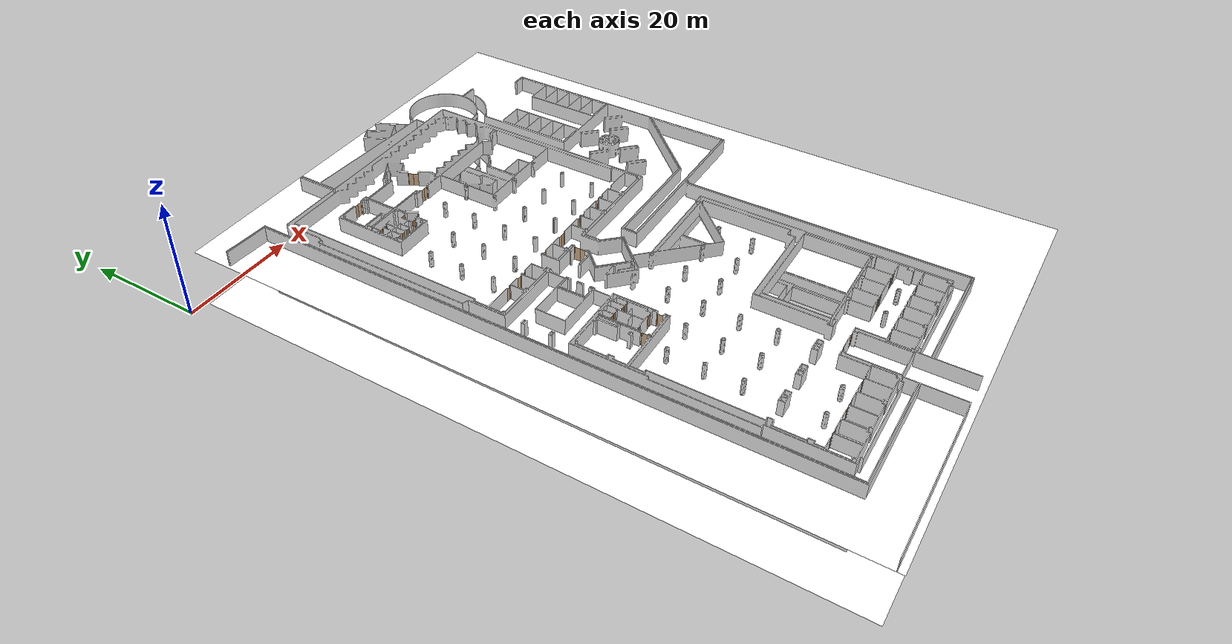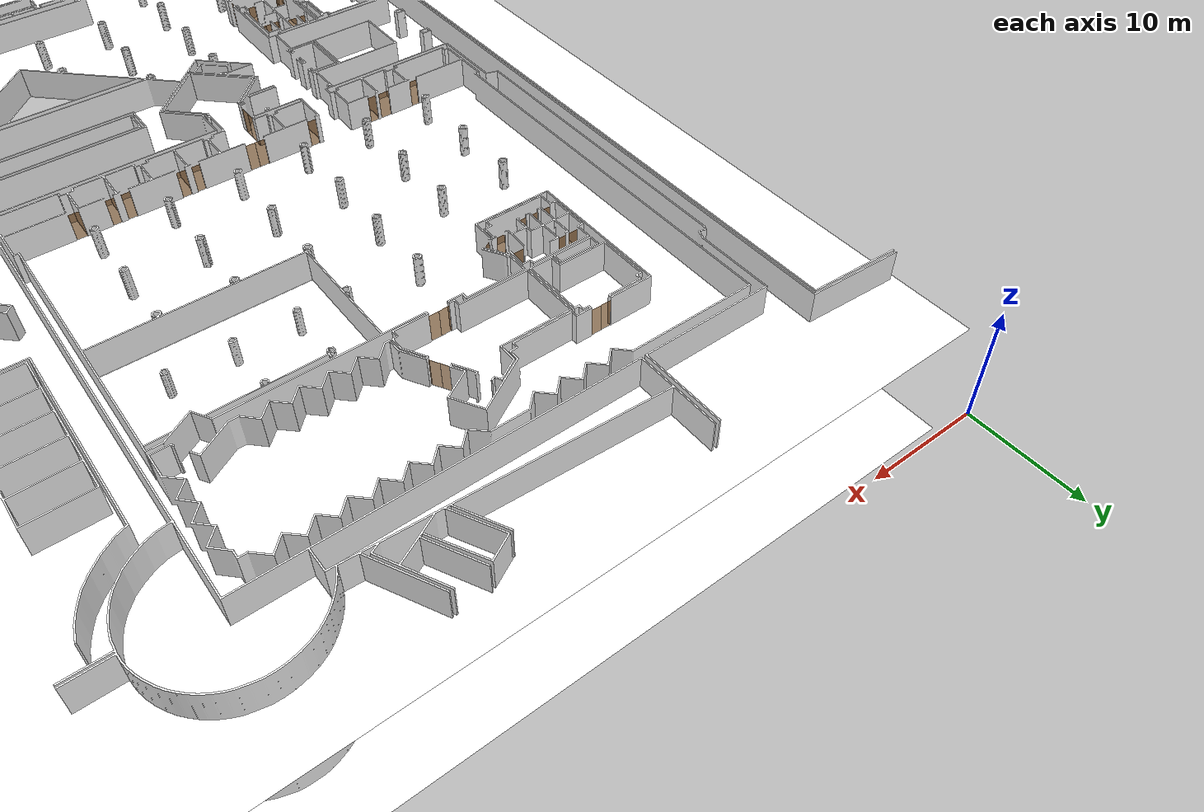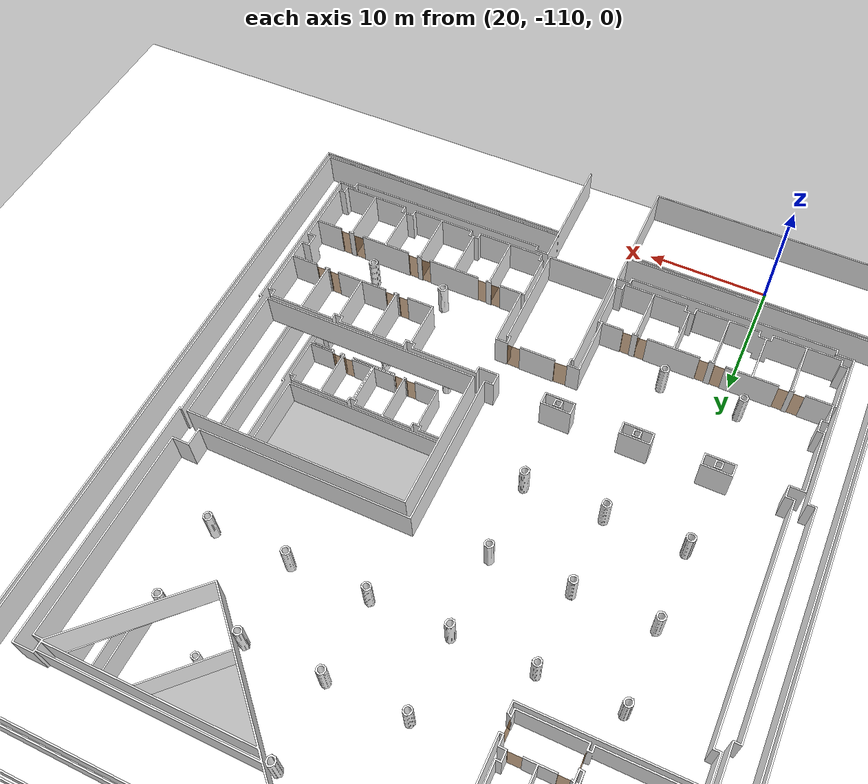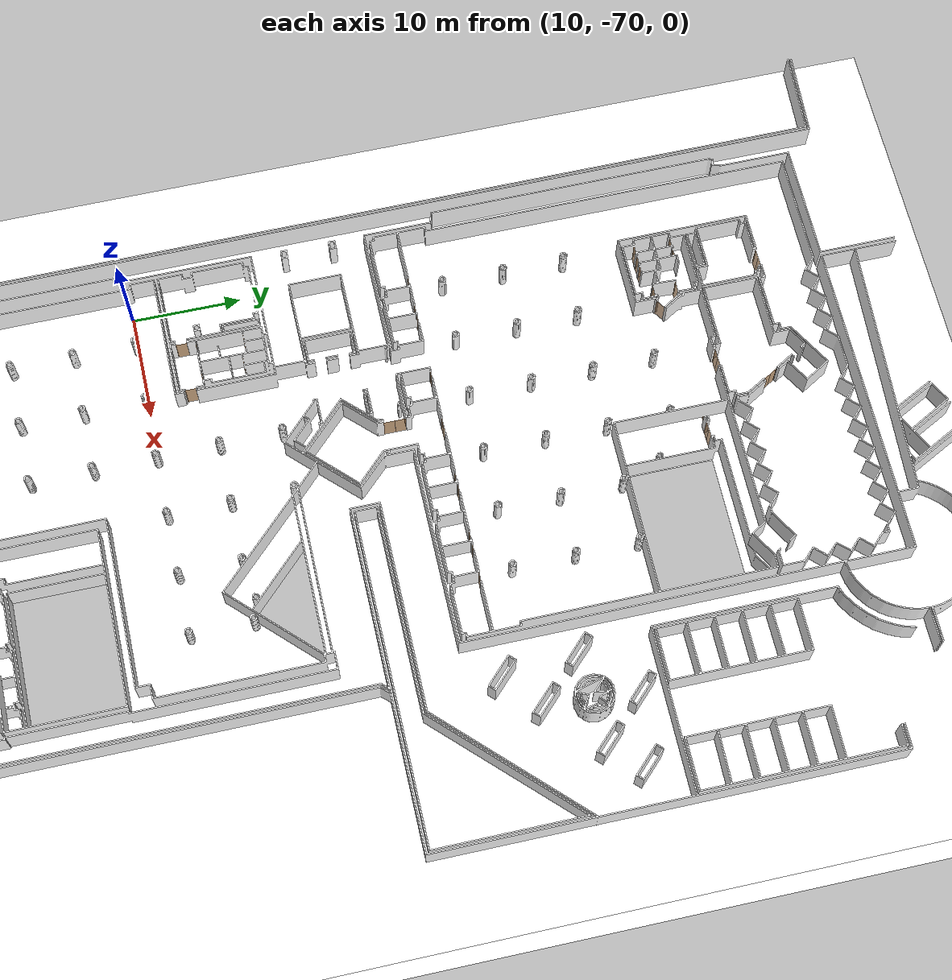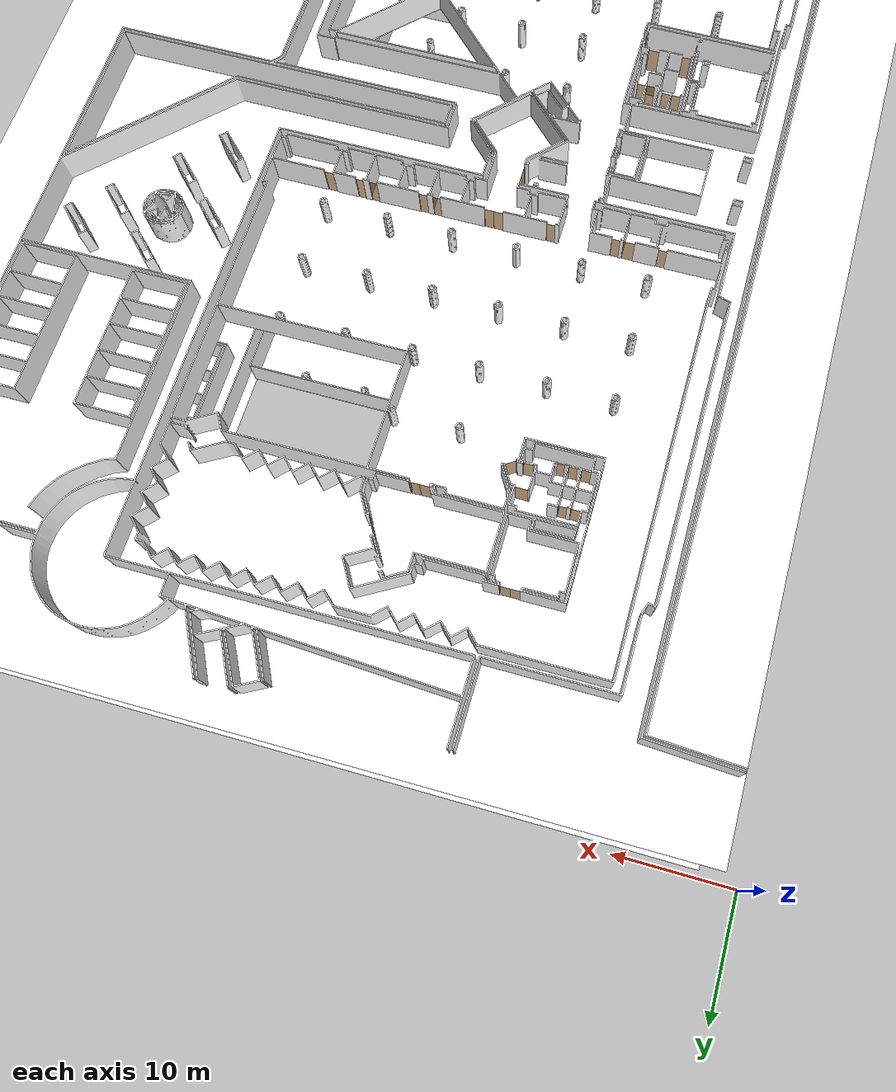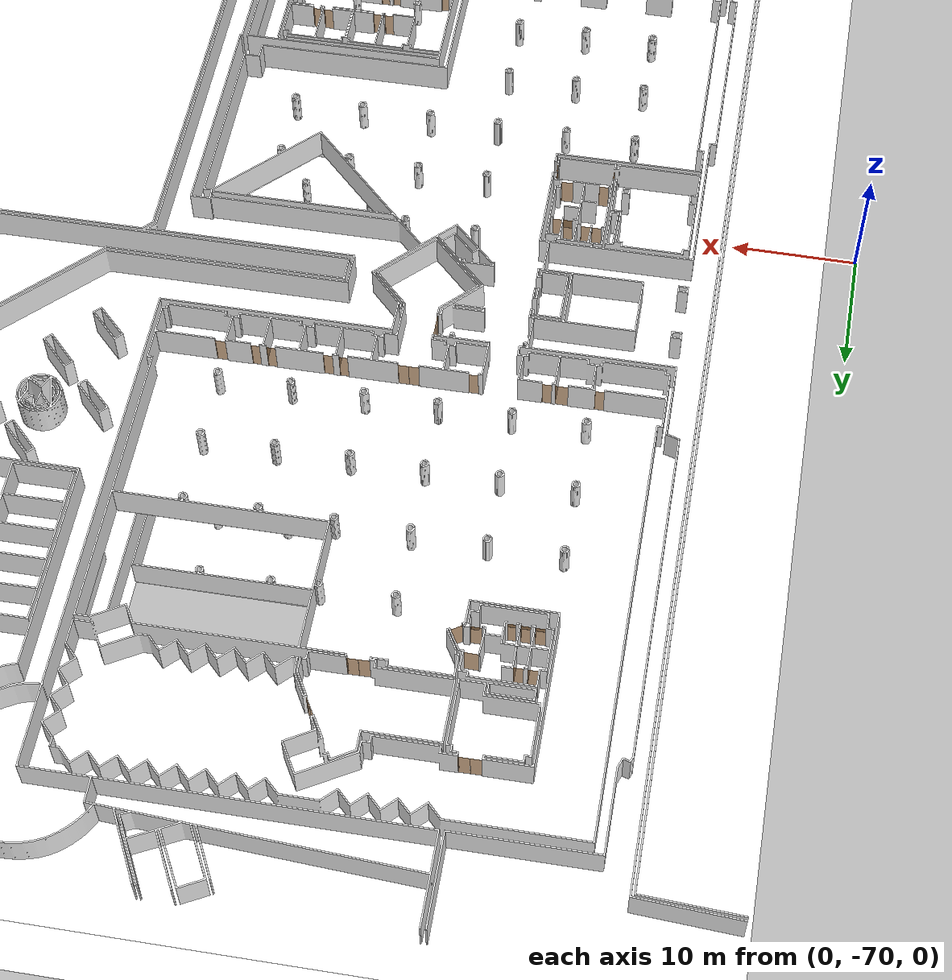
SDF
<sdf version="1.7">
 <world name="sim_world">
  <physics name="10ms" type="ode">
   <max_step_size>0.01</max_step_size>
   <real_time_factor>1.0</real_time_factor>
  </physics>
  <plugin filename="libgz-sim-physics-system.so" name="gz::sim::systems::Physics"/>
  <plugin filename="libgz-sim-user-commands-system.so" name="gz::sim::systems::UserCommands"/>
  <plugin filename="libgz-sim-scene-broadcaster-system.so" name="gz::sim::systems::SceneBroadcaster"/>
  <plugin filename="libdoor.so" name="door"/>
  <plugin filename="liblift.so" name="lift"/>
  <scene><ambient>1 1 1</ambient><background>0.8 0.8 0.8</background><grid>false</grid></scene>
  <light type="directional" name="sun">
   <pose>0 0 10 0 0 0</pose>
   <diffuse>1 1 1 1</diffuse>
   <specular>0.2 0.2 0.2 1</specular>
   <attenuation>
    <range>1000</range>
    <constant>0.09</constant>
    <linear>0.001</linear>
    <quadratic>0.001</quadratic>
   </attenuation>
   <direction>-0.5 0.1 -0.9</direction>
  </light>
  <model name="part1_1">
   <pose>23.474426678062983 -13.057676065197946 0.0 0 0 1.5575382472829962</pose>
   <link name="right">
    <pose>0.4093948700962029 0 1.11 0 0 0</pose>
    <visual name="right_visual">
     <geometry><box><size>0.8087897401924058 0.03 2.2</size></box></geometry>
     <material>
      <ambient>0.5 0.25 0 0.6</ambient>
      <diffuse>0.5 0.25 0 0.6</diffuse>
      <pbr><metal><metalness>0.0</metalness></metal></pbr>
     </material>
    </visual>
    <collision name="right_collision">
     <geometry><box><size>0.8087897401924058 0.03 2.2</size></box></geometry>
     <surface><contact><collide_bitmask>0x02</collide_bitmask></contact></surface>
    </collision>
    <inertial>
     <mass>50.0</mass>
     <inertia><ixx>20.17041666666667</ixx><iyy>22.892253516002086</iyy><izz>2.729336849335414</izz></inertia>
    </inertial>
   </link>
   <joint name="right_joint" type="revolute">
    <parent>world</parent>
    <child>right</child>
    <axis><xyz>0 0 1</xyz><limit><lower>0</lower><upper>1.57</upper></limit></axis>
    <pose>0.4093948700962029 0 0 0 0 0</pose>
   </joint>
   <link name="left">
    <pose>-0.4093948700962029 0 1.11 0 0 0</pose>
    <visual name="left_visual">
     <geometry><box><size>0.8087897401924058 0.03 2.2</size></box></geometry>
     <material>
      <ambient>0.5 0.25 0 0.6</ambient>
      <diffuse>0.5 0.25 0 0.6</diffuse>
      <pbr><metal><metalness>0.0</metalness></metal></pbr>
     </material>
    </visual>
    <collision name="left_collision">
     <geometry><box><size>0.8087897401924058 0.03 2.2</size></box></geometry>
     <surface><contact><collide_bitmask>0x02</collide_bitmask></contact></surface>
    </collision>
    <inertial>
     <mass>50.0</mass>
     <inertia><ixx>20.17041666666667</ixx><iyy>22.892253516002086</iyy><izz>2.729336849335414</izz></inertia>
    </inertial>
   </link>
   <joint name="left_joint" type="revolute">
    <parent>world</parent>
    <child>left</child>
    <axis><xyz>0 0 1</xyz><limit><lower>-1.57</lower><upper>0</upper></limit></axis>
    <pose>-0.4093948700962029 0 0 0 0 0</pose>
   </joint>
   <plugin name="register_component" filename="libregister_component.so">
    <component name="Door">
     <v_max_door>0.5</v_max_door>
     <a_max_door>0.3</a_max_door>
     <a_nom_door>0.15</a_nom_door>
     <dx_min_door>0.01</dx_min_door>
     <f_max_door>500.0</f_max_door>
     <ros_interface>true</ros_interface>
     <door name="part1_1" type="DoubleSwingDoor" left_joint_name="left_joint" right_joint_name="right_joint"/>
    </component>
   </plugin>
  </model>
  <model name="part1_5">
   <pose>30.62381580076393 -10.732564106341501 0.0 0 0 3.1325331828849774</pose>
   <link name="right">
    <pose>0.4033982302911093 0 1.11 0 0 0</pose>
    <visual name="right_visual">
     <geometry><box><size>0.7967964605822186 0.03 2.2</size></box></geometry>
     <material>
      <ambient>0.5 0.25 0 0.6</ambient>
      <diffuse>0.5 0.25 0 0.6</diffuse>
      <pbr><metal><metalness>0.0</metalness></metal></pbr>
     </material>
    </visual>
    <collision name="right_collision">
     <geometry><box><size>0.7967964605822186 0.03 2.2</size></box></geometry>
     <surface><contact><collide_bitmask>0x02</collide_bitmask></contact></surface>
    </collision>
    <inertial>
     <mass>50.0</mass>
     <inertia><ixx>20.17041666666667</ixx><iyy>22.8120191649848</iyy><izz>2.64910249831813</izz></inertia>
    </inertial>
   </link>
   <joint name="right_joint" type="revolute">
    <parent>world</parent>
    <child>right</child>
    <axis><xyz>0 0 1</xyz><limit><lower>0</lower><upper>1.57</upper></limit></axis>
    <pose>0.4033982302911093 0 0 0 0 0</pose>
   </joint>
   <link name="left">
    <pose>-0.4033982302911093 0 1.11 0 0 0</pose>
    <visual name="left_visual">
     <geometry><box><size>0.7967964605822186 0.03 2.2</size></box></geometry>
     <material>
      <ambient>0.5 0.25 0 0.6</ambient>
      <diffuse>0.5 0.25 0 0.6</diffuse>
      <pbr><metal><metalness>0.0</metalness></metal></pbr>
     </material>
    </visual>
    <collision name="left_collision">
     <geometry><box><size>0.7967964605822186 0.03 2.2</size></box></geometry>
     <surface><contact><collide_bitmask>0x02</collide_bitmask></contact></surface>
    </collision>
    <inertial>
     <mass>50.0</mass>
     <inertia><ixx>20.17041666666667</ixx><iyy>22.8120191649848</iyy><izz>2.64910249831813</izz></inertia>
    </inertial>
   </link>
   <joint name="left_joint" type="revolute">
    <parent>world</parent>
    <child>left</child>
    <axis><xyz>0 0 1</xyz><limit><lower>-1.57</lower><upper>0</upper></limit></axis>
    <pose>-0.4033982302911093 0 0 0 0 0</pose>
   </joint>
   <plugin name="register_component" filename="libregister_component.so">
    <component name="Door">
     <v_max_door>0.5</v_max_door>
     <a_max_door>0.3</a_max_door>
     <a_nom_door>0.15</a_nom_door>
     <dx_min_door>0.01</dx_min_door>
     <f_max_door>500.0</f_max_door>
     <ros_interface>true</ros_interface>
     <door name="part1_5" type="DoubleSwingDoor" left_joint_name="left_joint" right_joint_name="right_joint"/>
    </component>
   </plugin>
  </model>
  <model name="part1_6">
   <pose>33.303837845168346 -10.745754091436014 0.0 0 0 3.134548012368475</pose>
   <link name="right">
    <pose>0.4174083984026789 0 1.11 0 0 0</pose>
    <visual name="right_visual">
     <geometry><box><size>0.8248167968053578 0.03 2.2</size></box></geometry>
     <material>
      <ambient>0.5 0.25 0 0.6</ambient>
      <diffuse>0.5 0.25 0 0.6</diffuse>
      <pbr><metal><metalness>0.0</metalness></metal></pbr>
     </material>
    </visual>
    <collision name="right_collision">
     <geometry><box><size>0.8248167968053578 0.03 2.2</size></box></geometry>
     <surface><contact><collide_bitmask>0x02</collide_bitmask></contact></surface>
    </collision>
    <inertial>
     <mass>50.0</mass>
     <inertia><ixx>20.17041666666667</ixx><iyy>23.001344784551048</iyy><izz>2.838428117884379</izz></inertia>
    </inertial>
   </link>
   <joint name="right_joint" type="revolute">
    <parent>world</parent>
    <child>right</child>
    <axis><xyz>0 0 1</xyz><limit><lower>0</lower><upper>1.57</upper></limit></axis>
    <pose>0.4174083984026789 0 0 0 0 0</pose>
   </joint>
   <link name="left">
    <pose>-0.4174083984026789 0 1.11 0 0 0</pose>
    <visual name="left_visual">
     <geometry><box><size>0.8248167968053578 0.03 2.2</size></box></geometry>
     <material>
      <ambient>0.5 0.25 0 0.6</ambient>
      <diffuse>0.5 0.25 0 0.6</diffuse>
      <pbr><metal><metalness>0.0</metalness></metal></pbr>
     </material>
    </visual>
    <collision name="left_collision">
     <geometry><box><size>0.8248167968053578 0.03 2.2</size></box></geometry>
     <surface><contact><collide_bitmask>0x02</collide_bitmask></contact></surface>
    </collision>
    <inertial>
     <mass>50.0</mass>
     <inertia><ixx>20.17041666666667</ixx><iyy>23.001344784551048</iyy><izz>2.838428117884379</izz></inertia>
    </inertial>
   </link>
   <joint name="left_joint" type="revolute">
    <parent>world</parent>
    <child>left</child>
    <axis><xyz>0 0 1</xyz><limit><lower>-1.57</lower><upper>0</upper></limit></axis>
    <pose>-0.4174083984026789 0 0 0 0 0</pose>
   </joint>
   <plugin name="register_component" filename="libregister_component.so">
    <component name="Door">
     <v_max_door>0.5</v_max_door>
     <a_max_door>0.3</a_max_door>
     <a_nom_door>0.15</a_nom_door>
     <dx_min_door>0.01</dx_min_door>
     <f_max_door>500.0</f_max_door>
     <ros_interface>true</ros_interface>
     <door name="part1_6" type="DoubleSwingDoor" left_joint_name="left_joint" right_joint_name="right_joint"/>
    </component>
   </plugin>
  </model>
  <model name="part1_7">
   <pose>35.98657169916032 -10.742288109951325 0.0 0 0 -3.1297649534100933</pose>
   <link name="right">
    <pose>0.3951374930538005 0 1.11 0 0 0</pose>
    <visual name="right_visual">
     <geometry><box><size>0.780274986107601 0.03 2.2</size></box></geometry>
     <material>
      <ambient>0.5 0.25 0 0.6</ambient>
      <diffuse>0.5 0.25 0 0.6</diffuse>
      <pbr><metal><metalness>0.0</metalness></metal></pbr>
     </material>
    </visual>
    <collision name="right_collision">
     <geometry><box><size>0.780274986107601 0.03 2.2</size></box></geometry>
     <surface><contact><collide_bitmask>0x02</collide_bitmask></contact></surface>
    </collision>
    <inertial>
     <mass>50.0</mass>
     <inertia><ixx>20.17041666666667</ixx><iyy>22.70345439143841</iyy><izz>2.540537724771738</izz></inertia>
    </inertial>
   </link>
   <joint name="right_joint" type="revolute">
    <parent>world</parent>
    <child>right</child>
    <axis><xyz>0 0 1</xyz><limit><lower>0</lower><upper>1.57</upper></limit></axis>
    <pose>0.3951374930538005 0 0 0 0 0</pose>
   </joint>
   <link name="left">
    <pose>-0.3951374930538005 0 1.11 0 0 0</pose>
    <visual name="left_visual">
     <geometry><box><size>0.780274986107601 0.03 2.2</size></box></geometry>
     <material>
      <ambient>0.5 0.25 0 0.6</ambient>
      <diffuse>0.5 0.25 0 0.6</diffuse>
      <pbr><metal><metalness>0.0</metalness></metal></pbr>
     </material>
    </visual>
    <collision name="left_collision">
     <geometry><box><size>0.780274986107601 0.03 2.2</size></box></geometry>
     <surface><contact><collide_bitmask>0x02</collide_bitmask></contact></surface>
    </collision>
    <inertial>
     <mass>50.0</mass>
     <inertia><ixx>20.17041666666667</ixx><iyy>22.70345439143841</iyy><izz>2.540537724771738</izz></inertia>
    </inertial>
   </link>
   <joint name="left_joint" type="revolute">
    <parent>world</parent>
    <child>left</child>
    <axis><xyz>0 0 1</xyz><limit><lower>-1.57</lower><upper>0</upper></limit></axis>
    <pose>-0.3951374930538005 0 0 0 0 0</pose>
   </joint>
   <plugin name="register_component" filename="libregister_component.so">
    <component name="Door">
     <v_max_door>0.5</v_max_door>
     <a_max_door>0.3</a_max_door>
     <a_nom_door>0.15</a_nom_door>
     <dx_min_door>0.01</dx_min_door>
     <f_max_door>500.0</f_max_door>
     <ros_interface>true</ros_interface>
     <door name="part1_7" type="DoubleSwingDoor" left_joint_name="left_joint" right_joint_name="right_joint"/>
    </component>
   </plugin>
  </model>
  <model name="part1_8">
   <pose>38.57675903364792 -10.742207878898437 0.0 0 0 3.1300311442483824</pose>
   <link name="right">
    <pose>0.40076484747594776 0 1.11 0 0 0</pose>
    <visual name="right_visual">
     <geometry><box><size>0.7915296949518955 0.03 2.2</size></box></geometry>
     <material>
      <ambient>0.5 0.25 0 0.6</ambient>
      <diffuse>0.5 0.25 0 0.6</diffuse>
      <pbr><metal><metalness>0.0</metalness></metal></pbr>
     </material>
    </visual>
    <collision name="right_collision">
     <geometry><box><size>0.7915296949518955 0.03 2.2</size></box></geometry>
     <surface><contact><collide_bitmask>0x02</collide_bitmask></contact></surface>
    </collision>
    <inertial>
     <mass>50.0</mass>
     <inertia><ixx>20.17041666666667</ixx><iyy>22.777163574961005</iyy><izz>2.6142469082943367</izz></inertia>
    </inertial>
   </link>
   <joint name="right_joint" type="revolute">
    <parent>world</parent>
    <child>right</child>
    <axis><xyz>0 0 1</xyz><limit><lower>0</lower><upper>1.57</upper></limit></axis>
    <pose>0.40076484747594776 0 0 0 0 0</pose>
   </joint>
   <link name="left">
    <pose>-0.40076484747594776 0 1.11 0 0 0</pose>
    <visual name="left_visual">
     <geometry><box><size>0.7915296949518955 0.03 2.2</size></box></geometry>
     <material>
      <ambient>0.5 0.25 0 0.6</ambient>
      <diffuse>0.5 0.25 0 0.6</diffuse>
      <pbr><metal><metalness>0.0</metalness></metal></pbr>
     </material>
    </visual>
    <collision name="left_collision">
     <geometry><box><size>0.7915296949518955 0.03 2.2</size></box></geometry>
     <surface><contact><collide_bitmask>0x02</collide_bitmask></contact></surface>
    </collision>
    <inertial>
     <mass>50.0</mass>
     <inertia><ixx>20.17041666666667</ixx><iyy>22.777163574961005</iyy><izz>2.6142469082943367</izz></inertia>
    </inertial>
   </link>
   <joint name="left_joint" type="revolute">
    <parent>world</parent>
    <child>left</child>
    <axis><xyz>0 0 1</xyz><limit><lower>-1.57</lower><upper>0</upper></limit></axis>
    <pose>-0.40076484747594776 0 0 0 0 0</pose>
   </joint>
   <plugin name="register_component" filename="libregister_component.so">
    <component name="Door">
     <v_max_door>0.5</v_max_door>
     <a_max_door>0.3</a_max_door>
     <a_nom_door>0.15</a_nom_door>
     <dx_min_door>0.01</dx_min_door>
     <f_max_door>500.0</f_max_door>
     <ros_interface>true</ros_interface>
     <door name="part1_8" type="DoubleSwingDoor" left_joint_name="left_joint" right_joint_name="right_joint"/>
    </component>
   </plugin>
  </model>
  <model name="part1_4">
   <pose>30.361404096088606 -14.032708004714948 0.0 0 0 -2.62655505252304</pose>
   <link name="right">
    <pose>0.4545178244978947 0 1.11 0 0 0</pose>
    <visual name="right_visual">
     <geometry><box><size>0.8990356489957894 0.03 2.2</size></box></geometry>
     <material>
      <ambient>0.5 0.25 0 0.6</ambient>
      <diffuse>0.5 0.25 0 0.6</diffuse>
      <pbr><metal><metalness>0.0</metalness></metal></pbr>
     </material>
    </visual>
    <collision name="right_collision">
     <geometry><box><size>0.8990356489957894 0.03 2.2</size></box></geometry>
     <surface><contact><collide_bitmask>0x02</collide_bitmask></contact></surface>
    </collision>
    <inertial>
     <mass>50.0</mass>
     <inertia><ixx>20.17041666666667</ixx><iyy>23.534437909022003</iyy><izz>3.371521242355334</izz></inertia>
    </inertial>
   </link>
   <joint name="right_joint" type="revolute">
    <parent>world</parent>
    <child>right</child>
    <axis><xyz>0 0 1</xyz><limit><lower>0</lower><upper>1.57</upper></limit></axis>
    <pose>0.4545178244978947 0 0 0 0 0</pose>
   </joint>
   <link name="left">
    <pose>-0.4545178244978947 0 1.11 0 0 0</pose>
    <visual name="left_visual">
     <geometry><box><size>0.8990356489957894 0.03 2.2</size></box></geometry>
     <material>
      <ambient>0.5 0.25 0 0.6</ambient>
      <diffuse>0.5 0.25 0 0.6</diffuse>
      <pbr><metal><metalness>0.0</metalness></metal></pbr>
     </material>
    </visual>
    <collision name="left_collision">
     <geometry><box><size>0.8990356489957894 0.03 2.2</size></box></geometry>
     <surface><contact><collide_bitmask>0x02</collide_bitmask></contact></surface>
    </collision>
    <inertial>
     <mass>50.0</mass>
     <inertia><ixx>20.17041666666667</ixx><iyy>23.534437909022003</iyy><izz>3.371521242355334</izz></inertia>
    </inertial>
   </link>
   <joint name="left_joint" type="revolute">
    <parent>world</parent>
    <child>left</child>
    <axis><xyz>0 0 1</xyz><limit><lower>-1.57</lower><upper>0</upper></limit></axis>
    <pose>-0.4545178244978947 0 0 0 0 0</pose>
   </joint>
   <plugin name="register_component" filename="libregister_component.so">
    <component name="Door">
     <v_max_door>0.5</v_max_door>
     <a_max_door>0.3</a_max_door>
     <a_nom_door>0.15</a_nom_door>
     <dx_min_door>0.01</dx_min_door>
     <f_max_door>500.0</f_max_door>
     <ros_interface>true</ros_interface>
     <door name="part1_4" type="DoubleSwingDoor" left_joint_name="left_joint" right_joint_name="right_joint"/>
    </component>
   </plugin>
  </model>
  <model name="part1_9">
   <pose>30.839613263712295 -21.2473811351495 0.0 0 0 -3.1402743417935888</pose>
   <link name="right">
    <pose>0.4016690922096701 0 1.11 0 0 0</pose>
    <visual name="right_visual">
     <geometry><box><size>0.7933381844193402 0.03 2.2</size></box></geometry>
     <material>
      <ambient>0.5 0.25 0 0.6</ambient>
      <diffuse>0.5 0.25 0 0.6</diffuse>
      <pbr><metal><metalness>0.0</metalness></metal></pbr>
     </material>
    </visual>
    <collision name="right_collision">
     <geometry><box><size>0.7933381844193402 0.03 2.2</size></box></geometry>
     <surface><contact><collide_bitmask>0x02</collide_bitmask></contact></surface>
    </collision>
    <inertial>
     <mass>50.0</mass>
     <inertia><ixx>20.17041666666667</ixx><iyy>22.789106145240737</iyy><izz>2.626189478574063</izz></inertia>
    </inertial>
   </link>
   <joint name="right_joint" type="revolute">
    <parent>world</parent>
    <child>right</child>
    <axis><xyz>0 0 1</xyz><limit><lower>0</lower><upper>1.57</upper></limit></axis>
    <pose>0.4016690922096701 0 0 0 0 0</pose>
   </joint>
   <link name="left">
    <pose>-0.4016690922096701 0 1.11 0 0 0</pose>
    <visual name="left_visual">
     <geometry><box><size>0.7933381844193402 0.03 2.2</size></box></geometry>
     <material>
      <ambient>0.5 0.25 0 0.6</ambient>
      <diffuse>0.5 0.25 0 0.6</diffuse>
      <pbr><metal><metalness>0.0</metalness></metal></pbr>
     </material>
    </visual>
    <collision name="left_collision">
     <geometry><box><size>0.7933381844193402 0.03 2.2</size></box></geometry>
     <surface><contact><collide_bitmask>0x02</collide_bitmask></contact></surface>
    </collision>
    <inertial>
     <mass>50.0</mass>
     <inertia><ixx>20.17041666666667</ixx><iyy>22.789106145240737</iyy><izz>2.626189478574063</izz></inertia>
    </inertial>
   </link>
   <joint name="left_joint" type="revolute">
    <parent>world</parent>
    <child>left</child>
    <axis><xyz>0 0 1</xyz><limit><lower>-1.57</lower><upper>0</upper></limit></axis>
    <pose>-0.4016690922096701 0 0 0 0 0</pose>
   </joint>
   <plugin name="register_component" filename="libregister_component.so">
    <component name="Door">
     <v_max_door>0.5</v_max_door>
     <a_max_door>0.3</a_max_door>
     <a_nom_door>0.15</a_nom_door>
     <dx_min_door>0.01</dx_min_door>
     <f_max_door>500.0</f_max_door>
     <ros_interface>true</ros_interface>
     <door name="part1_9" type="DoubleSwingDoor" left_joint_name="left_joint" right_joint_name="right_joint"/>
    </component>
   </plugin>
  </model>
  <model name="part1_10_end">
   <pose>33.01170053539864 -21.444909987355643 0.0 0 0 -3.1235009749570586</pose>
   <link name="right">
    <pose>0.38805686569392206 0 1.11 0 0 0</pose>
    <visual name="right_visual">
     <geometry><box><size>0.7661137313878441 0.03 2.2</size></box></geometry>
     <material>
      <ambient>0.5 0.25 0 0.6</ambient>
      <diffuse>0.5 0.25 0 0.6</diffuse>
      <pbr><metal><metalness>0.0</metalness></metal></pbr>
     </material>
    </visual>
    <collision name="right_collision">
     <geometry><box><size>0.7661137313878441 0.03 2.2</size></box></geometry>
     <surface><contact><collide_bitmask>0x02</collide_bitmask></contact></surface>
    </collision>
    <inertial>
     <mass>50.0</mass>
     <inertia><ixx>20.17041666666667</ixx><iyy>22.612209372587532</iyy><izz>2.4492927059208576</izz></inertia>
    </inertial>
   </link>
   <joint name="right_joint" type="revolute">
    <parent>world</parent>
    <child>right</child>
    <axis><xyz>0 0 -1</xyz><limit><lower>0</lower><upper>1.57</upper></limit></axis>
    <pose>0.38805686569392206 0 0 0 0 0</pose>
   </joint>
   <link name="left">
    <pose>-0.38805686569392206 0 1.11 0 0 0</pose>
    <visual name="left_visual">
     <geometry><box><size>0.7661137313878441 0.03 2.2</size></box></geometry>
     <material>
      <ambient>0.5 0.25 0 0.6</ambient>
      <diffuse>0.5 0.25 0 0.6</diffuse>
      <pbr><metal><metalness>0.0</metalness></metal></pbr>
     </material>
    </visual>
    <collision name="left_collision">
     <geometry><box><size>0.7661137313878441 0.03 2.2</size></box></geometry>
     <surface><contact><collide_bitmask>0x02</collide_bitmask></contact></surface>
    </collision>
    <inertial>
     <mass>50.0</mass>
     <inertia><ixx>20.17041666666667</ixx><iyy>22.612209372587532</iyy><izz>2.4492927059208576</izz></inertia>
    </inertial>
   </link>
   <joint name="left_joint" type="revolute">
    <parent>world</parent>
    <child>left</child>
    <axis><xyz>0 0 -1</xyz><limit><lower>-1.57</lower><upper>0</upper></limit></axis>
    <pose>-0.38805686569392206 0 0 0 0 0</pose>
   </joint>
   <plugin name="register_component" filename="libregister_component.so">
    <component name="Door">
     <v_max_door>0.5</v_max_door>
     <a_max_door>0.3</a_max_door>
     <a_nom_door>0.15</a_nom_door>
     <dx_min_door>0.01</dx_min_door>
     <f_max_door>500.0</f_max_door>
     <ros_interface>true</ros_interface>
     <door name="part1_10_end" type="DoubleSwingDoor" left_joint_name="left_joint" right_joint_name="right_joint"/>
    </component>
   </plugin>
  </model>
  <model name="part1_2">
   <pose>22.344348228843145 -15.362987000202047 0.0 0 0 3.138955944615511</pose>
   <link name="right">
    <pose>0.4275206745211724 0 1.11 0 0 0</pose>
    <visual name="right_visual">
     <geometry><box><size>0.8450413490423447 0.03 2.2</size></box></geometry>
     <material>
      <ambient>0.5 0.25 0 0.6</ambient>
      <diffuse>0.5 0.25 0 0.6</diffuse>
      <pbr><metal><metalness>0.0</metalness></metal></pbr>
     </material>
    </visual>
    <collision name="right_collision">
     <geometry><box><size>0.8450413490423447 0.03 2.2</size></box></geometry>
     <surface><contact><collide_bitmask>0x02</collide_bitmask></contact></surface>
    </collision>
    <inertial>
     <mass>50.0</mass>
     <inertia><ixx>20.17041666666667</ixx><iyy>23.142062006630447</iyy><izz>2.979145339963775</izz></inertia>
    </inertial>
   </link>
   <joint name="right_joint" type="revolute">
    <parent>world</parent>
    <child>right</child>
    <axis><xyz>0 0 1</xyz><limit><lower>0</lower><upper>1.57</upper></limit></axis>
    <pose>0.4275206745211724 0 0 0 0 0</pose>
   </joint>
   <link name="left">
    <pose>-0.4275206745211724 0 1.11 0 0 0</pose>
    <visual name="left_visual">
     <geometry><box><size>0.8450413490423447 0.03 2.2</size></box></geometry>
     <material>
      <ambient>0.5 0.25 0 0.6</ambient>
      <diffuse>0.5 0.25 0 0.6</diffuse>
      <pbr><metal><metalness>0.0</metalness></metal></pbr>
     </material>
    </visual>
    <collision name="left_collision">
     <geometry><box><size>0.8450413490423447 0.03 2.2</size></box></geometry>
     <surface><contact><collide_bitmask>0x02</collide_bitmask></contact></surface>
    </collision>
    <inertial>
     <mass>50.0</mass>
     <inertia><ixx>20.17041666666667</ixx><iyy>23.142062006630447</iyy><izz>2.979145339963775</izz></inertia>
    </inertial>
   </link>
   <joint name="left_joint" type="revolute">
    <parent>world</parent>
    <child>left</child>
    <axis><xyz>0 0 1</xyz><limit><lower>-1.57</lower><upper>0</upper></limit></axis>
    <pose>-0.4275206745211724 0 0 0 0 0</pose>
   </joint>
   <plugin name="register_component" filename="libregister_component.so">
    <component name="Door">
     <v_max_door>0.5</v_max_door>
     <a_max_door>0.3</a_max_door>
     <a_nom_door>0.15</a_nom_door>
     <dx_min_door>0.01</dx_min_door>
     <f_max_door>500.0</f_max_door>
     <ros_interface>true</ros_interface>
     <door name="part1_2" type="DoubleSwingDoor" left_joint_name="left_joint" right_joint_name="right_joint"/>
    </component>
   </plugin>
  </model>
  <model name="part1_3">
   <pose>15.253664167539132 -15.64746224442111 0.0 0 0 3.1277439827895375</pose>
   <link name="right">
    <pose>0.4009169117466249 0 1.11 0 0 0</pose>
    <visual name="right_visual">
     <geometry><box><size>0.7918338234932498 0.03 2.2</size></box></geometry>
     <material>
      <ambient>0.5 0.25 0 0.6</ambient>
      <diffuse>0.5 0.25 0 0.6</diffuse>
      <pbr><metal><metalness>0.0</metalness></metal></pbr>
     </material>
    </visual>
    <collision name="right_collision">
     <geometry><box><size>0.7918338234932498 0.03 2.2</size></box></geometry>
     <surface><contact><collide_bitmask>0x02</collide_bitmask></contact></surface>
    </collision>
    <inertial>
     <mass>50.0</mass>
     <inertia><ixx>20.17041666666667</ixx><iyy>22.779170016783084</iyy><izz>2.616253350116413</izz></inertia>
    </inertial>
   </link>
   <joint name="right_joint" type="revolute">
    <parent>world</parent>
    <child>right</child>
    <axis><xyz>0 0 -1</xyz><limit><lower>0</lower><upper>1.57</upper></limit></axis>
    <pose>0.4009169117466249 0 0 0 0 0</pose>
   </joint>
   <link name="left">
    <pose>-0.4009169117466249 0 1.11 0 0 0</pose>
    <visual name="left_visual">
     <geometry><box><size>0.7918338234932498 0.03 2.2</size></box></geometry>
     <material>
      <ambient>0.5 0.25 0 0.6</ambient>
      <diffuse>0.5 0.25 0 0.6</diffuse>
      <pbr><metal><metalness>0.0</metalness></metal></pbr>
     </material>
    </visual>
    <collision name="left_collision">
     <geometry><box><size>0.7918338234932498 0.03 2.2</size></box></geometry>
     <surface><contact><collide_bitmask>0x02</collide_bitmask></contact></surface>
    </collision>
    <inertial>
     <mass>50.0</mass>
     <inertia><ixx>20.17041666666667</ixx><iyy>22.779170016783084</iyy><izz>2.616253350116413</izz></inertia>
    </inertial>
   </link>
   <joint name="left_joint" type="revolute">
    <parent>world</parent>
    <child>left</child>
    <axis><xyz>0 0 -1</xyz><limit><lower>-1.57</lower><upper>0</upper></limit></axis>
    <pose>-0.4009169117466249 0 0 0 0 0</pose>
   </joint>
   <plugin name="register_component" filename="libregister_component.so">
    <component name="Door">
     <v_max_door>0.5</v_max_door>
     <a_max_door>0.3</a_max_door>
     <a_nom_door>0.15</a_nom_door>
     <dx_min_door>0.01</dx_min_door>
     <f_max_door>500.0</f_max_door>
     <ros_interface>true</ros_interface>
     <door name="part1_3" type="DoubleSwingDoor" left_joint_name="left_joint" right_joint_name="right_joint"/>
    </component>
   </plugin>
  </model>
  <model name="part2_1">
   <pose>20.413066439289835 -21.727644217727075 0.0 0 0 1.5586480130347593</pose>
   <link name="right">
    <pose>0 0 1.11 0 0 0</pose>
    <visual name="right_visual">
     <geometry><box><size>0.9555717398338419 0.03 2.2</size></box></geometry>
     <material>
      <ambient>0.5 0.25 0 0.6</ambient>
      <diffuse>0.5 0.25 0 0.6</diffuse>
      <pbr><metal><metalness>0.0</metalness></metal></pbr>
     </material>
    </visual>
    <collision name="right_collision">
     <geometry><box><size>0.9555717398338419 0.03 2.2</size></box></geometry>
     <surface><contact><collide_bitmask>0x02</collide_bitmask></contact></surface>
    </collision>
    <inertial>
     <mass>50.0</mass>
     <inertia><ixx>20.17041666666667</ixx><iyy>23.97132229153782</iyy><izz>3.808405624871149</izz></inertia>
    </inertial>
   </link>
   <joint name="right_joint" type="revolute">
    <parent>world</parent>
    <child>right</child>
    <axis><xyz>0 0 -1</xyz><limit><lower>0</lower><upper>1.57</upper></limit></axis>
    <pose>0.48278586991692096 0 0 0 0 0</pose>
   </joint>
   <plugin name="register_component" filename="libregister_component.so">
    <component name="Door">
     <v_max_door>0.5</v_max_door>
     <a_max_door>0.3</a_max_door>
     <a_nom_door>0.15</a_nom_door>
     <dx_min_door>0.01</dx_min_door>
     <f_max_door>500.0</f_max_door>
     <ros_interface>true</ros_interface>
     <door name="part2_1" type="SwingDoor" left_joint_name="empty_joint" right_joint_name="right_joint"/>
    </component>
   </plugin>
  </model>
  <model name="part2_4">
   <pose>20.922670017907944 -22.218112690231795 0.0 0 0 3.126620543687866</pose>
   <link name="right">
    <pose>0 0 1.11 0 0 0</pose>
    <visual name="right_visual">
     <geometry><box><size>1.0210524974741124 0.03 2.2</size></box></geometry>
     <material>
      <ambient>0.5 0.25 0 0.6</ambient>
      <diffuse>0.5 0.25 0 0.6</diffuse>
      <pbr><metal><metalness>0.0</metalness></metal></pbr>
     </material>
    </visual>
    <collision name="right_collision">
     <geometry><box><size>1.0210524974741124 0.03 2.2</size></box></geometry>
     <surface><contact><collide_bitmask>0x02</collide_bitmask></contact></surface>
    </collision>
    <inertial>
     <mass>50.0</mass>
     <inertia><ixx>20.17041666666667</ixx><iyy>24.510617510825515</iyy><izz>4.347700844158843</izz></inertia>
    </inertial>
   </link>
   <joint name="right_joint" type="revolute">
    <parent>world</parent>
    <child>right</child>
    <axis><xyz>0 0 1</xyz><limit><lower>0</lower><upper>1.57</upper></limit></axis>
    <pose>0.5155262487370562 0 0 0 0 0</pose>
   </joint>
   <plugin name="register_component" filename="libregister_component.so">
    <component name="Door">
     <v_max_door>0.5</v_max_door>
     <a_max_door>0.3</a_max_door>
     <a_nom_door>0.15</a_nom_door>
     <dx_min_door>0.01</dx_min_door>
     <f_max_door>500.0</f_max_door>
     <ros_interface>true</ros_interface>
     <door name="part2_4" type="SwingDoor" left_joint_name="empty_joint" right_joint_name="right_joint"/>
    </component>
   </plugin>
  </model>
  <model name="part2_3">
   <pose>20.919621237898262 -25.424450441570542 0.0 0 0 -3.1088230642559003</pose>
   <link name="right">
    <pose>0 0 1.11 0 0 0</pose>
    <visual name="right_visual">
     <geometry><box><size>1.0312199456807118 0.03 2.2</size></box></geometry>
     <material>
      <ambient>0.5 0.25 0 0.6</ambient>
      <diffuse>0.5 0.25 0 0.6</diffuse>
      <pbr><metal><metalness>0.0</metalness></metal></pbr>
     </material>
    </visual>
    <collision name="right_collision">
     <geometry><box><size>1.0312199456807118 0.03 2.2</size></box></geometry>
     <surface><contact><collide_bitmask>0x02</collide_bitmask></contact></surface>
    </collision>
    <inertial>
     <mass>50.0</mass>
     <inertia><ixx>20.17041666666667</ixx><iyy>24.59756073487388</iyy><izz>4.434644068207209</izz></inertia>
    </inertial>
   </link>
   <joint name="right_joint" type="revolute">
    <parent>world</parent>
    <child>right</child>
    <axis><xyz>0 0 -1</xyz><limit><lower>0</lower><upper>1.57</upper></limit></axis>
    <pose>0.5206099728403559 0 0 0 0 0</pose>
   </joint>
   <plugin name="register_component" filename="libregister_component.so">
    <component name="Door">
     <v_max_door>0.5</v_max_door>
     <a_max_door>0.3</a_max_door>
     <a_nom_door>0.15</a_nom_door>
     <dx_min_door>0.01</dx_min_door>
     <f_max_door>500.0</f_max_door>
     <ros_interface>true</ros_interface>
     <door name="part2_3" type="SwingDoor" left_joint_name="empty_joint" right_joint_name="right_joint"/>
    </component>
   </plugin>
  </model>
  <model name="part2_2">
   <pose>20.38263480093005 -25.917791185768593 0.0 0 0 1.535839882828038</pose>
   <link name="right">
    <pose>0 0 1.11 0 0 0</pose>
    <visual name="right_visual">
     <geometry><box><size>0.9431495373669919 0.03 2.2</size></box></geometry>
     <material>
      <ambient>0.5 0.25 0 0.6</ambient>
      <diffuse>0.5 0.25 0 0.6</diffuse>
      <pbr><metal><metalness>0.0</metalness></metal></pbr>
     </material>
    </visual>
    <collision name="right_collision">
     <geometry><box><size>0.9431495373669919 0.03 2.2</size></box></geometry>
     <surface><contact><collide_bitmask>0x02</collide_bitmask></contact></surface>
    </collision>
    <inertial>
     <mass>50.0</mass>
     <inertia><ixx>20.17041666666667</ixx><iyy>23.87304604098155</iyy><izz>3.710129374314879</izz></inertia>
    </inertial>
   </link>
   <joint name="right_joint" type="revolute">
    <parent>world</parent>
    <child>right</child>
    <axis><xyz>0 0 1</xyz><limit><lower>0</lower><upper>1.57</upper></limit></axis>
    <pose>0.47657476868349596 0 0 0 0 0</pose>
   </joint>
   <plugin name="register_component" filename="libregister_component.so">
    <component name="Door">
     <v_max_door>0.5</v_max_door>
     <a_max_door>0.3</a_max_door>
     <a_nom_door>0.15</a_nom_door>
     <dx_min_door>0.01</dx_min_door>
     <f_max_door>500.0</f_max_door>
     <ros_interface>true</ros_interface>
     <door name="part2_2" type="SwingDoor" left_joint_name="empty_joint" right_joint_name="right_joint"/>
    </component>
   </plugin>
  </model>
  <model name="part2_6">
   <pose>23.62189937637335 -24.873600078663575 0.0 0 0 3.137896065827331</pose>
   <link name="right">
    <pose>0 0 1.11 0 0 0</pose>
    <visual name="right_visual">
     <geometry><box><size>0.9276185826104854 0.03 2.2</size></box></geometry>
     <material>
      <ambient>0.5 0.25 0 0.6</ambient>
      <diffuse>0.5 0.25 0 0.6</diffuse>
      <pbr><metal><metalness>0.0</metalness></metal></pbr>
     </material>
    </visual>
    <collision name="right_collision">
     <geometry><box><size>0.9276185826104854 0.03 2.2</size></box></geometry>
     <surface><contact><collide_bitmask>0x02</collide_bitmask></contact></surface>
    </collision>
    <inertial>
     <mass>50.0</mass>
     <inertia><ixx>20.17041666666667</ixx><iyy>23.751984311684527</iyy><izz>3.589067645017858</izz></inertia>
    </inertial>
   </link>
   <joint name="right_joint" type="revolute">
    <parent>world</parent>
    <child>right</child>
    <axis><xyz>0 0 1</xyz><limit><lower>0</lower><upper>1.57</upper></limit></axis>
    <pose>0.4688092913052427 0 0 0 0 0</pose>
   </joint>
   <plugin name="register_component" filename="libregister_component.so">
    <component name="Door">
     <v_max_door>0.5</v_max_door>
     <a_max_door>0.3</a_max_door>
     <a_nom_door>0.15</a_nom_door>
     <dx_min_door>0.01</dx_min_door>
     <f_max_door>500.0</f_max_door>
     <ros_interface>true</ros_interface>
     <door name="part2_6" type="SwingDoor" left_joint_name="empty_joint" right_joint_name="right_joint"/>
    </component>
   </plugin>
  </model>
  <model name="part2_5">
   <pose>23.49012789511284 -22.916034596184698 0.0 0 0 0.03134180106866015</pose>
   <link name="right">
    <pose>0 0 1.11 0 0 0</pose>
    <visual name="right_visual">
     <geometry><box><size>1.0320391962318292 0.03 2.2</size></box></geometry>
     <material>
      <ambient>0.5 0.25 0 0.6</ambient>
      <diffuse>0.5 0.25 0 0.6</diffuse>
      <pbr><metal><metalness>0.0</metalness></metal></pbr>
     </material>
    </visual>
    <collision name="right_collision">
     <geometry><box><size>1.0320391962318292 0.03 2.2</size></box></geometry>
     <surface><contact><collide_bitmask>0x02</collide_bitmask></contact></surface>
    </collision>
    <inertial>
     <mass>50.0</mass>
     <inertia><ixx>20.17041666666667</ixx><iyy>24.60460376066184</iyy><izz>4.441687093995166</izz></inertia>
    </inertial>
   </link>
   <joint name="right_joint" type="revolute">
    <parent>world</parent>
    <child>right</child>
    <axis><xyz>0 0 -1</xyz><limit><lower>0</lower><upper>1.57</upper></limit></axis>
    <pose>0.5210195981159146 0 0 0 0 0</pose>
   </joint>
   <plugin name="register_component" filename="libregister_component.so">
    <component name="Door">
     <v_max_door>0.5</v_max_door>
     <a_max_door>0.3</a_max_door>
     <a_nom_door>0.15</a_nom_door>
     <dx_min_door>0.01</dx_min_door>
     <f_max_door>500.0</f_max_door>
     <ros_interface>true</ros_interface>
     <door name="part2_5" type="SwingDoor" left_joint_name="empty_joint" right_joint_name="right_joint"/>
    </component>
   </plugin>
  </model>
  <model name="part2_7_end">
   <pose>24.838442831288784 -24.697043623681914 0.0 0 0 -2.519063830197608</pose>
   <link name="right">
    <pose>0 0 1.11 0 0 0</pose>
    <visual name="right_visual">
     <geometry><box><size>0.9834981706830346 0.03 2.2</size></box></geometry>
     <material>
      <ambient>0.5 0.25 0 0.6</ambient>
      <diffuse>0.5 0.25 0 0.6</diffuse>
      <pbr><metal><metalness>0.0</metalness></metal></pbr>
     </material>
    </visual>
    <collision name="right_collision">
     <geometry><box><size>0.9834981706830346 0.03 2.2</size></box></geometry>
     <surface><contact><collide_bitmask>0x02</collide_bitmask></contact></surface>
    </collision>
    <inertial>
     <mass>50.0</mass>
     <inertia><ixx>20.17041666666667</ixx><iyy>24.19695271557032</iyy><izz>4.034036048903648</izz></inertia>
    </inertial>
   </link>
   <joint name="right_joint" type="revolute">
    <parent>world</parent>
    <child>right</child>
    <axis><xyz>0 0 -1</xyz><limit><lower>0</lower><upper>1.57</upper></limit></axis>
    <pose>0.4967490853415173 0 0 0 0 0</pose>
   </joint>
   <plugin name="register_component" filename="libregister_component.so">
    <component name="Door">
     <v_max_door>0.5</v_max_door>
     <a_max_door>0.3</a_max_door>
     <a_nom_door>0.15</a_nom_door>
     <dx_min_door>0.01</dx_min_door>
     <f_max_door>500.0</f_max_door>
     <ros_interface>true</ros_interface>
     <door name="part2_7_end" type="SwingDoor" left_joint_name="empty_joint" right_joint_name="right_joint"/>
    </component>
   </plugin>
  </model>
  <model name="part6_9_end">
   <pose>45.87496071324243 -45.209163320865215 0.0 0 0 -3.124644767900746</pose>
   <link name="right">
    <pose>0 0 1.11 0 0 0</pose>
    <visual name="right_visual">
     <geometry><box><size>0.7541019121911322 0.03 2.2</size></box></geometry>
     <material>
      <ambient>0.5 0.25 0 0.6</ambient>
      <diffuse>0.5 0.25 0 0.6</diffuse>
      <pbr><metal><metalness>0.0</metalness></metal></pbr>
     </material>
    </visual>
    <collision name="right_collision">
     <geometry><box><size>0.7541019121911322 0.03 2.2</size></box></geometry>
     <surface><contact><collide_bitmask>0x02</collide_bitmask></contact></surface>
    </collision>
    <inertial>
     <mass>50.0</mass>
     <inertia><ixx>20.17041666666667</ixx><iyy>22.536123724876347</iyy><izz>2.3732070582096756</izz></inertia>
    </inertial>
   </link>
   <joint name="right_joint" type="revolute">
    <parent>world</parent>
    <child>right</child>
    <axis><xyz>0 0 -1</xyz><limit><lower>0</lower><upper>1.57</upper></limit></axis>
    <pose>0.3820509560955661 0 0 0 0 0</pose>
   </joint>
   <plugin name="register_component" filename="libregister_component.so">
    <component name="Door">
     <v_max_door>0.5</v_max_door>
     <a_max_door>0.3</a_max_door>
     <a_nom_door>0.15</a_nom_door>
     <dx_min_door>0.01</dx_min_door>
     <f_max_door>500.0</f_max_door>
     <ros_interface>true</ros_interface>
     <door name="part6_9_end" type="SwingDoor" left_joint_name="empty_joint" right_joint_name="right_joint"/>
    </component>
   </plugin>
  </model>
  <model name="part6_8">
   <pose>43.22708725172956 -45.21547750472737 0.0 0 0 -3.1343271389946814</pose>
   <link name="right">
    <pose>0 0 1.11 0 0 0</pose>
    <visual name="right_visual">
     <geometry><box><size>0.7806658023973515 0.03 2.2</size></box></geometry>
     <material>
      <ambient>0.5 0.25 0 0.6</ambient>
      <diffuse>0.5 0.25 0 0.6</diffuse>
      <pbr><metal><metalness>0.0</metalness></metal></pbr>
     </material>
    </visual>
    <collision name="right_collision">
     <geometry><box><size>0.7806658023973515 0.03 2.2</size></box></geometry>
     <surface><contact><collide_bitmask>0x02</collide_bitmask></contact></surface>
    </collision>
    <inertial>
     <mass>50.0</mass>
     <inertia><ixx>20.17041666666667</ixx><iyy>22.705996229302926</iyy><izz>2.543079562636253</izz></inertia>
    </inertial>
   </link>
   <joint name="right_joint" type="revolute">
    <parent>world</parent>
    <child>right</child>
    <axis><xyz>0 0 -1</xyz><limit><lower>0</lower><upper>1.57</upper></limit></axis>
    <pose>0.39533290119867576 0 0 0 0 0</pose>
   </joint>
   <plugin name="register_component" filename="libregister_component.so">
    <component name="Door">
     <v_max_door>0.5</v_max_door>
     <a_max_door>0.3</a_max_door>
     <a_nom_door>0.15</a_nom_door>
     <dx_min_door>0.01</dx_min_door>
     <f_max_door>500.0</f_max_door>
     <ros_interface>true</ros_interface>
     <door name="part6_8" type="SwingDoor" left_joint_name="empty_joint" right_joint_name="right_joint"/>
    </component>
   </plugin>
  </model>
  <model name="part6_6">
   <pose>39.43227077368016 -45.329638269879325 0.0 0 0 -3.139936634285074</pose>
   <link name="right">
    <pose>0 0 1.11 0 0 0</pose>
    <visual name="right_visual">
     <geometry><box><size>0.7361016762655125 0.03 2.2</size></box></geometry>
     <material>
      <ambient>0.5 0.25 0 0.6</ambient>
      <diffuse>0.5 0.25 0 0.6</diffuse>
      <pbr><metal><metalness>0.0</metalness></metal></pbr>
     </material>
    </visual>
    <collision name="right_collision">
     <geometry><box><size>0.7361016762655125 0.03 2.2</size></box></geometry>
     <surface><contact><collide_bitmask>0x02</collide_bitmask></contact></surface>
    </collision>
    <inertial>
     <mass>50.0</mass>
     <inertia><ixx>20.17041666666667</ixx><iyy>22.42435699083708</iyy><izz>2.2614403241704055</izz></inertia>
    </inertial>
   </link>
   <joint name="right_joint" type="revolute">
    <parent>world</parent>
    <child>right</child>
    <axis><xyz>0 0 1</xyz><limit><lower>0</lower><upper>1.57</upper></limit></axis>
    <pose>0.37305083813275625 0 0 0 0 0</pose>
   </joint>
   <plugin name="register_component" filename="libregister_component.so">
    <component name="Door">
     <v_max_door>0.5</v_max_door>
     <a_max_door>0.3</a_max_door>
     <a_nom_door>0.15</a_nom_door>
     <dx_min_door>0.01</dx_min_door>
     <f_max_door>500.0</f_max_door>
     <ros_interface>true</ros_interface>
     <door name="part6_6" type="SwingDoor" left_joint_name="empty_joint" right_joint_name="right_joint"/>
    </component>
   </plugin>
  </model>
  <model name="part6_7">
   <pose>42.101445579734346 -45.2161594686769 0.0 0 0 -3.1335356914522765</pose>
   <link name="right">
    <pose>0 0 1.11 0 0 0</pose>
    <visual name="right_visual">
     <geometry><box><size>0.708973800750492 0.03 2.2</size></box></geometry>
     <material>
      <ambient>0.5 0.25 0 0.6</ambient>
      <diffuse>0.5 0.25 0 0.6</diffuse>
      <pbr><metal><metalness>0.0</metalness></metal></pbr>
     </material>
    </visual>
    <collision name="right_collision">
     <geometry><box><size>0.708973800750492 0.03 2.2</size></box></geometry>
     <surface><contact><collide_bitmask>0x02</collide_bitmask></contact></surface>
    </collision>
    <inertial>
     <mass>50.0</mass>
     <inertia><ixx>20.17041666666667</ixx><iyy>22.261016042294166</iyy><izz>2.098099375627493</izz></inertia>
    </inertial>
   </link>
   <joint name="right_joint" type="revolute">
    <parent>world</parent>
    <child>right</child>
    <axis><xyz>0 0 1</xyz><limit><lower>0</lower><upper>1.57</upper></limit></axis>
    <pose>0.359486900375246 0 0 0 0 0</pose>
   </joint>
   <plugin name="register_component" filename="libregister_component.so">
    <component name="Door">
     <v_max_door>0.5</v_max_door>
     <a_max_door>0.3</a_max_door>
     <a_nom_door>0.15</a_nom_door>
     <dx_min_door>0.01</dx_min_door>
     <f_max_door>500.0</f_max_door>
     <ros_interface>true</ros_interface>
     <door name="part6_7" type="SwingDoor" left_joint_name="empty_joint" right_joint_name="right_joint"/>
    </component>
   </plugin>
  </model>
  <model name="part6_5">
   <pose>31.96186918527571 -45.401950517845776 0.0 0 0 -3.119890546180535</pose>
   <link name="right">
    <pose>0.4203733144691241 0 1.11 0 0 0</pose>
    <visual name="right_visual">
     <geometry><box><size>0.8307466289382482 0.03 2.2</size></box></geometry>
     <material>
      <ambient>0.5 0.25 0 0.6</ambient>
      <diffuse>0.5 0.25 0 0.6</diffuse>
      <pbr><metal><metalness>0.0</metalness></metal></pbr>
     </material>
    </visual>
    <collision name="right_collision">
     <geometry><box><size>0.8307466289382482 0.03 2.2</size></box></geometry>
     <surface><contact><collide_bitmask>0x02</collide_bitmask></contact></surface>
    </collision>
    <inertial>
     <mass>50.0</mass>
     <inertia><ixx>20.17041666666667</ixx><iyy>23.042249839551104</iyy><izz>2.8793331728844316</izz></inertia>
    </inertial>
   </link>
   <joint name="right_joint" type="revolute">
    <parent>world</parent>
    <child>right</child>
    <axis><xyz>0 0 -1</xyz><limit><lower>0</lower><upper>1.57</upper></limit></axis>
    <pose>0.4203733144691241 0 0 0 0 0</pose>
   </joint>
   <link name="left">
    <pose>-0.4203733144691241 0 1.11 0 0 0</pose>
    <visual name="left_visual">
     <geometry><box><size>0.8307466289382482 0.03 2.2</size></box></geometry>
     <material>
      <ambient>0.5 0.25 0 0.6</ambient>
      <diffuse>0.5 0.25 0 0.6</diffuse>
      <pbr><metal><metalness>0.0</metalness></metal></pbr>
     </material>
    </visual>
    <collision name="left_collision">
     <geometry><box><size>0.8307466289382482 0.03 2.2</size></box></geometry>
     <surface><contact><collide_bitmask>0x02</collide_bitmask></contact></surface>
    </collision>
    <inertial>
     <mass>50.0</mass>
     <inertia><ixx>20.17041666666667</ixx><iyy>23.042249839551104</iyy><izz>2.8793331728844316</izz></inertia>
    </inertial>
   </link>
   <joint name="left_joint" type="revolute">
    <parent>world</parent>
    <child>left</child>
    <axis><xyz>0 0 -1</xyz><limit><lower>-1.57</lower><upper>0</upper></limit></axis>
    <pose>-0.4203733144691241 0 0 0 0 0</pose>
   </joint>
   <plugin name="register_component" filename="libregister_component.so">
    <component name="Door">
     <v_max_door>0.5</v_max_door>
     <a_max_door>0.3</a_max_door>
     <a_nom_door>0.15</a_nom_door>
     <dx_min_door>0.01</dx_min_door>
     <f_max_door>500.0</f_max_door>
     <ros_interface>true</ros_interface>
     <door name="part6_5" type="DoubleSwingDoor" left_joint_name="left_joint" right_joint_name="right_joint"/>
    </component>
   </plugin>
  </model>
  <model name="part6_4">
   <pose>27.152362558267583 -45.32425476623065 0.0 0 0 3.1304241835223103</pose>
   <link name="right">
    <pose>0 0 1.11 0 0 0</pose>
    <visual name="right_visual">
     <geometry><box><size>0.9181546595342762 0.03 2.2</size></box></geometry>
     <material>
      <ambient>0.5 0.25 0 0.6</ambient>
      <diffuse>0.5 0.25 0 0.6</diffuse>
      <pbr><metal><metalness>0.0</metalness></metal></pbr>
     </material>
    </visual>
    <collision name="right_collision">
     <geometry><box><size>0.9181546595342762 0.03 2.2</size></box></geometry>
     <surface><contact><collide_bitmask>0x02</collide_bitmask></contact></surface>
    </collision>
    <inertial>
     <mass>50.0</mass>
     <inertia><ixx>20.17041666666667</ixx><iyy>23.679199911768766</iyy><izz>3.5162832451020947</izz></inertia>
    </inertial>
   </link>
   <joint name="right_joint" type="revolute">
    <parent>world</parent>
    <child>right</child>
    <axis><xyz>0 0 -1</xyz><limit><lower>0</lower><upper>1.57</upper></limit></axis>
    <pose>0.4640773297671381 0 0 0 0 0</pose>
   </joint>
   <plugin name="register_component" filename="libregister_component.so">
    <component name="Door">
     <v_max_door>0.5</v_max_door>
     <a_max_door>0.3</a_max_door>
     <a_nom_door>0.15</a_nom_door>
     <dx_min_door>0.01</dx_min_door>
     <f_max_door>500.0</f_max_door>
     <ros_interface>true</ros_interface>
     <door name="part6_4" type="SwingDoor" left_joint_name="empty_joint" right_joint_name="right_joint"/>
    </component>
   </plugin>
  </model>
  <model name="part6_3">
   <pose>21.833918270380313 -45.2030256453194 0.0 0 0 -3.141366388773305</pose>
   <link name="right">
    <pose>0 0 1.11 0 0 0</pose>
    <visual name="right_visual">
     <geometry><box><size>0.6991783408263198 0.03 2.2</size></box></geometry>
     <material>
      <ambient>0.5 0.25 0 0.6</ambient>
      <diffuse>0.5 0.25 0 0.6</diffuse>
      <pbr><metal><metalness>0.0</metalness></metal></pbr>
     </material>
    </visual>
    <collision name="right_collision">
     <geometry><box><size>0.6991783408263198 0.03 2.2</size></box></geometry>
     <surface><contact><collide_bitmask>0x02</collide_bitmask></contact></surface>
    </collision>
    <inertial>
     <mass>50.0</mass>
     <inertia><ixx>20.17041666666667</ixx><iyy>22.203543134502695</iyy><izz>2.040626467836023</izz></inertia>
    </inertial>
   </link>
   <joint name="right_joint" type="revolute">
    <parent>world</parent>
    <child>right</child>
    <axis><xyz>0 0 -1</xyz><limit><lower>0</lower><upper>1.57</upper></limit></axis>
    <pose>0.3545891704131599 0 0 0 0 0</pose>
   </joint>
   <plugin name="register_component" filename="libregister_component.so">
    <component name="Door">
     <v_max_door>0.5</v_max_door>
     <a_max_door>0.3</a_max_door>
     <a_nom_door>0.15</a_nom_door>
     <dx_min_door>0.01</dx_min_door>
     <f_max_door>500.0</f_max_door>
     <ros_interface>true</ros_interface>
     <door name="part6_3" type="SwingDoor" left_joint_name="empty_joint" right_joint_name="right_joint"/>
    </component>
   </plugin>
  </model>
  <model name="part6_1">
   <pose>18.052363985373013 -45.202496120370355 0.0 0 0 -3.1386166731971628</pose>
   <link name="right">
    <pose>0 0 1.11 0 0 0</pose>
    <visual name="right_visual">
     <geometry><box><size>0.7017328218687007 0.03 2.2</size></box></geometry>
     <material>
      <ambient>0.5 0.25 0 0.6</ambient>
      <diffuse>0.5 0.25 0 0.6</diffuse>
      <pbr><metal><metalness>0.0</metalness></metal></pbr>
     </material>
    </visual>
    <collision name="right_collision">
     <geometry><box><size>0.7017328218687007 0.03 2.2</size></box></geometry>
     <surface><contact><collide_bitmask>0x02</collide_bitmask></contact></surface>
    </collision>
    <inertial>
     <mass>50.0</mass>
     <inertia><ixx>20.17041666666667</ixx><iyy>22.218453972032545</iyy><izz>2.0555373053658736</izz></inertia>
    </inertial>
   </link>
   <joint name="right_joint" type="revolute">
    <parent>world</parent>
    <child>right</child>
    <axis><xyz>0 0 1</xyz><limit><lower>0</lower><upper>1.57</upper></limit></axis>
    <pose>0.35586641093435034 0 0 0 0 0</pose>
   </joint>
   <plugin name="register_component" filename="libregister_component.so">
    <component name="Door">
     <v_max_door>0.5</v_max_door>
     <a_max_door>0.3</a_max_door>
     <a_nom_door>0.15</a_nom_door>
     <dx_min_door>0.01</dx_min_door>
     <f_max_door>500.0</f_max_door>
     <ros_interface>true</ros_interface>
     <door name="part6_1" type="SwingDoor" left_joint_name="empty_joint" right_joint_name="right_joint"/>
    </component>
   </plugin>
  </model>
  <model name="part6_2">
   <pose>20.71829745689059 -45.20227147342227 0.0 0 0 3.139241365842667</pose>
   <link name="right">
    <pose>0 0 1.11 0 0 0</pose>
    <visual name="right_visual">
     <geometry><box><size>0.6997419019653975 0.03 2.2</size></box></geometry>
     <material>
      <ambient>0.5 0.25 0 0.6</ambient>
      <diffuse>0.5 0.25 0 0.6</diffuse>
      <pbr><metal><metalness>0.0</metalness></metal></pbr>
     </material>
    </visual>
    <collision name="right_collision">
     <geometry><box><size>0.6997419019653975 0.03 2.2</size></box></geometry>
     <surface><contact><collide_bitmask>0x02</collide_bitmask></contact></surface>
    </collision>
    <inertial>
     <mass>50.0</mass>
     <inertia><ixx>20.17041666666667</ixx><iyy>22.206828039025638</iyy><izz>2.0439113723589672</izz></inertia>
    </inertial>
   </link>
   <joint name="right_joint" type="revolute">
    <parent>world</parent>
    <child>right</child>
    <axis><xyz>0 0 1</xyz><limit><lower>0</lower><upper>1.57</upper></limit></axis>
    <pose>0.3548709509826988 0 0 0 0 0</pose>
   </joint>
   <plugin name="register_component" filename="libregister_component.so">
    <component name="Door">
     <v_max_door>0.5</v_max_door>
     <a_max_door>0.3</a_max_door>
     <a_nom_door>0.15</a_nom_door>
     <dx_min_door>0.01</dx_min_door>
     <f_max_door>500.0</f_max_door>
     <ros_interface>true</ros_interface>
     <door name="part6_2" type="SwingDoor" left_joint_name="empty_joint" right_joint_name="right_joint"/>
    </component>
   </plugin>
  </model>
  <model name="part5_3">
   <pose>20.173143498738547 -60.075175110173454 0.0 0 0 -3.1320734402905437</pose>
   <link name="right">
    <pose>0 0 1.11 0 0 0</pose>
    <visual name="right_visual">
     <geometry><box><size>0.8412739938981753 0.03 2.2</size></box></geometry>
     <material>
      <ambient>0.5 0.25 0 0.6</ambient>
      <diffuse>0.5 0.25 0 0.6</diffuse>
      <pbr><metal><metalness>0.0</metalness></metal></pbr>
     </material>
    </visual>
    <collision name="right_collision">
     <geometry><box><size>0.8412739938981753 0.03 2.2</size></box></geometry>
     <surface><contact><collide_bitmask>0x02</collide_bitmask></contact></surface>
    </collision>
    <inertial>
     <mass>50.0</mass>
     <inertia><ixx>20.17041666666667</ixx><iyy>23.11559138670578</iyy><izz>2.952674720039113</izz></inertia>
    </inertial>
   </link>
   <joint name="right_joint" type="revolute">
    <parent>world</parent>
    <child>right</child>
    <axis><xyz>0 0 -1</xyz><limit><lower>0</lower><upper>1.57</upper></limit></axis>
    <pose>0.42563699694908763 0 0 0 0 0</pose>
   </joint>
   <plugin name="register_component" filename="libregister_component.so">
    <component name="Door">
     <v_max_door>0.5</v_max_door>
     <a_max_door>0.3</a_max_door>
     <a_nom_door>0.15</a_nom_door>
     <dx_min_door>0.01</dx_min_door>
     <f_max_door>500.0</f_max_door>
     <ros_interface>true</ros_interface>
     <door name="part5_3" type="SwingDoor" left_joint_name="empty_joint" right_joint_name="right_joint"/>
    </component>
   </plugin>
  </model>
  <model name="part5_4">
   <pose>21.1585172209726 -60.06836349378341 0.0 0 0 -3.134354941226034</pose>
   <link name="right">
    <pose>0 0 1.11 0 0 0</pose>
    <visual name="right_visual">
     <geometry><box><size>0.7526642721148585 0.03 2.2</size></box></geometry>
     <material>
      <ambient>0.5 0.25 0 0.6</ambient>
      <diffuse>0.5 0.25 0 0.6</diffuse>
      <pbr><metal><metalness>0.0</metalness></metal></pbr>
     </material>
    </visual>
    <collision name="right_collision">
     <geometry><box><size>0.7526642721148585 0.03 2.2</size></box></geometry>
     <surface><contact><collide_bitmask>0x02</collide_bitmask></contact></surface>
    </collision>
    <inertial>
     <mass>50.0</mass>
     <inertia><ixx>20.17041666666667</ixx><iyy>22.527097943825797</iyy><izz>2.3641812771591244</izz></inertia>
    </inertial>
   </link>
   <joint name="right_joint" type="revolute">
    <parent>world</parent>
    <child>right</child>
    <axis><xyz>0 0 1</xyz><limit><lower>0</lower><upper>1.57</upper></limit></axis>
    <pose>0.38133213605742927 0 0 0 0 0</pose>
   </joint>
   <plugin name="register_component" filename="libregister_component.so">
    <component name="Door">
     <v_max_door>0.5</v_max_door>
     <a_max_door>0.3</a_max_door>
     <a_nom_door>0.15</a_nom_door>
     <dx_min_door>0.01</dx_min_door>
     <f_max_door>500.0</f_max_door>
     <ros_interface>true</ros_interface>
     <door name="part5_4" type="SwingDoor" left_joint_name="empty_joint" right_joint_name="right_joint"/>
    </component>
   </plugin>
  </model>
  <model name="part5_5">
   <pose>22.475253214732483 -60.4579173479677 0.0 0 0 3.1318064891371975</pose>
   <link name="right">
    <pose>0 0 1.11 0 0 0</pose>
    <visual name="right_visual">
     <geometry><box><size>0.6753985658869284 0.03 2.2</size></box></geometry>
     <material>
      <ambient>0.5 0.25 0 0.6</ambient>
      <diffuse>0.5 0.25 0 0.6</diffuse>
      <pbr><metal><metalness>0.0</metalness></metal></pbr>
     </material>
    </visual>
    <collision name="right_collision">
     <geometry><box><size>0.6753985658869284 0.03 2.2</size></box></geometry>
     <surface><contact><collide_bitmask>0x02</collide_bitmask></contact></surface>
    </collision>
    <inertial>
     <mass>50.0</mass>
     <inertia><ixx>20.17041666666667</ixx><iyy>22.067346761675502</iyy><izz>1.9044300950088315</izz></inertia>
    </inertial>
   </link>
   <joint name="right_joint" type="revolute">
    <parent>world</parent>
    <child>right</child>
    <axis><xyz>0 0 -1</xyz><limit><lower>0</lower><upper>1.57</upper></limit></axis>
    <pose>0.3426992829434642 0 0 0 0 0</pose>
   </joint>
   <plugin name="register_component" filename="libregister_component.so">
    <component name="Door">
     <v_max_door>0.5</v_max_door>
     <a_max_door>0.3</a_max_door>
     <a_nom_door>0.15</a_nom_door>
     <dx_min_door>0.01</dx_min_door>
     <f_max_door>500.0</f_max_door>
     <ros_interface>true</ros_interface>
     <door name="part5_5" type="SwingDoor" left_joint_name="empty_joint" right_joint_name="right_joint"/>
    </component>
   </plugin>
  </model>
  <model name="part5_6">
   <pose>23.359848711436015 -60.46050881097593 0.0 0 0 -3.1395744714216227</pose>
   <link name="right">
    <pose>0 0 1.11 0 0 0</pose>
    <visual name="right_visual">
     <geometry><box><size>0.7453287625419571 0.03 2.2</size></box></geometry>
     <material>
      <ambient>0.5 0.25 0 0.6</ambient>
      <diffuse>0.5 0.25 0 0.6</diffuse>
      <pbr><metal><metalness>0.0</metalness></metal></pbr>
     </material>
    </visual>
    <collision name="right_collision">
     <geometry><box><size>0.7453287625419571 0.03 2.2</size></box></geometry>
     <surface><contact><collide_bitmask>0x02</collide_bitmask></contact></surface>
    </collision>
    <inertial>
     <mass>50.0</mass>
     <inertia><ixx>20.17041666666667</ixx><iyy>22.481312351134694</iyy><izz>2.3183956844680216</izz></inertia>
    </inertial>
   </link>
   <joint name="right_joint" type="revolute">
    <parent>world</parent>
    <child>right</child>
    <axis><xyz>0 0 1</xyz><limit><lower>0</lower><upper>1.57</upper></limit></axis>
    <pose>0.37766438127097857 0 0 0 0 0</pose>
   </joint>
   <plugin name="register_component" filename="libregister_component.so">
    <component name="Door">
     <v_max_door>0.5</v_max_door>
     <a_max_door>0.3</a_max_door>
     <a_nom_door>0.15</a_nom_door>
     <dx_min_door>0.01</dx_min_door>
     <f_max_door>500.0</f_max_door>
     <ros_interface>true</ros_interface>
     <door name="part5_6" type="SwingDoor" left_joint_name="empty_joint" right_joint_name="right_joint"/>
    </component>
   </plugin>
  </model>
  <model name="part5_2">
   <pose>20.356254830741022 -64.11535419415983 0.0 0 0 3.1157790251669653</pose>
   <link name="right">
    <pose>0 0 1.11 0 0 0</pose>
    <visual name="right_visual">
     <geometry><box><size>0.8000579363908907 0.03 2.2</size></box></geometry>
     <material>
      <ambient>0.5 0.25 0 0.6</ambient>
      <diffuse>0.5 0.25 0 0.6</diffuse>
      <pbr><metal><metalness>0.0</metalness></metal></pbr>
     </material>
    </visual>
    <collision name="right_collision">
     <geometry><box><size>0.8000579363908907 0.03 2.2</size></box></geometry>
     <surface><contact><collide_bitmask>0x02</collide_bitmask></contact></surface>
    </collision>
    <inertial>
     <mass>50.0</mass>
     <inertia><ixx>20.17041666666667</ixx><iyy>22.833719589925213</iyy><izz>2.6708029232585444</izz></inertia>
    </inertial>
   </link>
   <joint name="right_joint" type="revolute">
    <parent>world</parent>
    <child>right</child>
    <axis><xyz>0 0 1</xyz><limit><lower>0</lower><upper>1.57</upper></limit></axis>
    <pose>0.40502896819544537 0 0 0 0 0</pose>
   </joint>
   <plugin name="register_component" filename="libregister_component.so">
    <component name="Door">
     <v_max_door>0.5</v_max_door>
     <a_max_door>0.3</a_max_door>
     <a_nom_door>0.15</a_nom_door>
     <dx_min_door>0.01</dx_min_door>
     <f_max_door>500.0</f_max_door>
     <ros_interface>true</ros_interface>
     <door name="part5_2" type="SwingDoor" left_joint_name="empty_joint" right_joint_name="right_joint"/>
    </component>
   </plugin>
  </model>
  <model name="part5_1">
   <pose>19.7338704610806 -65.35273365350986 0.0 0 0 1.5427332224343389</pose>
   <link name="right">
    <pose>0 0 1.11 0 0 0</pose>
    <visual name="right_visual">
     <geometry><box><size>1.1234371194524144 0.03 2.2</size></box></geometry>
     <material>
      <ambient>0.5 0.25 0 0.6</ambient>
      <diffuse>0.5 0.25 0 0.6</diffuse>
      <pbr><metal><metalness>0.0</metalness></metal></pbr>
     </material>
    </visual>
    <collision name="right_collision">
     <geometry><box><size>1.1234371194524144 0.03 2.2</size></box></geometry>
     <surface><contact><collide_bitmask>0x02</collide_bitmask></contact></surface>
    </collision>
    <inertial>
     <mass>50.0</mass>
     <inertia><ixx>20.17041666666667</ixx><iyy>25.42546233901475</iyy><izz>5.262545672348077</izz></inertia>
    </inertial>
   </link>
   <joint name="right_joint" type="revolute">
    <parent>world</parent>
    <child>right</child>
    <axis><xyz>0 0 -1</xyz><limit><lower>0</lower><upper>1.57</upper></limit></axis>
    <pose>0.5667185597262072 0 0 0 0 0</pose>
   </joint>
   <plugin name="register_component" filename="libregister_component.so">
    <component name="Door">
     <v_max_door>0.5</v_max_door>
     <a_max_door>0.3</a_max_door>
     <a_nom_door>0.15</a_nom_door>
     <dx_min_door>0.01</dx_min_door>
     <f_max_door>500.0</f_max_door>
     <ros_interface>true</ros_interface>
     <door name="part5_1" type="SwingDoor" left_joint_name="empty_joint" right_joint_name="right_joint"/>
    </component>
   </plugin>
  </model>
  <model name="part5_7">
   <pose>23.12539752869158 -64.13151272821115 0.0 0 0 3.127977500458686</pose>
   <link name="right">
    <pose>0 0 1.11 0 0 0</pose>
    <visual name="right_visual">
     <geometry><box><size>0.8279786917823205 0.03 2.2</size></box></geometry>
     <material>
      <ambient>0.5 0.25 0 0.6</ambient>
      <diffuse>0.5 0.25 0 0.6</diffuse>
      <pbr><metal><metalness>0.0</metalness></metal></pbr>
     </material>
    </visual>
    <collision name="right_collision">
     <geometry><box><size>0.8279786917823205 0.03 2.2</size></box></geometry>
     <surface><contact><collide_bitmask>0x02</collide_bitmask></contact></surface>
    </collision>
    <inertial>
     <mass>50.0</mass>
     <inertia><ixx>20.17041666666667</ixx><iyy>23.023119641856518</iyy><izz>2.860202975189846</izz></inertia>
    </inertial>
   </link>
   <joint name="right_joint" type="revolute">
    <parent>world</parent>
    <child>right</child>
    <axis><xyz>0 0 -1</xyz><limit><lower>0</lower><upper>1.57</upper></limit></axis>
    <pose>0.41898934589116027 0 0 0 0 0</pose>
   </joint>
   <plugin name="register_component" filename="libregister_component.so">
    <component name="Door">
     <v_max_door>0.5</v_max_door>
     <a_max_door>0.3</a_max_door>
     <a_nom_door>0.15</a_nom_door>
     <dx_min_door>0.01</dx_min_door>
     <f_max_door>500.0</f_max_door>
     <ros_interface>true</ros_interface>
     <door name="part5_7" type="SwingDoor" left_joint_name="empty_joint" right_joint_name="right_joint"/>
    </component>
   </plugin>
  </model>
  <model name="part5_8_end">
   <pose>24.011661831295143 -65.3474063115982 0.0 0 0 1.565736929296682</pose>
   <link name="right">
    <pose>0 0 1.11 0 0 0</pose>
    <visual name="right_visual">
     <geometry><box><size>1.0239347653814936 0.03 2.2</size></box></geometry>
     <material>
      <ambient>0.5 0.25 0 0.6</ambient>
      <diffuse>0.5 0.25 0 0.6</diffuse>
      <pbr><metal><metalness>0.0</metalness></metal></pbr>
     </material>
    </visual>
    <collision name="right_collision">
     <geometry><box><size>1.0239347653814936 0.03 2.2</size></box></geometry>
     <surface><contact><collide_bitmask>0x02</collide_bitmask></contact></surface>
    </collision>
    <inertial>
     <mass>50.0</mass>
     <inertia><ixx>20.17041666666667</ixx><iyy>24.53517668232023</iyy><izz>4.37226001565356</izz></inertia>
    </inertial>
   </link>
   <joint name="right_joint" type="revolute">
    <parent>world</parent>
    <child>right</child>
    <axis><xyz>0 0 1</xyz><limit><lower>0</lower><upper>1.57</upper></limit></axis>
    <pose>0.5169673826907468 0 0 0 0 0</pose>
   </joint>
   <plugin name="register_component" filename="libregister_component.so">
    <component name="Door">
     <v_max_door>0.5</v_max_door>
     <a_max_door>0.3</a_max_door>
     <a_nom_door>0.15</a_nom_door>
     <dx_min_door>0.01</dx_min_door>
     <f_max_door>500.0</f_max_door>
     <ros_interface>true</ros_interface>
     <door name="part5_8_end" type="SwingDoor" left_joint_name="empty_joint" right_joint_name="right_joint"/>
    </component>
   </plugin>
  </model>
  <model name="part3_1">
   <pose>48.504453240539036 -92.27346916209461 0.0 0 0 -3.0840633506619977</pose>
   <link name="right">
    <pose>0 0 1.11 0 0 0</pose>
    <visual name="right_visual">
     <geometry><box><size>0.7421106349888931 0.03 2.2</size></box></geometry>
     <material>
      <ambient>0.5 0.25 0 0.6</ambient>
      <diffuse>0.5 0.25 0 0.6</diffuse>
      <pbr><metal><metalness>0.0</metalness></metal></pbr>
     </material>
    </visual>
    <collision name="right_collision">
     <geometry><box><size>0.7421106349888931 0.03 2.2</size></box></geometry>
     <surface><contact><collide_bitmask>0x02</collide_bitmask></contact></surface>
    </collision>
    <inertial>
     <mass>50.0</mass>
     <inertia><ixx>20.17041666666667</ixx><iyy>22.461367477348414</iyy><izz>2.2984508106817425</izz></inertia>
    </inertial>
   </link>
   <joint name="right_joint" type="revolute">
    <parent>world</parent>
    <child>right</child>
    <axis><xyz>0 0 -1</xyz><limit><lower>0</lower><upper>1.57</upper></limit></axis>
    <pose>0.37605531749444654 0 0 0 0 0</pose>
   </joint>
   <plugin name="register_component" filename="libregister_component.so">
    <component name="Door">
     <v_max_door>0.5</v_max_door>
     <a_max_door>0.3</a_max_door>
     <a_nom_door>0.15</a_nom_door>
     <dx_min_door>0.01</dx_min_door>
     <f_max_door>500.0</f_max_door>
     <ros_interface>true</ros_interface>
     <door name="part3_1" type="SwingDoor" left_joint_name="empty_joint" right_joint_name="right_joint"/>
    </component>
   </plugin>
  </model>
  <model name="part3_4">
   <pose>47.5148352956073 -92.29600606485037 0.0 0 0 3.1241688514080947</pose>
   <link name="right">
    <pose>0 0 1.11 0 0 0</pose>
    <visual name="right_visual">
     <geometry><box><size>0.7802032618314758 0.03 2.2</size></box></geometry>
     <material>
      <ambient>0.5 0.25 0 0.6</ambient>
      <diffuse>0.5 0.25 0 0.6</diffuse>
      <pbr><metal><metalness>0.0</metalness></metal></pbr>
     </material>
    </visual>
    <collision name="right_collision">
     <geometry><box><size>0.7802032618314758 0.03 2.2</size></box></geometry>
     <surface><contact><collide_bitmask>0x02</collide_bitmask></contact></surface>
    </collision>
    <inertial>
     <mass>50.0</mass>
     <inertia><ixx>20.17041666666667</ixx><iyy>22.702988040718648</iyy><izz>2.5400713740519767</izz></inertia>
    </inertial>
   </link>
   <joint name="right_joint" type="revolute">
    <parent>world</parent>
    <child>right</child>
    <axis><xyz>0 0 1</xyz><limit><lower>0</lower><upper>1.57</upper></limit></axis>
    <pose>0.3951016309157379 0 0 0 0 0</pose>
   </joint>
   <plugin name="register_component" filename="libregister_component.so">
    <component name="Door">
     <v_max_door>0.5</v_max_door>
     <a_max_door>0.3</a_max_door>
     <a_nom_door>0.15</a_nom_door>
     <dx_min_door>0.01</dx_min_door>
     <f_max_door>500.0</f_max_door>
     <ros_interface>true</ros_interface>
     <door name="part3_4" type="SwingDoor" left_joint_name="empty_joint" right_joint_name="right_joint"/>
    </component>
   </plugin>
  </model>
  <model name="part3_2">
   <pose>48.50427673222269 -88.65364463349557 0.0 0 0 -3.1355477843824153</pose>
   <link name="right">
    <pose>0 0 1.11 0 0 0</pose>
    <visual name="right_visual">
     <geometry><box><size>0.7226512681972751 0.03 2.2</size></box></geometry>
     <material>
      <ambient>0.5 0.25 0 0.6</ambient>
      <diffuse>0.5 0.25 0 0.6</diffuse>
      <pbr><metal><metalness>0.0</metalness></metal></pbr>
     </material>
    </visual>
    <collision name="right_collision">
     <geometry><box><size>0.7226512681972751 0.03 2.2</size></box></geometry>
     <surface><contact><collide_bitmask>0x02</collide_bitmask></contact></surface>
    </collision>
    <inertial>
     <mass>50.0</mass>
     <inertia><ixx>20.17041666666667</ixx><iyy>22.342603564279717</iyy><izz>2.179686897613042</izz></inertia>
    </inertial>
   </link>
   <joint name="right_joint" type="revolute">
    <parent>world</parent>
    <child>right</child>
    <axis><xyz>0 0 1</xyz><limit><lower>0</lower><upper>1.57</upper></limit></axis>
    <pose>0.36632563409863755 0 0 0 0 0</pose>
   </joint>
   <plugin name="register_component" filename="libregister_component.so">
    <component name="Door">
     <v_max_door>0.5</v_max_door>
     <a_max_door>0.3</a_max_door>
     <a_nom_door>0.15</a_nom_door>
     <dx_min_door>0.01</dx_min_door>
     <f_max_door>500.0</f_max_door>
     <ros_interface>true</ros_interface>
     <door name="part3_2" type="SwingDoor" left_joint_name="empty_joint" right_joint_name="right_joint"/>
    </component>
   </plugin>
  </model>
  <model name="part3_3">
   <pose>47.50300121530657 -88.66030381088514 0.0 0 0 3.141592653589793</pose>
   <link name="right">
    <pose>0 0 1.11 0 0 0</pose>
    <visual name="right_visual">
     <geometry><box><size>0.8425191217595775 0.03 2.2</size></box></geometry>
     <material>
      <ambient>0.5 0.25 0 0.6</ambient>
      <diffuse>0.5 0.25 0 0.6</diffuse>
      <pbr><metal><metalness>0.0</metalness></metal></pbr>
     </material>
    </visual>
    <collision name="right_collision">
     <geometry><box><size>0.8425191217595775 0.03 2.2</size></box></geometry>
     <surface><contact><collide_bitmask>0x02</collide_bitmask></contact></surface>
    </collision>
    <inertial>
     <mass>50.0</mass>
     <inertia><ixx>20.17041666666667</ixx><iyy>23.12432696054388</iyy><izz>2.9614102938772078</izz></inertia>
    </inertial>
   </link>
   <joint name="right_joint" type="revolute">
    <parent>world</parent>
    <child>right</child>
    <axis><xyz>0 0 -1</xyz><limit><lower>0</lower><upper>1.57</upper></limit></axis>
    <pose>0.4262595608797888 0 0 0 0 0</pose>
   </joint>
   <plugin name="register_component" filename="libregister_component.so">
    <component name="Door">
     <v_max_door>0.5</v_max_door>
     <a_max_door>0.3</a_max_door>
     <a_nom_door>0.15</a_nom_door>
     <dx_min_door>0.01</dx_min_door>
     <f_max_door>500.0</f_max_door>
     <ros_interface>true</ros_interface>
     <door name="part3_3" type="SwingDoor" left_joint_name="empty_joint" right_joint_name="right_joint"/>
    </component>
   </plugin>
  </model>
  <model name="part3_5">
   <pose>43.1260603099351 -88.81096970510038 0.0 0 0 3.126024748029792</pose>
   <link name="right">
    <pose>0 0 1.11 0 0 0</pose>
    <visual name="right_visual">
     <geometry><box><size>0.8836736214570763 0.03 2.2</size></box></geometry>
     <material>
      <ambient>0.5 0.25 0 0.6</ambient>
      <diffuse>0.5 0.25 0 0.6</diffuse>
      <pbr><metal><metalness>0.0</metalness></metal></pbr>
     </material>
    </visual>
    <collision name="right_collision">
     <geometry><box><size>0.8836736214570763 0.03 2.2</size></box></geometry>
     <surface><contact><collide_bitmask>0x02</collide_bitmask></contact></surface>
    </collision>
    <inertial>
     <mass>50.0</mass>
     <inertia><ixx>20.17041666666667</ixx><iyy>23.420329455246105</iyy><izz>3.257412788579434</izz></inertia>
    </inertial>
   </link>
   <joint name="right_joint" type="revolute">
    <parent>world</parent>
    <child>right</child>
    <axis><xyz>0 0 1</xyz><limit><lower>0</lower><upper>1.57</upper></limit></axis>
    <pose>0.44683681072853815 0 0 0 0 0</pose>
   </joint>
   <plugin name="register_component" filename="libregister_component.so">
    <component name="Door">
     <v_max_door>0.5</v_max_door>
     <a_max_door>0.3</a_max_door>
     <a_nom_door>0.15</a_nom_door>
     <dx_min_door>0.01</dx_min_door>
     <f_max_door>500.0</f_max_door>
     <ros_interface>true</ros_interface>
     <door name="part3_5" type="SwingDoor" left_joint_name="empty_joint" right_joint_name="right_joint"/>
    </component>
   </plugin>
  </model>
  <model name="part3_8">
   <pose>42.16364871503711 -88.81034390288787 0.0 0 0 0.015412548336387423</pose>
   <link name="right">
    <pose>0 0 1.11 0 0 0</pose>
    <visual name="right_visual">
     <geometry><box><size>0.8114709939374763 0.03 2.2</size></box></geometry>
     <material>
      <ambient>0.5 0.25 0 0.6</ambient>
      <diffuse>0.5 0.25 0 0.6</diffuse>
      <pbr><metal><metalness>0.0</metalness></metal></pbr>
     </material>
    </visual>
    <collision name="right_collision">
     <geometry><box><size>0.8114709939374763 0.03 2.2</size></box></geometry>
     <surface><contact><collide_bitmask>0x02</collide_bitmask></contact></surface>
    </collision>
    <inertial>
     <mass>50.0</mass>
     <inertia><ixx>20.17041666666667</ixx><iyy>22.910354891674487</iyy><izz>2.747438225007816</izz></inertia>
    </inertial>
   </link>
   <joint name="right_joint" type="revolute">
    <parent>world</parent>
    <child>right</child>
    <axis><xyz>0 0 -1</xyz><limit><lower>0</lower><upper>1.57</upper></limit></axis>
    <pose>0.4107354969687382 0 0 0 0 0</pose>
   </joint>
   <plugin name="register_component" filename="libregister_component.so">
    <component name="Door">
     <v_max_door>0.5</v_max_door>
     <a_max_door>0.3</a_max_door>
     <a_nom_door>0.15</a_nom_door>
     <dx_min_door>0.01</dx_min_door>
     <f_max_door>500.0</f_max_door>
     <ros_interface>true</ros_interface>
     <door name="part3_8" type="SwingDoor" left_joint_name="empty_joint" right_joint_name="right_joint"/>
    </component>
   </plugin>
  </model>
  <model name="part3_6">
   <pose>43.162252537892115 -92.28403559175973 0.0 0 0 3.1286053066451407</pose>
   <link name="right">
    <pose>0 0 1.11 0 0 0</pose>
    <visual name="right_visual">
     <geometry><box><size>0.7733457861193949 0.03 2.2</size></box></geometry>
     <material>
      <ambient>0.5 0.25 0 0.6</ambient>
      <diffuse>0.5 0.25 0 0.6</diffuse>
      <pbr><metal><metalness>0.0</metalness></metal></pbr>
     </material>
    </visual>
    <collision name="right_collision">
     <geometry><box><size>0.7733457861193949 0.03 2.2</size></box></geometry>
     <surface><contact><collide_bitmask>0x02</collide_bitmask></contact></surface>
    </collision>
    <inertial>
     <mass>50.0</mass>
     <inertia><ixx>20.17041666666667</ixx><iyy>22.658598770452606</iyy><izz>2.495682103785937</izz></inertia>
    </inertial>
   </link>
   <joint name="right_joint" type="revolute">
    <parent>world</parent>
    <child>right</child>
    <axis><xyz>0 0 -1</xyz><limit><lower>0</lower><upper>1.57</upper></limit></axis>
    <pose>0.39167289305969744 0 0 0 0 0</pose>
   </joint>
   <plugin name="register_component" filename="libregister_component.so">
    <component name="Door">
     <v_max_door>0.5</v_max_door>
     <a_max_door>0.3</a_max_door>
     <a_nom_door>0.15</a_nom_door>
     <dx_min_door>0.01</dx_min_door>
     <f_max_door>500.0</f_max_door>
     <ros_interface>true</ros_interface>
     <door name="part3_6" type="SwingDoor" left_joint_name="empty_joint" right_joint_name="right_joint"/>
    </component>
   </plugin>
  </model>
  <model name="part3_7">
   <pose>42.159821693814436 -92.35573006061897 0.0 0 0 3.121794162050716</pose>
   <link name="right">
    <pose>0 0 1.11 0 0 0</pose>
    <visual name="right_visual">
     <geometry><box><size>0.6951605541301751 0.03 2.2</size></box></geometry>
     <material>
      <ambient>0.5 0.25 0 0.6</ambient>
      <diffuse>0.5 0.25 0 0.6</diffuse>
      <pbr><metal><metalness>0.0</metalness></metal></pbr>
     </material>
    </visual>
    <collision name="right_collision">
     <geometry><box><size>0.6951605541301751 0.03 2.2</size></box></geometry>
     <surface><contact><collide_bitmask>0x02</collide_bitmask></contact></surface>
    </collision>
    <inertial>
     <mass>50.0</mass>
     <inertia><ixx>20.17041666666667</ixx><iyy>22.180200816744055</iyy><izz>2.017284150077384</izz></inertia>
    </inertial>
   </link>
   <joint name="right_joint" type="revolute">
    <parent>world</parent>
    <child>right</child>
    <axis><xyz>0 0 1</xyz><limit><lower>0</lower><upper>1.57</upper></limit></axis>
    <pose>0.35258027706508754 0 0 0 0 0</pose>
   </joint>
   <plugin name="register_component" filename="libregister_component.so">
    <component name="Door">
     <v_max_door>0.5</v_max_door>
     <a_max_door>0.3</a_max_door>
     <a_nom_door>0.15</a_nom_door>
     <dx_min_door>0.01</dx_min_door>
     <f_max_door>500.0</f_max_door>
     <ros_interface>true</ros_interface>
     <door name="part3_7" type="SwingDoor" left_joint_name="empty_joint" right_joint_name="right_joint"/>
    </component>
   </plugin>
  </model>
  <model name="part3_9">
   <pose>37.83918694135859 -92.38632216108452 0.0 0 0 3.137052876759596</pose>
   <link name="right">
    <pose>0 0 1.11 0 0 0</pose>
    <visual name="right_visual">
     <geometry><box><size>0.7004532943656328 0.03 2.2</size></box></geometry>
     <material>
      <ambient>0.5 0.25 0 0.6</ambient>
      <diffuse>0.5 0.25 0 0.6</diffuse>
      <pbr><metal><metalness>0.0</metalness></metal></pbr>
     </material>
    </visual>
    <collision name="right_collision">
     <geometry><box><size>0.7004532943656328 0.03 2.2</size></box></geometry>
     <surface><contact><collide_bitmask>0x02</collide_bitmask></contact></surface>
    </collision>
    <inertial>
     <mass>50.0</mass>
     <inertia><ixx>20.17041666666667</ixx><iyy>22.210978406615286</iyy><izz>2.048061739948616</izz></inertia>
    </inertial>
   </link>
   <joint name="right_joint" type="revolute">
    <parent>world</parent>
    <child>right</child>
    <axis><xyz>0 0 -1</xyz><limit><lower>0</lower><upper>1.57</upper></limit></axis>
    <pose>0.3552266471828164 0 0 0 0 0</pose>
   </joint>
   <plugin name="register_component" filename="libregister_component.so">
    <component name="Door">
     <v_max_door>0.5</v_max_door>
     <a_max_door>0.3</a_max_door>
     <a_nom_door>0.15</a_nom_door>
     <dx_min_door>0.01</dx_min_door>
     <f_max_door>500.0</f_max_door>
     <ros_interface>true</ros_interface>
     <door name="part3_9" type="SwingDoor" left_joint_name="empty_joint" right_joint_name="right_joint"/>
    </component>
   </plugin>
  </model>
  <model name="part3_10_end">
   <pose>36.84664858610179 -92.38692389398116 0.0 0 0 -3.1164861377216235</pose>
   <link name="right">
    <pose>0 0 1.11 0 0 0</pose>
    <visual name="right_visual">
     <geometry><box><size>0.8120015453154469 0.03 2.2</size></box></geometry>
     <material>
      <ambient>0.5 0.25 0 0.6</ambient>
      <diffuse>0.5 0.25 0 0.6</diffuse>
      <pbr><metal><metalness>0.0</metalness></metal></pbr>
     </material>
    </visual>
    <collision name="right_collision">
     <geometry><box><size>0.8120015453154469 0.03 2.2</size></box></geometry>
     <surface><contact><collide_bitmask>0x02</collide_bitmask></contact></surface>
    </collision>
    <inertial>
     <mass>50.0</mass>
     <inertia><ixx>20.17041666666667</ixx><iyy>22.913943789977814</iyy><izz>2.751027123311141</izz></inertia>
    </inertial>
   </link>
   <joint name="right_joint" type="revolute">
    <parent>world</parent>
    <child>right</child>
    <axis><xyz>0 0 1</xyz><limit><lower>0</lower><upper>1.57</upper></limit></axis>
    <pose>0.41100077265772345 0 0 0 0 0</pose>
   </joint>
   <plugin name="register_component" filename="libregister_component.so">
    <component name="Door">
     <v_max_door>0.5</v_max_door>
     <a_max_door>0.3</a_max_door>
     <a_nom_door>0.15</a_nom_door>
     <dx_min_door>0.01</dx_min_door>
     <f_max_door>500.0</f_max_door>
     <ros_interface>true</ros_interface>
     <door name="part3_10_end" type="SwingDoor" left_joint_name="empty_joint" right_joint_name="right_joint"/>
    </component>
   </plugin>
  </model>
  <model name="part4_8_end">
   <pose>33.65153515906184 -88.68170945579521 0.0 0 0 3.1271985868197545</pose>
   <link name="right">
    <pose>0 0 1.11 0 0 0</pose>
    <visual name="right_visual">
     <geometry><box><size>1.008943649608928 0.03 2.2</size></box></geometry>
     <material>
      <ambient>0.5 0.25 0 0.6</ambient>
      <diffuse>0.5 0.25 0 0.6</diffuse>
      <pbr><metal><metalness>0.0</metalness></metal></pbr>
     </material>
    </visual>
    <collision name="right_collision">
     <geometry><box><size>1.008943649608928 0.03 2.2</size></box></geometry>
     <surface><contact><collide_bitmask>0x02</collide_bitmask></contact></surface>
    </collision>
    <inertial>
     <mass>50.0</mass>
     <inertia><ixx>20.17041666666667</ixx><iyy>24.408197033692435</iyy><izz>4.245280367025763</izz></inertia>
    </inertial>
   </link>
   <joint name="right_joint" type="revolute">
    <parent>world</parent>
    <child>right</child>
    <axis><xyz>0 0 1</xyz><limit><lower>0</lower><upper>1.57</upper></limit></axis>
    <pose>0.509471824804464 0 0 0 0 0</pose>
   </joint>
   <plugin name="register_component" filename="libregister_component.so">
    <component name="Door">
     <v_max_door>0.5</v_max_door>
     <a_max_door>0.3</a_max_door>
     <a_nom_door>0.15</a_nom_door>
     <dx_min_door>0.01</dx_min_door>
     <f_max_door>500.0</f_max_door>
     <ros_interface>true</ros_interface>
     <door name="part4_8_end" type="SwingDoor" left_joint_name="empty_joint" right_joint_name="right_joint"/>
    </component>
   </plugin>
  </model>
  <model name="part4_7">
   <pose>30.28008190088302 -88.6619645936799 0.0 0 0 3.116813209247652</pose>
   <link name="right">
    <pose>0 0 1.11 0 0 0</pose>
    <visual name="right_visual">
     <geometry><box><size>0.9918799436666201 0.03 2.2</size></box></geometry>
     <material>
      <ambient>0.5 0.25 0 0.6</ambient>
      <diffuse>0.5 0.25 0 0.6</diffuse>
      <pbr><metal><metalness>0.0</metalness></metal></pbr>
     </material>
    </visual>
    <collision name="right_collision">
     <geometry><box><size>0.9918799436666201 0.03 2.2</size></box></geometry>
     <surface><contact><collide_bitmask>0x02</collide_bitmask></contact></surface>
    </collision>
    <inertial>
     <mass>50.0</mass>
     <inertia><ixx>20.17041666666667</ixx><iyy>24.265940927700413</iyy><izz>4.10302426103374</izz></inertia>
    </inertial>
   </link>
   <joint name="right_joint" type="revolute">
    <parent>world</parent>
    <child>right</child>
    <axis><xyz>0 0 -1</xyz><limit><lower>0</lower><upper>1.57</upper></limit></axis>
    <pose>0.5009399718333101 0 0 0 0 0</pose>
   </joint>
   <plugin name="register_component" filename="libregister_component.so">
    <component name="Door">
     <v_max_door>0.5</v_max_door>
     <a_max_door>0.3</a_max_door>
     <a_nom_door>0.15</a_nom_door>
     <dx_min_door>0.01</dx_min_door>
     <f_max_door>500.0</f_max_door>
     <ros_interface>true</ros_interface>
     <door name="part4_7" type="SwingDoor" left_joint_name="empty_joint" right_joint_name="right_joint"/>
    </component>
   </plugin>
  </model>
  <model name="part4_6">
   <pose>27.17457853681181 -92.28621787639824 0.0 0 0 -3.12595904261172</pose>
   <link name="right">
    <pose>0 0 1.11 0 0 0</pose>
    <visual name="right_visual">
     <geometry><box><size>0.7002920795516806 0.03 2.2</size></box></geometry>
     <material>
      <ambient>0.5 0.25 0 0.6</ambient>
      <diffuse>0.5 0.25 0 0.6</diffuse>
      <pbr><metal><metalness>0.0</metalness></metal></pbr>
     </material>
    </visual>
    <collision name="right_collision">
     <geometry><box><size>0.7002920795516806 0.03 2.2</size></box></geometry>
     <surface><contact><collide_bitmask>0x02</collide_bitmask></contact></surface>
    </collision>
    <inertial>
     <mass>50.0</mass>
     <inertia><ixx>20.17041666666667</ixx><iyy>22.21003748617841</iyy><izz>2.047120819511739</izz></inertia>
    </inertial>
   </link>
   <joint name="right_joint" type="revolute">
    <parent>world</parent>
    <child>right</child>
    <axis><xyz>0 0 -1</xyz><limit><lower>0</lower><upper>1.57</upper></limit></axis>
    <pose>0.3551460397758403 0 0 0 0 0</pose>
   </joint>
   <plugin name="register_component" filename="libregister_component.so">
    <component name="Door">
     <v_max_door>0.5</v_max_door>
     <a_max_door>0.3</a_max_door>
     <a_nom_door>0.15</a_nom_door>
     <dx_min_door>0.01</dx_min_door>
     <f_max_door>500.0</f_max_door>
     <ros_interface>true</ros_interface>
     <door name="part4_6" type="SwingDoor" left_joint_name="empty_joint" right_joint_name="right_joint"/>
    </component>
   </plugin>
  </model>
  <model name="part4_5">
   <pose>26.091162467950667 -92.28202981543757 0.0 0 0 3.1147662105068084</pose>
   <link name="right">
    <pose>0 0 1.11 0 0 0</pose>
    <visual name="right_visual">
     <geometry><box><size>0.7162400117105202 0.03 2.2</size></box></geometry>
     <material>
      <ambient>0.5 0.25 0 0.6</ambient>
      <diffuse>0.5 0.25 0 0.6</diffuse>
      <pbr><metal><metalness>0.0</metalness></metal></pbr>
     </material>
    </visual>
    <collision name="right_collision">
     <geometry><box><size>0.7162400117105202 0.03 2.2</size></box></geometry>
     <surface><contact><collide_bitmask>0x02</collide_bitmask></contact></surface>
    </collision>
    <inertial>
     <mass>50.0</mass>
     <inertia><ixx>20.17041666666667</ixx><iyy>22.30416564322953</iyy><izz>2.141248976562859</izz></inertia>
    </inertial>
   </link>
   <joint name="right_joint" type="revolute">
    <parent>world</parent>
    <child>right</child>
    <axis><xyz>0 0 1</xyz><limit><lower>0</lower><upper>1.57</upper></limit></axis>
    <pose>0.3631200058552601 0 0 0 0 0</pose>
   </joint>
   <plugin name="register_component" filename="libregister_component.so">
    <component name="Door">
     <v_max_door>0.5</v_max_door>
     <a_max_door>0.3</a_max_door>
     <a_nom_door>0.15</a_nom_door>
     <dx_min_door>0.01</dx_min_door>
     <f_max_door>500.0</f_max_door>
     <ros_interface>true</ros_interface>
     <door name="part4_5" type="SwingDoor" left_joint_name="empty_joint" right_joint_name="right_joint"/>
    </component>
   </plugin>
  </model>
  <model name="part4_4">
   <pose>21.79289613303953 -92.27025189687387 0.0 0 0 3.1364429718043936</pose>
   <link name="right">
    <pose>0 0 1.11 0 0 0</pose>
    <visual name="right_visual">
     <geometry><box><size>0.7814577387012437 0.03 2.2</size></box></geometry>
     <material>
      <ambient>0.5 0.25 0 0.6</ambient>
      <diffuse>0.5 0.25 0 0.6</diffuse>
      <pbr><metal><metalness>0.0</metalness></metal></pbr>
     </material>
    </visual>
    <collision name="right_collision">
     <geometry><box><size>0.7814577387012437 0.03 2.2</size></box></geometry>
     <surface><contact><collide_bitmask>0x02</collide_bitmask></contact></surface>
    </collision>
    <inertial>
     <mass>50.0</mass>
     <inertia><ixx>20.17041666666667</ixx><iyy>22.71115082240026</iyy><izz>2.548234155733589</izz></inertia>
    </inertial>
   </link>
   <joint name="right_joint" type="revolute">
    <parent>world</parent>
    <child>right</child>
    <axis><xyz>0 0 -1</xyz><limit><lower>0</lower><upper>1.57</upper></limit></axis>
    <pose>0.39572886935062185 0 0 0 0 0</pose>
   </joint>
   <plugin name="register_component" filename="libregister_component.so">
    <component name="Door">
     <v_max_door>0.5</v_max_door>
     <a_max_door>0.3</a_max_door>
     <a_nom_door>0.15</a_nom_door>
     <dx_min_door>0.01</dx_min_door>
     <f_max_door>500.0</f_max_door>
     <ros_interface>true</ros_interface>
     <door name="part4_4" type="SwingDoor" left_joint_name="empty_joint" right_joint_name="right_joint"/>
    </component>
   </plugin>
  </model>
  <model name="part4_2">
   <pose>16.429426178272443 -92.29821241880475 0.0 0 0 -3.135646432111975</pose>
   <link name="right">
    <pose>0 0 1.11 0 0 0</pose>
    <visual name="right_visual">
     <geometry><box><size>0.7429015106224636 0.03 2.2</size></box></geometry>
     <material>
      <ambient>0.5 0.25 0 0.6</ambient>
      <diffuse>0.5 0.25 0 0.6</diffuse>
      <pbr><metal><metalness>0.0</metalness></metal></pbr>
     </material>
    </visual>
    <collision name="right_collision">
     <geometry><box><size>0.7429015106224636 0.03 2.2</size></box></geometry>
     <surface><contact><collide_bitmask>0x02</collide_bitmask></contact></surface>
    </collision>
    <inertial>
     <mass>50.0</mass>
     <inertia><ixx>20.17041666666667</ixx><iyy>22.466261060354746</iyy><izz>2.3033443936880764</izz></inertia>
    </inertial>
   </link>
   <joint name="right_joint" type="revolute">
    <parent>world</parent>
    <child>right</child>
    <axis><xyz>0 0 -1</xyz><limit><lower>0</lower><upper>1.57</upper></limit></axis>
    <pose>0.3764507553112318 0 0 0 0 0</pose>
   </joint>
   <plugin name="register_component" filename="libregister_component.so">
    <component name="Door">
     <v_max_door>0.5</v_max_door>
     <a_max_door>0.3</a_max_door>
     <a_nom_door>0.15</a_nom_door>
     <dx_min_door>0.01</dx_min_door>
     <f_max_door>500.0</f_max_door>
     <ros_interface>true</ros_interface>
     <door name="part4_2" type="SwingDoor" left_joint_name="empty_joint" right_joint_name="right_joint"/>
    </component>
   </plugin>
  </model>
  <model name="part4_1">
   <pose>15.451168950429413 -92.25228014102731 0.0 0 0 -3.133526279514801</pose>
   <link name="right">
    <pose>0 0 1.11 0 0 0</pose>
    <visual name="right_visual">
     <geometry><box><size>0.7538886599244344 0.03 2.2</size></box></geometry>
     <material>
      <ambient>0.5 0.25 0 0.6</ambient>
      <diffuse>0.5 0.25 0 0.6</diffuse>
      <pbr><metal><metalness>0.0</metalness></metal></pbr>
     </material>
    </visual>
    <collision name="right_collision">
     <geometry><box><size>0.7538886599244344 0.03 2.2</size></box></geometry>
     <surface><contact><collide_bitmask>0x02</collide_bitmask></contact></surface>
    </collision>
    <inertial>
     <mass>50.0</mass>
     <inertia><ixx>20.17041666666667</ixx><iyy>22.534783798177752</iyy><izz>2.3718671315110815</izz></inertia>
    </inertial>
   </link>
   <joint name="right_joint" type="revolute">
    <parent>world</parent>
    <child>right</child>
    <axis><xyz>0 0 1</xyz><limit><lower>0</lower><upper>1.57</upper></limit></axis>
    <pose>0.3819443299622172 0 0 0 0 0</pose>
   </joint>
   <plugin name="register_component" filename="libregister_component.so">
    <component name="Door">
     <v_max_door>0.5</v_max_door>
     <a_max_door>0.3</a_max_door>
     <a_nom_door>0.15</a_nom_door>
     <dx_min_door>0.01</dx_min_door>
     <f_max_door>500.0</f_max_door>
     <ros_interface>true</ros_interface>
     <door name="part4_1" type="SwingDoor" left_joint_name="empty_joint" right_joint_name="right_joint"/>
    </component>
   </plugin>
  </model>
  <model name="part4_3">
   <pose>20.81063537565747 -92.2820940002799 0.0 0 0 -3.1083344110460236</pose>
   <link name="right">
    <pose>0 0 1.11 0 0 0</pose>
    <visual name="right_visual">
     <geometry><box><size>0.8248325236321878 0.03 2.2</size></box></geometry>
     <material>
      <ambient>0.5 0.25 0 0.6</ambient>
      <diffuse>0.5 0.25 0 0.6</diffuse>
      <pbr><metal><metalness>0.0</metalness></metal></pbr>
     </material>
    </visual>
    <collision name="right_collision">
     <geometry><box><size>0.8248325236321878 0.03 2.2</size></box></geometry>
     <surface><contact><collide_bitmask>0x02</collide_bitmask></contact></surface>
    </collision>
    <inertial>
     <mass>50.0</mass>
     <inertia><ixx>20.17041666666667</ixx><iyy>23.001452883506023</iyy><izz>2.838536216839349</izz></inertia>
    </inertial>
   </link>
   <joint name="right_joint" type="revolute">
    <parent>world</parent>
    <child>right</child>
    <axis><xyz>0 0 1</xyz><limit><lower>0</lower><upper>1.57</upper></limit></axis>
    <pose>0.4174162618160939 0 0 0 0 0</pose>
   </joint>
   <plugin name="register_component" filename="libregister_component.so">
    <component name="Door">
     <v_max_door>0.5</v_max_door>
     <a_max_door>0.3</a_max_door>
     <a_nom_door>0.15</a_nom_door>
     <dx_min_door>0.01</dx_min_door>
     <f_max_door>500.0</f_max_door>
     <ros_interface>true</ros_interface>
     <door name="part4_3" type="SwingDoor" left_joint_name="empty_joint" right_joint_name="right_joint"/>
    </component>
   </plugin>
  </model>
  <include><name>biblioteca_L2_entrada</name><uri>model://biblioteca_L2_entrada</uri></include>
  <model name="L3_part1_7">
   <pose>42.326793936923764 -89.17011710650151 10.0 0 0 -3.1397482828974224</pose>
   <link name="right">
    <pose>0 0 1.11 0 0 0</pose>
    <visual name="right_visual">
     <geometry><box><size>0.7638350684312938 0.03 2.2</size></box></geometry>
     <material>
      <ambient>0.5 0.25 0 0.6</ambient>
      <diffuse>0.5 0.25 0 0.6</diffuse>
      <pbr><metal><metalness>0.0</metalness></metal></pbr>
     </material>
    </visual>
    <collision name="right_collision">
     <geometry><box><size>0.7638350684312938 0.03 2.2</size></box></geometry>
     <surface><contact><collide_bitmask>0x02</collide_bitmask></contact></surface>
    </collision>
    <inertial>
     <mass>50.0</mass>
     <inertia><ixx>20.17041666666667</ixx><iyy>22.597683382356003</iyy><izz>2.4347667156893302</izz></inertia>
    </inertial>
   </link>
   <joint name="right_joint" type="revolute">
    <parent>world</parent>
    <child>right</child>
    <axis><xyz>0 0 -1</xyz><limit><lower>0</lower><upper>1.57</upper></limit></axis>
    <pose>0.3869175342156469 0 0 0 0 0</pose>
   </joint>
   <plugin name="register_component" filename="libregister_component.so">
    <component name="Door">
     <v_max_door>0.5</v_max_door>
     <a_max_door>0.3</a_max_door>
     <a_nom_door>0.15</a_nom_door>
     <dx_min_door>0.01</dx_min_door>
     <f_max_door>500.0</f_max_door>
     <ros_interface>true</ros_interface>
     <door name="L3_part1_7" type="SwingDoor" left_joint_name="empty_joint" right_joint_name="right_joint"/>
    </component>
   </plugin>
  </model>
  <model name="L3_part1_5">
   <pose>43.369855059397736 -89.16819331295545 10.0 0 0 -3.1397482828974304</pose>
   <link name="right">
    <pose>0 0 1.11 0 0 0</pose>
    <visual name="right_visual">
     <geometry><box><size>0.7266494846776324 0.03 2.2</size></box></geometry>
     <material>
      <ambient>0.5 0.25 0 0.6</ambient>
      <diffuse>0.5 0.25 0 0.6</diffuse>
      <pbr><metal><metalness>0.0</metalness></metal></pbr>
     </material>
    </visual>
    <collision name="right_collision">
     <geometry><box><size>0.7266494846776324 0.03 2.2</size></box></geometry>
     <surface><contact><collide_bitmask>0x02</collide_bitmask></contact></surface>
    </collision>
    <inertial>
     <mass>50.0</mass>
     <inertia><ixx>20.17041666666667</ixx><iyy>22.36674780659279</iyy><izz>2.2038311399261197</izz></inertia>
    </inertial>
   </link>
   <joint name="right_joint" type="revolute">
    <parent>world</parent>
    <child>right</child>
    <axis><xyz>0 0 1</xyz><limit><lower>0</lower><upper>1.57</upper></limit></axis>
    <pose>0.3683247423388162 0 0 0 0 0</pose>
   </joint>
   <plugin name="register_component" filename="libregister_component.so">
    <component name="Door">
     <v_max_door>0.5</v_max_door>
     <a_max_door>0.3</a_max_door>
     <a_nom_door>0.15</a_nom_door>
     <dx_min_door>0.01</dx_min_door>
     <f_max_door>500.0</f_max_door>
     <ros_interface>true</ros_interface>
     <door name="L3_part1_5" type="SwingDoor" left_joint_name="empty_joint" right_joint_name="right_joint"/>
    </component>
   </plugin>
  </model>
  <model name="L3_part1_3">
   <pose>47.7197852502798 -89.16017042010034 10.0 0 0 -3.1397482828974237</pose>
   <link name="right">
    <pose>0 0 1.11 0 0 0</pose>
    <visual name="right_visual">
     <geometry><box><size>0.7544780701725442 0.03 2.2</size></box></geometry>
     <material>
      <ambient>0.5 0.25 0 0.6</ambient>
      <diffuse>0.5 0.25 0 0.6</diffuse>
      <pbr><metal><metalness>0.0</metalness></metal></pbr>
     </material>
    </visual>
    <collision name="right_collision">
     <geometry><box><size>0.7544780701725442 0.03 2.2</size></box></geometry>
     <surface><contact><collide_bitmask>0x02</collide_bitmask></contact></surface>
    </collision>
    <inertial>
     <mass>50.0</mass>
     <inertia><ixx>20.17041666666667</ixx><iyy>22.538488159880362</iyy><izz>2.375571493213694</izz></inertia>
    </inertial>
   </link>
   <joint name="right_joint" type="revolute">
    <parent>world</parent>
    <child>right</child>
    <axis><xyz>0 0 -1</xyz><limit><lower>0</lower><upper>1.57</upper></limit></axis>
    <pose>0.3822390350862721 0 0 0 0 0</pose>
   </joint>
   <plugin name="register_component" filename="libregister_component.so">
    <component name="Door">
     <v_max_door>0.5</v_max_door>
     <a_max_door>0.3</a_max_door>
     <a_nom_door>0.15</a_nom_door>
     <dx_min_door>0.01</dx_min_door>
     <f_max_door>500.0</f_max_door>
     <ros_interface>true</ros_interface>
     <door name="L3_part1_3" type="SwingDoor" left_joint_name="empty_joint" right_joint_name="right_joint"/>
    </component>
   </plugin>
  </model>
  <model name="L3_part1_2">
   <pose>48.75341666774919 -89.15826401844558 10.0 0 0 -3.1397482828974046</pose>
   <link name="right">
    <pose>0 0 1.11 0 0 0</pose>
    <visual name="right_visual">
     <geometry><box><size>0.7430363520944957 0.03 2.2</size></box></geometry>
     <material>
      <ambient>0.5 0.25 0 0.6</ambient>
      <diffuse>0.5 0.25 0 0.6</diffuse>
      <pbr><metal><metalness>0.0</metalness></metal></pbr>
     </material>
    </visual>
    <collision name="right_collision">
     <geometry><box><size>0.7430363520944957 0.03 2.2</size></box></geometry>
     <surface><contact><collide_bitmask>0x02</collide_bitmask></contact></surface>
    </collision>
    <inertial>
     <mass>50.0</mass>
     <inertia><ixx>20.17041666666667</ixx><iyy>22.467095918891236</iyy><izz>2.3041792522245643</izz></inertia>
    </inertial>
   </link>
   <joint name="right_joint" type="revolute">
    <parent>world</parent>
    <child>right</child>
    <axis><xyz>0 0 1</xyz><limit><lower>0</lower><upper>1.57</upper></limit></axis>
    <pose>0.37651817604724785 0 0 0 0 0</pose>
   </joint>
   <plugin name="register_component" filename="libregister_component.so">
    <component name="Door">
     <v_max_door>0.5</v_max_door>
     <a_max_door>0.3</a_max_door>
     <a_nom_door>0.15</a_nom_door>
     <dx_min_door>0.01</dx_min_door>
     <f_max_door>500.0</f_max_door>
     <ros_interface>true</ros_interface>
     <door name="L3_part1_2" type="SwingDoor" left_joint_name="empty_joint" right_joint_name="right_joint"/>
    </component>
   </plugin>
  </model>
  <model name="L3_part1_1">
   <pose>48.78427791606832 -92.75209241313986 10.0 0 0 -3.1397482828974086</pose>
   <link name="right">
    <pose>0 0 1.11 0 0 0</pose>
    <visual name="right_visual">
     <geometry><box><size>0.7333238202231596 0.03 2.2</size></box></geometry>
     <material>
      <ambient>0.5 0.25 0 0.6</ambient>
      <diffuse>0.5 0.25 0 0.6</diffuse>
      <pbr><metal><metalness>0.0</metalness></metal></pbr>
     </material>
    </visual>
    <collision name="right_collision">
     <geometry><box><size>0.7333238202231596 0.03 2.2</size></box></geometry>
     <surface><contact><collide_bitmask>0x02</collide_bitmask></contact></surface>
    </collision>
    <inertial>
     <mass>50.0</mass>
     <inertia><ixx>20.17041666666667</ixx><iyy>22.407349272111208</iyy><izz>2.2444326054445374</izz></inertia>
    </inertial>
   </link>
   <joint name="right_joint" type="revolute">
    <parent>world</parent>
    <child>right</child>
    <axis><xyz>0 0 -1</xyz><limit><lower>0</lower><upper>1.57</upper></limit></axis>
    <pose>0.3716619101115798 0 0 0 0 0</pose>
   </joint>
   <plugin name="register_component" filename="libregister_component.so">
    <component name="Door">
     <v_max_door>0.5</v_max_door>
     <a_max_door>0.3</a_max_door>
     <a_nom_door>0.15</a_nom_door>
     <dx_min_door>0.01</dx_min_door>
     <f_max_door>500.0</f_max_door>
     <ros_interface>true</ros_interface>
     <door name="L3_part1_1" type="SwingDoor" left_joint_name="empty_joint" right_joint_name="right_joint"/>
    </component>
   </plugin>
  </model>
  <model name="L3_part1_4">
   <pose>47.70147789966756 -92.75408950002031 10.0 0 0 -3.139748282897409</pose>
   <link name="right">
    <pose>0 0 1.11 0 0 0</pose>
    <visual name="right_visual">
     <geometry><box><size>0.8111371995251554 0.03 2.2</size></box></geometry>
     <material>
      <ambient>0.5 0.25 0 0.6</ambient>
      <diffuse>0.5 0.25 0 0.6</diffuse>
      <pbr><metal><metalness>0.0</metalness></metal></pbr>
     </material>
    </visual>
    <collision name="right_collision">
     <geometry><box><size>0.8111371995251554 0.03 2.2</size></box></geometry>
     <surface><contact><collide_bitmask>0x02</collide_bitmask></contact></surface>
    </collision>
    <inertial>
     <mass>50.0</mass>
     <inertia><ixx>20.17041666666667</ixx><iyy>22.90809815188964</iyy><izz>2.745181485222966</izz></inertia>
    </inertial>
   </link>
   <joint name="right_joint" type="revolute">
    <parent>world</parent>
    <child>right</child>
    <axis><xyz>0 0 1</xyz><limit><lower>0</lower><upper>1.57</upper></limit></axis>
    <pose>0.4105685997625777 0 0 0 0 0</pose>
   </joint>
   <plugin name="register_component" filename="libregister_component.so">
    <component name="Door">
     <v_max_door>0.5</v_max_door>
     <a_max_door>0.3</a_max_door>
     <a_nom_door>0.15</a_nom_door>
     <dx_min_door>0.01</dx_min_door>
     <f_max_door>500.0</f_max_door>
     <ros_interface>true</ros_interface>
     <door name="L3_part1_4" type="SwingDoor" left_joint_name="empty_joint" right_joint_name="right_joint"/>
    </component>
   </plugin>
  </model>
  <model name="L3_part1_8">
   <pose>42.35903691579627 -92.76394295276957 10.0 0 0 -3.1397482828974286</pose>
   <link name="right">
    <pose>0 0 1.11 0 0 0</pose>
    <visual name="right_visual">
     <geometry><box><size>0.7378487934743584 0.03 2.2</size></box></geometry>
     <material>
      <ambient>0.5 0.25 0 0.6</ambient>
      <diffuse>0.5 0.25 0 0.6</diffuse>
      <pbr><metal><metalness>0.0</metalness></metal></pbr>
     </material>
    </visual>
    <collision name="right_collision">
     <geometry><box><size>0.7378487934743584 0.03 2.2</size></box></geometry>
     <surface><contact><collide_bitmask>0x02</collide_bitmask></contact></surface>
    </collision>
    <inertial>
     <mass>50.0</mass>
     <inertia><ixx>20.17041666666667</ixx><iyy>22.435086841798196</iyy><izz>2.2721701751315266</izz></inertia>
    </inertial>
   </link>
   <joint name="right_joint" type="revolute">
    <parent>world</parent>
    <child>right</child>
    <axis><xyz>0 0 1</xyz><limit><lower>0</lower><upper>1.57</upper></limit></axis>
    <pose>0.3739243967371792 0 0 0 0 0</pose>
   </joint>
   <plugin name="register_component" filename="libregister_component.so">
    <component name="Door">
     <v_max_door>0.5</v_max_door>
     <a_max_door>0.3</a_max_door>
     <a_nom_door>0.15</a_nom_door>
     <dx_min_door>0.01</dx_min_door>
     <f_max_door>500.0</f_max_door>
     <ros_interface>true</ros_interface>
     <door name="L3_part1_8" type="SwingDoor" left_joint_name="empty_joint" right_joint_name="right_joint"/>
    </component>
   </plugin>
  </model>
  <model name="L3_part1_6">
   <pose>43.37770362575195 -92.76206415161406 10.0 0 0 -3.139748282897425</pose>
   <link name="right">
    <pose>0 0 1.11 0 0 0</pose>
    <visual name="right_visual">
     <geometry><box><size>0.7685539691075521 0.03 2.2</size></box></geometry>
     <material>
      <ambient>0.5 0.25 0 0.6</ambient>
      <diffuse>0.5 0.25 0 0.6</diffuse>
      <pbr><metal><metalness>0.0</metalness></metal></pbr>
     </material>
    </visual>
    <collision name="right_collision">
     <geometry><box><size>0.7685539691075521 0.03 2.2</size></box></geometry>
     <surface><contact><collide_bitmask>0x02</collide_bitmask></contact></surface>
    </collision>
    <inertial>
     <mass>50.0</mass>
     <inertia><ixx>20.17041666666667</ixx><iyy>22.627813347629058</iyy><izz>2.4648966809623847</izz></inertia>
    </inertial>
   </link>
   <joint name="right_joint" type="revolute">
    <parent>world</parent>
    <child>right</child>
    <axis><xyz>0 0 -1</xyz><limit><lower>0</lower><upper>1.57</upper></limit></axis>
    <pose>0.3892769845537761 0 0 0 0 0</pose>
   </joint>
   <plugin name="register_component" filename="libregister_component.so">
    <component name="Door">
     <v_max_door>0.5</v_max_door>
     <a_max_door>0.3</a_max_door>
     <a_nom_door>0.15</a_nom_door>
     <dx_min_door>0.01</dx_min_door>
     <f_max_door>500.0</f_max_door>
     <ros_interface>true</ros_interface>
     <door name="L3_part1_6" type="SwingDoor" left_joint_name="empty_joint" right_joint_name="right_joint"/>
    </component>
   </plugin>
  </model>
  <model name="L3_part1_9">
   <pose>38.0023758386513 -92.77197825988812 10.0 0 0 -3.1397482828974024</pose>
   <link name="right">
    <pose>0 0 1.11 0 0 0</pose>
    <visual name="right_visual">
     <geometry><box><size>0.7055760378220147 0.03 2.2</size></box></geometry>
     <material>
      <ambient>0.5 0.25 0 0.6</ambient>
      <diffuse>0.5 0.25 0 0.6</diffuse>
      <pbr><metal><metalness>0.0</metalness></metal></pbr>
     </material>
    </visual>
    <collision name="right_collision">
     <geometry><box><size>0.7055760378220147 0.03 2.2</size></box></geometry>
     <surface><contact><collide_bitmask>0x02</collide_bitmask></contact></surface>
    </collision>
    <inertial>
     <mass>50.0</mass>
     <inertia><ixx>20.17041666666667</ixx><iyy>22.240989771452558</iyy><izz>2.0780731047858882</izz></inertia>
    </inertial>
   </link>
   <joint name="right_joint" type="revolute">
    <parent>world</parent>
    <child>right</child>
    <axis><xyz>0 0 -1</xyz><limit><lower>0</lower><upper>1.57</upper></limit></axis>
    <pose>0.35778801891100737 0 0 0 0 0</pose>
   </joint>
   <plugin name="register_component" filename="libregister_component.so">
    <component name="Door">
     <v_max_door>0.5</v_max_door>
     <a_max_door>0.3</a_max_door>
     <a_nom_door>0.15</a_nom_door>
     <dx_min_door>0.01</dx_min_door>
     <f_max_door>500.0</f_max_door>
     <ros_interface>true</ros_interface>
     <door name="L3_part1_9" type="SwingDoor" left_joint_name="empty_joint" right_joint_name="right_joint"/>
    </component>
   </plugin>
  </model>
  <model name="L3_part1_10">
   <pose>36.972130065052454 -92.77387841715348 10.0 0 0 -3.1397482828974286</pose>
   <link name="right">
    <pose>0 0 1.11 0 0 0</pose>
    <visual name="right_visual">
     <geometry><box><size>0.7543649458412731 0.03 2.2</size></box></geometry>
     <material>
      <ambient>0.5 0.25 0 0.6</ambient>
      <diffuse>0.5 0.25 0 0.6</diffuse>
      <pbr><metal><metalness>0.0</metalness></metal></pbr>
     </material>
    </visual>
    <collision name="right_collision">
     <geometry><box><size>0.7543649458412731 0.03 2.2</size></box></geometry>
     <surface><contact><collide_bitmask>0x02</collide_bitmask></contact></surface>
    </collision>
    <inertial>
     <mass>50.0</mass>
     <inertia><ixx>20.17041666666667</ixx><iyy>22.537776964642116</iyy><izz>2.3748602979754456</izz></inertia>
    </inertial>
   </link>
   <joint name="right_joint" type="revolute">
    <parent>world</parent>
    <child>right</child>
    <axis><xyz>0 0 1</xyz><limit><lower>0</lower><upper>1.57</upper></limit></axis>
    <pose>0.38218247292063656 0 0 0 0 0</pose>
   </joint>
   <plugin name="register_component" filename="libregister_component.so">
    <component name="Door">
     <v_max_door>0.5</v_max_door>
     <a_max_door>0.3</a_max_door>
     <a_nom_door>0.15</a_nom_door>
     <dx_min_door>0.01</dx_min_door>
     <f_max_door>500.0</f_max_door>
     <ros_interface>true</ros_interface>
     <door name="L3_part1_10" type="SwingDoor" left_joint_name="empty_joint" right_joint_name="right_joint"/>
    </component>
   </plugin>
  </model>
  <model name="L3_part1_11">
   <pose>33.773080458486476 -88.5893069262021 10.0 0 0 -3.1397482828974157</pose>
   <link name="right">
    <pose>0 0 1.11 0 0 0</pose>
    <visual name="right_visual">
     <geometry><box><size>0.9852517059840824 0.03 2.2</size></box></geometry>
     <material>
      <ambient>0.5 0.25 0 0.6</ambient>
      <diffuse>0.5 0.25 0 0.6</diffuse>
      <pbr><metal><metalness>0.0</metalness></metal></pbr>
     </material>
    </visual>
    <collision name="right_collision">
     <geometry><box><size>0.9852517059840824 0.03 2.2</size></box></geometry>
     <surface><contact><collide_bitmask>0x02</collide_bitmask></contact></surface>
    </collision>
    <inertial>
     <mass>50.0</mass>
     <inertia><ixx>20.17041666666667</ixx><iyy>24.21133718393561</iyy><izz>4.048420517268937</izz></inertia>
    </inertial>
   </link>
   <joint name="right_joint" type="revolute">
    <parent>world</parent>
    <child>right</child>
    <axis><xyz>0 0 1</xyz><limit><lower>0</lower><upper>1.57</upper></limit></axis>
    <pose>0.4976258529920412 0 0 0 0 0</pose>
   </joint>
   <plugin name="register_component" filename="libregister_component.so">
    <component name="Door">
     <v_max_door>0.5</v_max_door>
     <a_max_door>0.3</a_max_door>
     <a_nom_door>0.15</a_nom_door>
     <dx_min_door>0.01</dx_min_door>
     <f_max_door>500.0</f_max_door>
     <ros_interface>true</ros_interface>
     <door name="L3_part1_11" type="SwingDoor" left_joint_name="empty_joint" right_joint_name="right_joint"/>
    </component>
   </plugin>
  </model>
  <model name="L3_part1_12">
   <pose>30.395552176893585 -88.61029101745908 10.0 0 0 -3.109743154855485</pose>
   <link name="right">
    <pose>0 0 1.11 0 0 0</pose>
    <visual name="right_visual">
     <geometry><box><size>0.9736224720026919 0.03 2.2</size></box></geometry>
     <material>
      <ambient>0.5 0.25 0 0.6</ambient>
      <diffuse>0.5 0.25 0 0.6</diffuse>
      <pbr><metal><metalness>0.0</metalness></metal></pbr>
     </material>
    </visual>
    <collision name="right_collision">
     <geometry><box><size>0.9736224720026919 0.03 2.2</size></box></geometry>
     <surface><contact><collide_bitmask>0x02</collide_bitmask></contact></surface>
    </collision>
    <inertial>
     <mass>50.0</mass>
     <inertia><ixx>20.17041666666667</ixx><iyy>24.116419658285977</iyy><izz>3.953502991619303</izz></inertia>
    </inertial>
   </link>
   <joint name="right_joint" type="revolute">
    <parent>world</parent>
    <child>right</child>
    <axis><xyz>0 0 -1</xyz><limit><lower>0</lower><upper>1.57</upper></limit></axis>
    <pose>0.49181123600134596 0 0 0 0 0</pose>
   </joint>
   <plugin name="register_component" filename="libregister_component.so">
    <component name="Door">
     <v_max_door>0.5</v_max_door>
     <a_max_door>0.3</a_max_door>
     <a_nom_door>0.15</a_nom_door>
     <dx_min_door>0.01</dx_min_door>
     <f_max_door>500.0</f_max_door>
     <ros_interface>true</ros_interface>
     <door name="L3_part1_12" type="SwingDoor" left_joint_name="empty_joint" right_joint_name="right_joint"/>
    </component>
   </plugin>
  </model>
  <model name="L3_part1_18_end">
   <pose>15.45078665303226 -92.79539107019028 10.0 0 0 -3.1397482828974166</pose>
   <link name="right">
    <pose>0 0 1.11 0 0 0</pose>
    <visual name="right_visual">
     <geometry><box><size>0.8012145796100094 0.03 2.2</size></box></geometry>
     <material>
      <ambient>0.5 0.25 0 0.6</ambient>
      <diffuse>0.5 0.25 0 0.6</diffuse>
      <pbr><metal><metalness>0.0</metalness></metal></pbr>
     </material>
    </visual>
    <collision name="right_collision">
     <geometry><box><size>0.8012145796100094 0.03 2.2</size></box></geometry>
     <surface><contact><collide_bitmask>0x02</collide_bitmask></contact></surface>
    </collision>
    <inertial>
     <mass>50.0</mass>
     <inertia><ixx>20.17041666666667</ixx><iyy>22.84143667741519</iyy><izz>2.6785200107485174</izz></inertia>
    </inertial>
   </link>
   <joint name="right_joint" type="revolute">
    <parent>world</parent>
    <child>right</child>
    <axis><xyz>0 0 1</xyz><limit><lower>0</lower><upper>1.57</upper></limit></axis>
    <pose>0.4056072898050047 0 0 0 0 0</pose>
   </joint>
   <plugin name="register_component" filename="libregister_component.so">
    <component name="Door">
     <v_max_door>0.5</v_max_door>
     <a_max_door>0.3</a_max_door>
     <a_nom_door>0.15</a_nom_door>
     <dx_min_door>0.01</dx_min_door>
     <f_max_door>500.0</f_max_door>
     <ros_interface>true</ros_interface>
     <door name="L3_part1_18_end" type="SwingDoor" left_joint_name="empty_joint" right_joint_name="right_joint"/>
    </component>
   </plugin>
  </model>
  <model name="L3_part1_17">
   <pose>16.48733505722543 -92.79347928852457 10.0 0 0 -3.139748282897414</pose>
   <link name="right">
    <pose>0 0 1.11 0 0 0</pose>
    <visual name="right_visual">
     <geometry><box><size>0.7711719893457524 0.03 2.2</size></box></geometry>
     <material>
      <ambient>0.5 0.25 0 0.6</ambient>
      <diffuse>0.5 0.25 0 0.6</diffuse>
      <pbr><metal><metalness>0.0</metalness></metal></pbr>
     </material>
    </visual>
    <collision name="right_collision">
     <geometry><box><size>0.7711719893457524 0.03 2.2</size></box></geometry>
     <surface><contact><collide_bitmask>0x02</collide_bitmask></contact></surface>
    </collision>
    <inertial>
     <mass>50.0</mass>
     <inertia><ixx>20.17041666666667</ixx><iyy>22.64460932146453</iyy><izz>2.4816926547978553</izz></inertia>
    </inertial>
   </link>
   <joint name="right_joint" type="revolute">
    <parent>world</parent>
    <child>right</child>
    <axis><xyz>0 0 -1</xyz><limit><lower>0</lower><upper>1.57</upper></limit></axis>
    <pose>0.3905859946728762 0 0 0 0 0</pose>
   </joint>
   <plugin name="register_component" filename="libregister_component.so">
    <component name="Door">
     <v_max_door>0.5</v_max_door>
     <a_max_door>0.3</a_max_door>
     <a_nom_door>0.15</a_nom_door>
     <dx_min_door>0.01</dx_min_door>
     <f_max_door>500.0</f_max_door>
     <ros_interface>true</ros_interface>
     <door name="L3_part1_17" type="SwingDoor" left_joint_name="empty_joint" right_joint_name="right_joint"/>
    </component>
   </plugin>
  </model>
  <model name="L3_part1_16">
   <pose>20.805727854248964 -92.78551456238037 10.0 0 0 -3.1397482828974126</pose>
   <link name="right">
    <pose>0 0 1.11 0 0 0</pose>
    <visual name="right_visual">
     <geometry><box><size>0.7982410257592173 0.03 2.2</size></box></geometry>
     <material>
      <ambient>0.5 0.25 0 0.6</ambient>
      <diffuse>0.5 0.25 0 0.6</diffuse>
      <pbr><metal><metalness>0.0</metalness></metal></pbr>
     </material>
    </visual>
    <collision name="right_collision">
     <geometry><box><size>0.7982410257592173 0.03 2.2</size></box></geometry>
     <surface><contact><collide_bitmask>0x02</collide_bitmask></contact></surface>
    </collision>
    <inertial>
     <mass>50.0</mass>
     <inertia><ixx>20.17041666666667</ixx><iyy>22.821619730021368</iyy><izz>2.658703063354698</izz></inertia>
    </inertial>
   </link>
   <joint name="right_joint" type="revolute">
    <parent>world</parent>
    <child>right</child>
    <axis><xyz>0 0 1</xyz><limit><lower>0</lower><upper>1.57</upper></limit></axis>
    <pose>0.40412051287960865 0 0 0 0 0</pose>
   </joint>
   <plugin name="register_component" filename="libregister_component.so">
    <component name="Door">
     <v_max_door>0.5</v_max_door>
     <a_max_door>0.3</a_max_door>
     <a_nom_door>0.15</a_nom_door>
     <dx_min_door>0.01</dx_min_door>
     <f_max_door>500.0</f_max_door>
     <ros_interface>true</ros_interface>
     <door name="L3_part1_16" type="SwingDoor" left_joint_name="empty_joint" right_joint_name="right_joint"/>
    </component>
   </plugin>
  </model>
  <model name="L3_part1_15">
   <pose>21.884568525789184 -92.7835247780078 10.0 0 0 -3.1397482828974153</pose>
   <link name="right">
    <pose>0 0 1.11 0 0 0</pose>
    <visual name="right_visual">
     <geometry><box><size>0.7245001223833076 0.03 2.2</size></box></geometry>
     <material>
      <ambient>0.5 0.25 0 0.6</ambient>
      <diffuse>0.5 0.25 0 0.6</diffuse>
      <pbr><metal><metalness>0.0</metalness></metal></pbr>
     </material>
    </visual>
    <collision name="right_collision">
     <geometry><box><size>0.7245001223833076 0.03 2.2</size></box></geometry>
     <surface><contact><collide_bitmask>0x02</collide_bitmask></contact></surface>
    </collision>
    <inertial>
     <mass>50.0</mass>
     <inertia><ixx>20.17041666666667</ixx><iyy>22.353751780555953</iyy><izz>2.1908351138892828</izz></inertia>
    </inertial>
   </link>
   <joint name="right_joint" type="revolute">
    <parent>world</parent>
    <child>right</child>
    <axis><xyz>0 0 -1</xyz><limit><lower>0</lower><upper>1.57</upper></limit></axis>
    <pose>0.3672500611916538 0 0 0 0 0</pose>
   </joint>
   <plugin name="register_component" filename="libregister_component.so">
    <component name="Door">
     <v_max_door>0.5</v_max_door>
     <a_max_door>0.3</a_max_door>
     <a_nom_door>0.15</a_nom_door>
     <dx_min_door>0.01</dx_min_door>
     <f_max_door>500.0</f_max_door>
     <ros_interface>true</ros_interface>
     <door name="L3_part1_15" type="SwingDoor" left_joint_name="empty_joint" right_joint_name="right_joint"/>
    </component>
   </plugin>
  </model>
  <model name="L3_part1_14">
   <pose>26.207284280976776 -92.77555207871721 10.0 0 0 -3.139748282897435</pose>
   <link name="right">
    <pose>0 0 1.11 0 0 0</pose>
    <visual name="right_visual">
     <geometry><box><size>0.7473835585394083 0.03 2.2</size></box></geometry>
     <material>
      <ambient>0.5 0.25 0 0.6</ambient>
      <diffuse>0.5 0.25 0 0.6</diffuse>
      <pbr><metal><metalness>0.0</metalness></metal></pbr>
     </material>
    </visual>
    <collision name="right_collision">
     <geometry><box><size>0.7473835585394083 0.03 2.2</size></box></geometry>
     <surface><contact><collide_bitmask>0x02</collide_bitmask></contact></surface>
    </collision>
    <inertial>
     <mass>50.0</mass>
     <inertia><ixx>20.17041666666667</ixx><iyy>22.494092431562628</iyy><izz>2.331175764895955</izz></inertia>
    </inertial>
   </link>
   <joint name="right_joint" type="revolute">
    <parent>world</parent>
    <child>right</child>
    <axis><xyz>0 0 1</xyz><limit><lower>0</lower><upper>1.57</upper></limit></axis>
    <pose>0.37869177926970415 0 0 0 0 0</pose>
   </joint>
   <plugin name="register_component" filename="libregister_component.so">
    <component name="Door">
     <v_max_door>0.5</v_max_door>
     <a_max_door>0.3</a_max_door>
     <a_nom_door>0.15</a_nom_door>
     <dx_min_door>0.01</dx_min_door>
     <f_max_door>500.0</f_max_door>
     <ros_interface>true</ros_interface>
     <door name="L3_part1_14" type="SwingDoor" left_joint_name="empty_joint" right_joint_name="right_joint"/>
    </component>
   </plugin>
  </model>
  <model name="L3_part1_13">
   <pose>27.264978818843467 -92.77360129569809 10.0 0 0 -3.1397482828973953</pose>
   <link name="right">
    <pose>0 0 1.11 0 0 0</pose>
    <visual name="right_visual">
     <geometry><box><size>0.7269888576714706 0.03 2.2</size></box></geometry>
     <material>
      <ambient>0.5 0.25 0 0.6</ambient>
      <diffuse>0.5 0.25 0 0.6</diffuse>
      <pbr><metal><metalness>0.0</metalness></metal></pbr>
     </material>
    </visual>
    <collision name="right_collision">
     <geometry><box><size>0.7269888576714706 0.03 2.2</size></box></geometry>
     <surface><contact><collide_bitmask>0x02</collide_bitmask></contact></surface>
    </collision>
    <inertial>
     <mass>50.0</mass>
     <inertia><ixx>20.17041666666667</ixx><iyy>22.368803329910293</iyy><izz>2.205886663243624</izz></inertia>
    </inertial>
   </link>
   <joint name="right_joint" type="revolute">
    <parent>world</parent>
    <child>right</child>
    <axis><xyz>0 0 -1</xyz><limit><lower>0</lower><upper>1.57</upper></limit></axis>
    <pose>0.3684944288357353 0 0 0 0 0</pose>
   </joint>
   <plugin name="register_component" filename="libregister_component.so">
    <component name="Door">
     <v_max_door>0.5</v_max_door>
     <a_max_door>0.3</a_max_door>
     <a_nom_door>0.15</a_nom_door>
     <dx_min_door>0.01</dx_min_door>
     <f_max_door>500.0</f_max_door>
     <ros_interface>true</ros_interface>
     <door name="L3_part1_13" type="SwingDoor" left_joint_name="empty_joint" right_joint_name="right_joint"/>
    </component>
   </plugin>
  </model>
  <model name="L3_part2_6">
   <pose>20.32098442422231 -64.42423204703715 10.0 0 0 -3.1397482828974232</pose>
   <link name="right">
    <pose>0 0 1.11 0 0 0</pose>
    <visual name="right_visual">
     <geometry><box><size>0.8152258360699969 0.03 2.2</size></box></geometry>
     <material>
      <ambient>0.5 0.25 0 0.6</ambient>
      <diffuse>0.5 0.25 0 0.6</diffuse>
      <pbr><metal><metalness>0.0</metalness></metal></pbr>
     </material>
    </visual>
    <collision name="right_collision">
     <geometry><box><size>0.8152258360699969 0.03 2.2</size></box></geometry>
     <surface><contact><collide_bitmask>0x02</collide_bitmask></contact></surface>
    </collision>
    <inertial>
     <mass>50.0</mass>
     <inertia><ixx>20.17041666666667</ixx><iyy>22.935804849150113</iyy><izz>2.7728881824834395</izz></inertia>
    </inertial>
   </link>
   <joint name="right_joint" type="revolute">
    <parent>world</parent>
    <child>right</child>
    <axis><xyz>0 0 1</xyz><limit><lower>0</lower><upper>1.57</upper></limit></axis>
    <pose>0.41261291803499844 0 0 0 0 0</pose>
   </joint>
   <plugin name="register_component" filename="libregister_component.so">
    <component name="Door">
     <v_max_door>0.5</v_max_door>
     <a_max_door>0.3</a_max_door>
     <a_nom_door>0.15</a_nom_door>
     <dx_min_door>0.01</dx_min_door>
     <f_max_door>500.0</f_max_door>
     <ros_interface>true</ros_interface>
     <door name="L3_part2_6" type="SwingDoor" left_joint_name="empty_joint" right_joint_name="right_joint"/>
    </component>
   </plugin>
  </model>
  <model name="L3_part2_7">
   <pose>23.15359521351865 -64.4138200893471 10.0 0 0 -3.129220457234328</pose>
   <link name="right">
    <pose>0 0 1.11 0 0 0</pose>
    <visual name="right_visual">
     <geometry><box><size>0.9755129852361626 0.03 2.2</size></box></geometry>
     <material>
      <ambient>0.5 0.25 0 0.6</ambient>
      <diffuse>0.5 0.25 0 0.6</diffuse>
      <pbr><metal><metalness>0.0</metalness></metal></pbr>
     </material>
    </visual>
    <collision name="right_collision">
     <geometry><box><size>0.9755129852361626 0.03 2.2</size></box></geometry>
     <surface><contact><collide_bitmask>0x02</collide_bitmask></contact></surface>
    </collision>
    <inertial>
     <mass>50.0</mass>
     <inertia><ixx>20.17041666666667</ixx><iyy>24.131773268184876</iyy><izz>3.968856601518207</izz></inertia>
    </inertial>
   </link>
   <joint name="right_joint" type="revolute">
    <parent>world</parent>
    <child>right</child>
    <axis><xyz>0 0 -1</xyz><limit><lower>0</lower><upper>1.57</upper></limit></axis>
    <pose>0.4927564926180813 0 0 0 0 0</pose>
   </joint>
   <plugin name="register_component" filename="libregister_component.so">
    <component name="Door">
     <v_max_door>0.5</v_max_door>
     <a_max_door>0.3</a_max_door>
     <a_nom_door>0.15</a_nom_door>
     <dx_min_door>0.01</dx_min_door>
     <f_max_door>500.0</f_max_door>
     <ros_interface>true</ros_interface>
     <door name="L3_part2_7" type="SwingDoor" left_joint_name="empty_joint" right_joint_name="right_joint"/>
    </component>
   </plugin>
  </model>
  <model name="L3_part2_8_end">
   <pose>24.118385730656307 -65.59229305258296 10.0 0 0 1.5742150282762175</pose>
   <link name="right">
    <pose>0 0 1.11 0 0 0</pose>
    <visual name="right_visual">
     <geometry><box><size>1.016507614763169 0.03 2.2</size></box></geometry>
     <material>
      <ambient>0.5 0.25 0 0.6</ambient>
      <diffuse>0.5 0.25 0 0.6</diffuse>
      <pbr><metal><metalness>0.0</metalness></metal></pbr>
     </material>
    </visual>
    <collision name="right_collision">
     <geometry><box><size>1.016507614763169 0.03 2.2</size></box></geometry>
     <surface><contact><collide_bitmask>0x02</collide_bitmask></contact></surface>
    </collision>
    <inertial>
     <mass>50.0</mass>
     <inertia><ixx>20.17041666666667</ixx><iyy>24.47203221196462</iyy><izz>4.3091155452979475</izz></inertia>
    </inertial>
   </link>
   <joint name="right_joint" type="revolute">
    <parent>world</parent>
    <child>right</child>
    <axis><xyz>0 0 1</xyz><limit><lower>0</lower><upper>1.57</upper></limit></axis>
    <pose>0.5132538073815845 0 0 0 0 0</pose>
   </joint>
   <plugin name="register_component" filename="libregister_component.so">
    <component name="Door">
     <v_max_door>0.5</v_max_door>
     <a_max_door>0.3</a_max_door>
     <a_nom_door>0.15</a_nom_door>
     <dx_min_door>0.01</dx_min_door>
     <f_max_door>500.0</f_max_door>
     <ros_interface>true</ros_interface>
     <door name="L3_part2_8_end" type="SwingDoor" left_joint_name="empty_joint" right_joint_name="right_joint"/>
    </component>
   </plugin>
  </model>
  <model name="L3_part2_2">
   <pose>20.31882610358698 -60.340602329105806 10.0 0 0 -3.1397482828974144</pose>
   <link name="right">
    <pose>0 0 1.11 0 0 0</pose>
    <visual name="right_visual">
     <geometry><box><size>0.804155812223294 0.03 2.2</size></box></geometry>
     <material>
      <ambient>0.5 0.25 0 0.6</ambient>
      <diffuse>0.5 0.25 0 0.6</diffuse>
      <pbr><metal><metalness>0.0</metalness></metal></pbr>
     </material>
    </visual>
    <collision name="right_collision">
     <geometry><box><size>0.804155812223294 0.03 2.2</size></box></geometry>
     <surface><contact><collide_bitmask>0x02</collide_bitmask></contact></surface>
    </collision>
    <inertial>
     <mass>50.0</mass>
     <inertia><ixx>20.17041666666667</ixx><iyy>22.861110709718776</iyy><izz>2.6981940430521076</izz></inertia>
    </inertial>
   </link>
   <joint name="right_joint" type="revolute">
    <parent>world</parent>
    <child>right</child>
    <axis><xyz>0 0 -1</xyz><limit><lower>0</lower><upper>1.57</upper></limit></axis>
    <pose>0.407077906111647 0 0 0 0 0</pose>
   </joint>
   <plugin name="register_component" filename="libregister_component.so">
    <component name="Door">
     <v_max_door>0.5</v_max_door>
     <a_max_door>0.3</a_max_door>
     <a_nom_door>0.15</a_nom_door>
     <dx_min_door>0.01</dx_min_door>
     <f_max_door>500.0</f_max_door>
     <ros_interface>true</ros_interface>
     <door name="L3_part2_2" type="SwingDoor" left_joint_name="empty_joint" right_joint_name="right_joint"/>
    </component>
   </plugin>
  </model>
  <model name="L3_part2_3">
   <pose>21.144527273513056 -60.33907942834051 10.0 0 0 -3.1397482828974117</pose>
   <link name="right">
    <pose>0 0 1.11 0 0 0</pose>
    <visual name="right_visual">
     <geometry><box><size>0.8272493364231991 0.03 2.2</size></box></geometry>
     <material>
      <ambient>0.5 0.25 0 0.6</ambient>
      <diffuse>0.5 0.25 0 0.6</diffuse>
      <pbr><metal><metalness>0.0</metalness></metal></pbr>
     </material>
    </visual>
    <collision name="right_collision">
     <geometry><box><size>0.8272493364231991 0.03 2.2</size></box></geometry>
     <surface><contact><collide_bitmask>0x02</collide_bitmask></contact></surface>
    </collision>
    <inertial>
     <mass>50.0</mass>
     <inertia><ixx>20.17041666666667</ixx><iyy>23.018089435885933</iyy><izz>2.855172769219264</izz></inertia>
    </inertial>
   </link>
   <joint name="right_joint" type="revolute">
    <parent>world</parent>
    <child>right</child>
    <axis><xyz>0 0 1</xyz><limit><lower>0</lower><upper>1.57</upper></limit></axis>
    <pose>0.41862466821159955 0 0 0 0 0</pose>
   </joint>
   <plugin name="register_component" filename="libregister_component.so">
    <component name="Door">
     <v_max_door>0.5</v_max_door>
     <a_max_door>0.3</a_max_door>
     <a_nom_door>0.15</a_nom_door>
     <dx_min_door>0.01</dx_min_door>
     <f_max_door>500.0</f_max_door>
     <ros_interface>true</ros_interface>
     <door name="L3_part2_3" type="SwingDoor" left_joint_name="empty_joint" right_joint_name="right_joint"/>
    </component>
   </plugin>
  </model>
  <model name="L3_part2_4">
   <pose>22.568098264345224 -60.73549250973611 10.0 0 0 -3.13974828289742</pose>
   <link name="right">
    <pose>0 0 1.11 0 0 0</pose>
    <visual name="right_visual">
     <geometry><box><size>0.7781695372663656 0.03 2.2</size></box></geometry>
     <material>
      <ambient>0.5 0.25 0 0.6</ambient>
      <diffuse>0.5 0.25 0 0.6</diffuse>
      <pbr><metal><metalness>0.0</metalness></metal></pbr>
     </material>
    </visual>
    <collision name="right_collision">
     <geometry><box><size>0.7781695372663656 0.03 2.2</size></box></geometry>
     <surface><contact><collide_bitmask>0x02</collide_bitmask></contact></surface>
    </collision>
    <inertial>
     <mass>50.0</mass>
     <inertia><ixx>20.17041666666667</ixx><iyy>22.68978261970563</iyy><izz>2.5268659530389566</izz></inertia>
    </inertial>
   </link>
   <joint name="right_joint" type="revolute">
    <parent>world</parent>
    <child>right</child>
    <axis><xyz>0 0 -1</xyz><limit><lower>0</lower><upper>1.57</upper></limit></axis>
    <pose>0.3940847686331828 0 0 0 0 0</pose>
   </joint>
   <plugin name="register_component" filename="libregister_component.so">
    <component name="Door">
     <v_max_door>0.5</v_max_door>
     <a_max_door>0.3</a_max_door>
     <a_nom_door>0.15</a_nom_door>
     <dx_min_door>0.01</dx_min_door>
     <f_max_door>500.0</f_max_door>
     <ros_interface>true</ros_interface>
     <door name="L3_part2_4" type="SwingDoor" left_joint_name="empty_joint" right_joint_name="right_joint"/>
    </component>
   </plugin>
  </model>
  <model name="L3_part2_5">
   <pose>23.36270290332027 -60.718957159946285 10.0 0 0 0.03944943802472385</pose>
   <link name="right">
    <pose>0 0 1.11 0 0 0</pose>
    <visual name="right_visual">
     <geometry><box><size>0.7916647990403984 0.03 2.2</size></box></geometry>
     <material>
      <ambient>0.5 0.25 0 0.6</ambient>
      <diffuse>0.5 0.25 0 0.6</diffuse>
      <pbr><metal><metalness>0.0</metalness></metal></pbr>
     </material>
    </visual>
    <collision name="right_collision">
     <geometry><box><size>0.7916647990403984 0.03 2.2</size></box></geometry>
     <surface><contact><collide_bitmask>0x02</collide_bitmask></contact></surface>
    </collision>
    <inertial>
     <mass>50.0</mass>
     <inertia><ixx>20.17041666666667</ixx><iyy>22.77805480849865</iyy><izz>2.6151381418319772</izz></inertia>
    </inertial>
   </link>
   <joint name="right_joint" type="revolute">
    <parent>world</parent>
    <child>right</child>
    <axis><xyz>0 0 1</xyz><limit><lower>0</lower><upper>1.57</upper></limit></axis>
    <pose>0.4008323995201992 0 0 0 0 0</pose>
   </joint>
   <plugin name="register_component" filename="libregister_component.so">
    <component name="Door">
     <v_max_door>0.5</v_max_door>
     <a_max_door>0.3</a_max_door>
     <a_nom_door>0.15</a_nom_door>
     <dx_min_door>0.01</dx_min_door>
     <f_max_door>500.0</f_max_door>
     <ros_interface>true</ros_interface>
     <door name="L3_part2_5" type="SwingDoor" left_joint_name="empty_joint" right_joint_name="right_joint"/>
    </component>
   </plugin>
  </model>
  <model name="L3_part2_1">
   <pose>19.743066701008203 -65.64387531192563 10.0 0 0 1.5595633708901298</pose>
   <link name="right">
    <pose>0 0 1.11 0 0 0</pose>
    <visual name="right_visual">
     <geometry><box><size>1.0503242191560263 0.03 2.2</size></box></geometry>
     <material>
      <ambient>0.5 0.25 0 0.6</ambient>
      <diffuse>0.5 0.25 0 0.6</diffuse>
      <pbr><metal><metalness>0.0</metalness></metal></pbr>
     </material>
    </visual>
    <collision name="right_collision">
     <geometry><box><size>1.0503242191560263 0.03 2.2</size></box></geometry>
     <surface><contact><collide_bitmask>0x02</collide_bitmask></contact></surface>
    </collision>
    <inertial>
     <mass>50.0</mass>
     <inertia><ixx>20.17041666666667</ixx><iyy>24.763254022273824</iyy><izz>4.600337355607151</izz></inertia>
    </inertial>
   </link>
   <joint name="right_joint" type="revolute">
    <parent>world</parent>
    <child>right</child>
    <axis><xyz>0 0 -1</xyz><limit><lower>0</lower><upper>1.57</upper></limit></axis>
    <pose>0.5301621095780131 0 0 0 0 0</pose>
   </joint>
   <plugin name="register_component" filename="libregister_component.so">
    <component name="Door">
     <v_max_door>0.5</v_max_door>
     <a_max_door>0.3</a_max_door>
     <a_nom_door>0.15</a_nom_door>
     <dx_min_door>0.01</dx_min_door>
     <f_max_door>500.0</f_max_door>
     <ros_interface>true</ros_interface>
     <door name="L3_part2_1" type="SwingDoor" left_joint_name="empty_joint" right_joint_name="right_joint"/>
    </component>
   </plugin>
  </model>
  <model name="L3_part3_1">
   <pose>17.989483441071616 -45.42983407319221 10.0 0 0 -3.1397482828974117</pose>
   <link name="right">
    <pose>0 0 1.11 0 0 0</pose>
    <visual name="right_visual">
     <geometry><box><size>0.7595848256989074 0.03 2.2</size></box></geometry>
     <material>
      <ambient>0.5 0.25 0 0.6</ambient>
      <diffuse>0.5 0.25 0 0.6</diffuse>
      <pbr><metal><metalness>0.0</metalness></metal></pbr>
     </material>
    </visual>
    <collision name="right_collision">
     <geometry><box><size>0.7595848256989074 0.03 2.2</size></box></geometry>
     <surface><contact><collide_bitmask>0x02</collide_bitmask></contact></surface>
    </collision>
    <inertial>
     <mass>50.0</mass>
     <inertia><ixx>20.17041666666667</ixx><iyy>22.57070461430017</iyy><izz>2.4077879476334982</izz></inertia>
    </inertial>
   </link>
   <joint name="right_joint" type="revolute">
    <parent>world</parent>
    <child>right</child>
    <axis><xyz>0 0 1</xyz><limit><lower>0</lower><upper>1.57</upper></limit></axis>
    <pose>0.3847924128494537 0 0 0 0 0</pose>
   </joint>
   <plugin name="register_component" filename="libregister_component.so">
    <component name="Door">
     <v_max_door>0.5</v_max_door>
     <a_max_door>0.3</a_max_door>
     <a_nom_door>0.15</a_nom_door>
     <dx_min_door>0.01</dx_min_door>
     <f_max_door>500.0</f_max_door>
     <ros_interface>true</ros_interface>
     <door name="L3_part3_1" type="SwingDoor" left_joint_name="empty_joint" right_joint_name="right_joint"/>
    </component>
   </plugin>
  </model>
  <model name="L3_part3_2">
   <pose>20.753292000526592 -45.424736579905755 10.0 0 0 -3.1397482828974175</pose>
   <link name="right">
    <pose>0 0 1.11 0 0 0</pose>
    <visual name="right_visual">
     <geometry><box><size>1.0101228982469488 0.03 2.2</size></box></geometry>
     <material>
      <ambient>0.5 0.25 0 0.6</ambient>
      <diffuse>0.5 0.25 0 0.6</diffuse>
      <pbr><metal><metalness>0.0</metalness></metal></pbr>
     </material>
    </visual>
    <collision name="right_collision">
     <geometry><box><size>1.0101228982469488 0.03 2.2</size></box></geometry>
     <surface><contact><collide_bitmask>0x02</collide_bitmask></contact></surface>
    </collision>
    <inertial>
     <mass>50.0</mass>
     <inertia><ixx>20.17041666666667</ixx><iyy>24.41811778984507</iyy><izz>4.255201123178399</izz></inertia>
    </inertial>
   </link>
   <joint name="right_joint" type="revolute">
    <parent>world</parent>
    <child>right</child>
    <axis><xyz>0 0 1</xyz><limit><lower>0</lower><upper>1.57</upper></limit></axis>
    <pose>0.5100614491234744 0 0 0 0 0</pose>
   </joint>
   <plugin name="register_component" filename="libregister_component.so">
    <component name="Door">
     <v_max_door>0.5</v_max_door>
     <a_max_door>0.3</a_max_door>
     <a_nom_door>0.15</a_nom_door>
     <dx_min_door>0.01</dx_min_door>
     <f_max_door>500.0</f_max_door>
     <ros_interface>true</ros_interface>
     <door name="L3_part3_2" type="SwingDoor" left_joint_name="empty_joint" right_joint_name="right_joint"/>
    </component>
   </plugin>
  </model>
  <model name="L3_part3_3">
   <pose>21.828916714404578 -45.422752726957995 10.0 0 0 -3.1397482828974144</pose>
   <link name="right">
    <pose>0 0 1.11 0 0 0</pose>
    <visual name="right_visual">
     <geometry><box><size>0.7803997026544611 0.03 2.2</size></box></geometry>
     <material>
      <ambient>0.5 0.25 0 0.6</ambient>
      <diffuse>0.5 0.25 0 0.6</diffuse>
      <pbr><metal><metalness>0.0</metalness></metal></pbr>
     </material>
    </visual>
    <collision name="right_collision">
     <geometry><box><size>0.7803997026544611 0.03 2.2</size></box></geometry>
     <surface><contact><collide_bitmask>0x02</collide_bitmask></contact></surface>
    </collision>
    <inertial>
     <mass>50.0</mass>
     <inertia><ixx>20.17041666666667</ixx><iyy>22.70426539959655</iyy><izz>2.5413487329298805</izz></inertia>
    </inertial>
   </link>
   <joint name="right_joint" type="revolute">
    <parent>world</parent>
    <child>right</child>
    <axis><xyz>0 0 -1</xyz><limit><lower>0</lower><upper>1.57</upper></limit></axis>
    <pose>0.39519985132723057 0 0 0 0 0</pose>
   </joint>
   <plugin name="register_component" filename="libregister_component.so">
    <component name="Door">
     <v_max_door>0.5</v_max_door>
     <a_max_door>0.3</a_max_door>
     <a_nom_door>0.15</a_nom_door>
     <dx_min_door>0.01</dx_min_door>
     <f_max_door>500.0</f_max_door>
     <ros_interface>true</ros_interface>
     <door name="L3_part3_3" type="SwingDoor" left_joint_name="empty_joint" right_joint_name="right_joint"/>
    </component>
   </plugin>
  </model>
  <model name="L3_part3_4">
   <pose>27.208378253257358 -45.39786623608538 10.0 0 0 -3.139748282897418</pose>
   <link name="right">
    <pose>0 0 1.11 0 0 0</pose>
    <visual name="right_visual">
     <geometry><box><size>0.7896435765819253 0.03 2.2</size></box></geometry>
     <material>
      <ambient>0.5 0.25 0 0.6</ambient>
      <diffuse>0.5 0.25 0 0.6</diffuse>
      <pbr><metal><metalness>0.0</metalness></metal></pbr>
     </material>
    </visual>
    <collision name="right_collision">
     <geometry><box><size>0.7896435765819253 0.03 2.2</size></box></geometry>
     <surface><contact><collide_bitmask>0x02</collide_bitmask></contact></surface>
    </collision>
    <inertial>
     <mass>50.0</mass>
     <inertia><ixx>20.17041666666667</ixx><iyy>22.764737408487903</iyy><izz>2.6018207418212294</izz></inertia>
    </inertial>
   </link>
   <joint name="right_joint" type="revolute">
    <parent>world</parent>
    <child>right</child>
    <axis><xyz>0 0 -1</xyz><limit><lower>0</lower><upper>1.57</upper></limit></axis>
    <pose>0.39982178829096265 0 0 0 0 0</pose>
   </joint>
   <plugin name="register_component" filename="libregister_component.so">
    <component name="Door">
     <v_max_door>0.5</v_max_door>
     <a_max_door>0.3</a_max_door>
     <a_nom_door>0.15</a_nom_door>
     <dx_min_door>0.01</dx_min_door>
     <f_max_door>500.0</f_max_door>
     <ros_interface>true</ros_interface>
     <door name="L3_part3_4" type="SwingDoor" left_joint_name="empty_joint" right_joint_name="right_joint"/>
    </component>
   </plugin>
  </model>
  <model name="L3_part3_6">
   <pose>31.99741594976433 -45.38903346529776 10.0 0 0 -3.1397482828974104</pose>
   <link name="right">
    <pose>0.41080292873451446 0 1.11 0 0 0</pose>
    <visual name="right_visual">
     <geometry><box><size>0.8116058574690289 0.03 2.2</size></box></geometry>
     <material>
      <ambient>0.5 0.25 0 0.6</ambient>
      <diffuse>0.5 0.25 0 0.6</diffuse>
      <pbr><metal><metalness>0.0</metalness></metal></pbr>
     </material>
    </visual>
    <collision name="right_collision">
     <geometry><box><size>0.8116058574690289 0.03 2.2</size></box></geometry>
     <surface><contact><collide_bitmask>0x02</collide_bitmask></contact></surface>
    </collision>
    <inertial>
     <mass>50.0</mass>
     <inertia><ixx>20.17041666666667</ixx><iyy>22.91126694949183</iyy><izz>2.7483502828251574</izz></inertia>
    </inertial>
   </link>
   <joint name="right_joint" type="revolute">
    <parent>world</parent>
    <child>right</child>
    <axis><xyz>0 0 -1</xyz><limit><lower>0</lower><upper>1.57</upper></limit></axis>
    <pose>0.41080292873451446 0 0 0 0 0</pose>
   </joint>
   <link name="left">
    <pose>-0.41080292873451446 0 1.11 0 0 0</pose>
    <visual name="left_visual">
     <geometry><box><size>0.8116058574690289 0.03 2.2</size></box></geometry>
     <material>
      <ambient>0.5 0.25 0 0.6</ambient>
      <diffuse>0.5 0.25 0 0.6</diffuse>
      <pbr><metal><metalness>0.0</metalness></metal></pbr>
     </material>
    </visual>
    <collision name="left_collision">
     <geometry><box><size>0.8116058574690289 0.03 2.2</size></box></geometry>
     <surface><contact><collide_bitmask>0x02</collide_bitmask></contact></surface>
    </collision>
    <inertial>
     <mass>50.0</mass>
     <inertia><ixx>20.17041666666667</ixx><iyy>22.91126694949183</iyy><izz>2.7483502828251574</izz></inertia>
    </inertial>
   </link>
   <joint name="left_joint" type="revolute">
    <parent>world</parent>
    <child>left</child>
    <axis><xyz>0 0 -1</xyz><limit><lower>-1.57</lower><upper>0</upper></limit></axis>
    <pose>-0.41080292873451446 0 0 0 0 0</pose>
   </joint>
   <plugin name="register_component" filename="libregister_component.so">
    <component name="Door">
     <v_max_door>0.5</v_max_door>
     <a_max_door>0.3</a_max_door>
     <a_nom_door>0.15</a_nom_door>
     <dx_min_door>0.01</dx_min_door>
     <f_max_door>500.0</f_max_door>
     <ros_interface>true</ros_interface>
     <door name="L3_part3_6" type="DoubleSwingDoor" left_joint_name="left_joint" right_joint_name="right_joint"/>
    </component>
   </plugin>
  </model>
  <model name="L3_part3_7">
   <pose>36.80853709423835 -45.38015996439974 10.0 0 0 -3.139748282897415</pose>
   <link name="right">
    <pose>0 0 1.11 0 0 0</pose>
    <visual name="right_visual">
     <geometry><box><size>0.732063291960326 0.03 2.2</size></box></geometry>
     <material>
      <ambient>0.5 0.25 0 0.6</ambient>
      <diffuse>0.5 0.25 0 0.6</diffuse>
      <pbr><metal><metalness>0.0</metalness></metal></pbr>
     </material>
    </visual>
    <collision name="right_collision">
     <geometry><box><size>0.732063291960326 0.03 2.2</size></box></geometry>
     <surface><contact><collide_bitmask>0x02</collide_bitmask></contact></surface>
    </collision>
    <inertial>
     <mass>50.0</mass>
     <inertia><ixx>20.17041666666667</ixx><iyy>22.399652764315793</iyy><izz>2.2367360976491235</izz></inertia>
    </inertial>
   </link>
   <joint name="right_joint" type="revolute">
    <parent>world</parent>
    <child>right</child>
    <axis><xyz>0 0 1</xyz><limit><lower>0</lower><upper>1.57</upper></limit></axis>
    <pose>0.371031645980163 0 0 0 0 0</pose>
   </joint>
   <plugin name="register_component" filename="libregister_component.so">
    <component name="Door">
     <v_max_door>0.5</v_max_door>
     <a_max_door>0.3</a_max_door>
     <a_nom_door>0.15</a_nom_door>
     <dx_min_door>0.01</dx_min_door>
     <f_max_door>500.0</f_max_door>
     <ros_interface>true</ros_interface>
     <door name="L3_part3_7" type="SwingDoor" left_joint_name="empty_joint" right_joint_name="right_joint"/>
    </component>
   </plugin>
  </model>
  <model name="L3_part3_8">
   <pose>37.95579362890953 -45.37804399567125 10.0 0 0 -3.1397482828974104</pose>
   <link name="right">
    <pose>0 0 1.11 0 0 0</pose>
    <visual name="right_visual">
     <geometry><box><size>0.7812562154484343 0.03 2.2</size></box></geometry>
     <material>
      <ambient>0.5 0.25 0 0.6</ambient>
      <diffuse>0.5 0.25 0 0.6</diffuse>
      <pbr><metal><metalness>0.0</metalness></metal></pbr>
     </material>
    </visual>
    <collision name="right_collision">
     <geometry><box><size>0.7812562154484343 0.03 2.2</size></box></geometry>
     <surface><contact><collide_bitmask>0x02</collide_bitmask></contact></surface>
    </collision>
    <inertial>
     <mass>50.0</mass>
     <inertia><ixx>20.17041666666667</ixx><iyy>22.70983864240338</iyy><izz>2.54692197573671</izz></inertia>
    </inertial>
   </link>
   <joint name="right_joint" type="revolute">
    <parent>world</parent>
    <child>right</child>
    <axis><xyz>0 0 -1</xyz><limit><lower>0</lower><upper>1.57</upper></limit></axis>
    <pose>0.39562810772421714 0 0 0 0 0</pose>
   </joint>
   <plugin name="register_component" filename="libregister_component.so">
    <component name="Door">
     <v_max_door>0.5</v_max_door>
     <a_max_door>0.3</a_max_door>
     <a_nom_door>0.15</a_nom_door>
     <dx_min_door>0.01</dx_min_door>
     <f_max_door>500.0</f_max_door>
     <ros_interface>true</ros_interface>
     <door name="L3_part3_8" type="SwingDoor" left_joint_name="empty_joint" right_joint_name="right_joint"/>
    </component>
   </plugin>
  </model>
  <model name="L3_part3_9">
   <pose>42.18430121730323 -45.37024505135949 10.0 0 0 -3.1397482828974153</pose>
   <link name="right">
    <pose>0 0 1.11 0 0 0</pose>
    <visual name="right_visual">
     <geometry><box><size>0.7548982462601531 0.03 2.2</size></box></geometry>
     <material>
      <ambient>0.5 0.25 0 0.6</ambient>
      <diffuse>0.5 0.25 0 0.6</diffuse>
      <pbr><metal><metalness>0.0</metalness></metal></pbr>
     </material>
    </visual>
    <collision name="right_collision">
     <geometry><box><size>0.7548982462601531 0.03 2.2</size></box></geometry>
     <surface><contact><collide_bitmask>0x02</collide_bitmask></contact></surface>
    </collision>
    <inertial>
     <mass>50.0</mass>
     <inertia><ixx>20.17041666666667</ixx><iyy>22.541130675861066</iyy><izz>2.3782140091943953</izz></inertia>
    </inertial>
   </link>
   <joint name="right_joint" type="revolute">
    <parent>world</parent>
    <child>right</child>
    <axis><xyz>0 0 1</xyz><limit><lower>0</lower><upper>1.57</upper></limit></axis>
    <pose>0.38244912313007656 0 0 0 0 0</pose>
   </joint>
   <plugin name="register_component" filename="libregister_component.so">
    <component name="Door">
     <v_max_door>0.5</v_max_door>
     <a_max_door>0.3</a_max_door>
     <a_nom_door>0.15</a_nom_door>
     <dx_min_door>0.01</dx_min_door>
     <f_max_door>500.0</f_max_door>
     <ros_interface>true</ros_interface>
     <door name="L3_part3_9" type="SwingDoor" left_joint_name="empty_joint" right_joint_name="right_joint"/>
    </component>
   </plugin>
  </model>
  <model name="L3_part3_10">
   <pose>43.36099426896817 -45.368074790720215 10.0 0 0 -3.139748282897408</pose>
   <link name="right">
    <pose>0 0 1.11 0 0 0</pose>
    <visual name="right_visual">
     <geometry><box><size>0.7228517392703658 0.03 2.2</size></box></geometry>
     <material>
      <ambient>0.5 0.25 0 0.6</ambient>
      <diffuse>0.5 0.25 0 0.6</diffuse>
      <pbr><metal><metalness>0.0</metalness></metal></pbr>
     </material>
    </visual>
    <collision name="right_collision">
     <geometry><box><size>0.7228517392703658 0.03 2.2</size></box></geometry>
     <surface><contact><collide_bitmask>0x02</collide_bitmask></contact></surface>
    </collision>
    <inertial>
     <mass>50.0</mass>
     <inertia><ixx>20.17041666666667</ixx><iyy>22.34381098735914</iyy><izz>2.1808943206924707</izz></inertia>
    </inertial>
   </link>
   <joint name="right_joint" type="revolute">
    <parent>world</parent>
    <child>right</child>
    <axis><xyz>0 0 -1</xyz><limit><lower>0</lower><upper>1.57</upper></limit></axis>
    <pose>0.3664258696351829 0 0 0 0 0</pose>
   </joint>
   <plugin name="register_component" filename="libregister_component.so">
    <component name="Door">
     <v_max_door>0.5</v_max_door>
     <a_max_door>0.3</a_max_door>
     <a_nom_door>0.15</a_nom_door>
     <dx_min_door>0.01</dx_min_door>
     <f_max_door>500.0</f_max_door>
     <ros_interface>true</ros_interface>
     <door name="L3_part3_10" type="SwingDoor" left_joint_name="empty_joint" right_joint_name="right_joint"/>
    </component>
   </plugin>
  </model>
  <model name="L3_part3_11_end">
   <pose>45.97365543558439 -45.37343727670337 10.0 0 0 3.120343478773176</pose>
   <link name="right">
    <pose>0 0 1.11 0 0 0</pose>
    <visual name="right_visual">
     <geometry><box><size>0.8718130438865006 0.03 2.2</size></box></geometry>
     <material>
      <ambient>0.5 0.25 0 0.6</ambient>
      <diffuse>0.5 0.25 0 0.6</diffuse>
      <pbr><metal><metalness>0.0</metalness></metal></pbr>
     </material>
    </visual>
    <collision name="right_collision">
     <geometry><box><size>0.8718130438865006 0.03 2.2</size></box></geometry>
     <surface><contact><collide_bitmask>0x02</collide_bitmask></contact></surface>
    </collision>
    <inertial>
     <mass>50.0</mass>
     <inertia><ixx>20.17041666666667</ixx><iyy>23.333574931211025</iyy><izz>3.170658264544356</izz></inertia>
    </inertial>
   </link>
   <joint name="right_joint" type="revolute">
    <parent>world</parent>
    <child>right</child>
    <axis><xyz>0 0 -1</xyz><limit><lower>0</lower><upper>1.57</upper></limit></axis>
    <pose>0.4409065219432503 0 0 0 0 0</pose>
   </joint>
   <plugin name="register_component" filename="libregister_component.so">
    <component name="Door">
     <v_max_door>0.5</v_max_door>
     <a_max_door>0.3</a_max_door>
     <a_nom_door>0.15</a_nom_door>
     <dx_min_door>0.01</dx_min_door>
     <f_max_door>500.0</f_max_door>
     <ros_interface>true</ros_interface>
     <door name="L3_part3_11_end" type="SwingDoor" left_joint_name="empty_joint" right_joint_name="right_joint"/>
    </component>
   </plugin>
  </model>
  <model name="L3_part3_5">
   <pose>30.708193195183917 -49.297423308501024 10.0 0 0 -1.5713597078073196</pose>
   <link name="right">
    <pose>0.5017159438271349 0 1.11 0 0 0</pose>
    <visual name="right_visual">
     <geometry><box><size>0.9934318876542698 0.03 2.2</size></box></geometry>
     <material>
      <ambient>0.5 0.25 0 0.6</ambient>
      <diffuse>0.5 0.25 0 0.6</diffuse>
      <pbr><metal><metalness>0.0</metalness></metal></pbr>
     </material>
    </visual>
    <collision name="right_collision">
     <geometry><box><size>0.9934318876542698 0.03 2.2</size></box></geometry>
     <surface><contact><collide_bitmask>0x02</collide_bitmask></contact></surface>
    </collision>
    <inertial>
     <mass>50.0</mass>
     <inertia><ixx>20.17041666666667</ixx><iyy>24.27877881420136</iyy><izz>4.115862147534691</izz></inertia>
    </inertial>
   </link>
   <joint name="right_joint" type="revolute">
    <parent>world</parent>
    <child>right</child>
    <axis><xyz>0 0 -1</xyz><limit><lower>0</lower><upper>1.57</upper></limit></axis>
    <pose>0.5017159438271349 0 0 0 0 0</pose>
   </joint>
   <link name="left">
    <pose>-0.5017159438271349 0 1.11 0 0 0</pose>
    <visual name="left_visual">
     <geometry><box><size>0.9934318876542698 0.03 2.2</size></box></geometry>
     <material>
      <ambient>0.5 0.25 0 0.6</ambient>
      <diffuse>0.5 0.25 0 0.6</diffuse>
      <pbr><metal><metalness>0.0</metalness></metal></pbr>
     </material>
    </visual>
    <collision name="left_collision">
     <geometry><box><size>0.9934318876542698 0.03 2.2</size></box></geometry>
     <surface><contact><collide_bitmask>0x02</collide_bitmask></contact></surface>
    </collision>
    <inertial>
     <mass>50.0</mass>
     <inertia><ixx>20.17041666666667</ixx><iyy>24.27877881420136</iyy><izz>4.115862147534691</izz></inertia>
    </inertial>
   </link>
   <joint name="left_joint" type="revolute">
    <parent>world</parent>
    <child>left</child>
    <axis><xyz>0 0 -1</xyz><limit><lower>-1.57</lower><upper>0</upper></limit></axis>
    <pose>-0.5017159438271349 0 0 0 0 0</pose>
   </joint>
   <plugin name="register_component" filename="libregister_component.so">
    <component name="Door">
     <v_max_door>0.5</v_max_door>
     <a_max_door>0.3</a_max_door>
     <a_nom_door>0.15</a_nom_door>
     <dx_min_door>0.01</dx_min_door>
     <f_max_door>500.0</f_max_door>
     <ros_interface>true</ros_interface>
     <door name="L3_part3_5" type="DoubleSwingDoor" left_joint_name="left_joint" right_joint_name="right_joint"/>
    </component>
   </plugin>
  </model>
  <model name="L3_part4_1">
   <pose>19.219754317576506 -22.324773787447015 10.0 0 0 -3.139748282897419</pose>
   <link name="right">
    <pose>0 0 1.11 0 0 0</pose>
    <visual name="right_visual">
     <geometry><box><size>0.8376890961384817 0.03 2.2</size></box></geometry>
     <material>
      <ambient>0.5 0.25 0 0.6</ambient>
      <diffuse>0.5 0.25 0 0.6</diffuse>
      <pbr><metal><metalness>0.0</metalness></metal></pbr>
     </material>
    </visual>
    <collision name="right_collision">
     <geometry><box><size>0.8376890961384817 0.03 2.2</size></box></geometry>
     <surface><contact><collide_bitmask>0x02</collide_bitmask></contact></surface>
    </collision>
    <inertial>
     <mass>50.0</mass>
     <inertia><ixx>20.17041666666667</ixx><iyy>23.090512590788784</iyy><izz>2.927595924122111</izz></inertia>
    </inertial>
   </link>
   <joint name="right_joint" type="revolute">
    <parent>world</parent>
    <child>right</child>
    <axis><xyz>0 0 1</xyz><limit><lower>0</lower><upper>1.57</upper></limit></axis>
    <pose>0.4238445480692409 0 0 0 0 0</pose>
   </joint>
   <plugin name="register_component" filename="libregister_component.so">
    <component name="Door">
     <v_max_door>0.5</v_max_door>
     <a_max_door>0.3</a_max_door>
     <a_nom_door>0.15</a_nom_door>
     <dx_min_door>0.01</dx_min_door>
     <f_max_door>500.0</f_max_door>
     <ros_interface>true</ros_interface>
     <door name="L3_part4_1" type="SwingDoor" left_joint_name="empty_joint" right_joint_name="right_joint"/>
    </component>
   </plugin>
  </model>
  <model name="L3_part4_2">
   <pose>20.2129276948077 -22.322942005500536 10.0 0 0 -3.139748282897417</pose>
   <link name="right">
    <pose>0 0 1.11 0 0 0</pose>
    <visual name="right_visual">
     <geometry><box><size>0.7575809089733825 0.03 2.2</size></box></geometry>
     <material>
      <ambient>0.5 0.25 0 0.6</ambient>
      <diffuse>0.5 0.25 0 0.6</diffuse>
      <pbr><metal><metalness>0.0</metalness></metal></pbr>
     </material>
    </visual>
    <collision name="right_collision">
     <geometry><box><size>0.7575809089733825 0.03 2.2</size></box></geometry>
     <surface><contact><collide_bitmask>0x02</collide_bitmask></contact></surface>
    </collision>
    <inertial>
     <mass>50.0</mass>
     <inertia><ixx>20.17041666666667</ixx><iyy>22.55803680683724</iyy><izz>2.3951201401705684</izz></inertia>
    </inertial>
   </link>
   <joint name="right_joint" type="revolute">
    <parent>world</parent>
    <child>right</child>
    <axis><xyz>0 0 1</xyz><limit><lower>0</lower><upper>1.57</upper></limit></axis>
    <pose>0.38379045448669125 0 0 0 0 0</pose>
   </joint>
   <plugin name="register_component" filename="libregister_component.so">
    <component name="Door">
     <v_max_door>0.5</v_max_door>
     <a_max_door>0.3</a_max_door>
     <a_nom_door>0.15</a_nom_door>
     <dx_min_door>0.01</dx_min_door>
     <f_max_door>500.0</f_max_door>
     <ros_interface>true</ros_interface>
     <door name="L3_part4_2" type="SwingDoor" left_joint_name="empty_joint" right_joint_name="right_joint"/>
    </component>
   </plugin>
  </model>
  <model name="L3_part4_3">
   <pose>19.209497211417013 -25.54313692236311 10.0 0 0 -3.139748282897414</pose>
   <link name="right">
    <pose>0 0 1.11 0 0 0</pose>
    <visual name="right_visual">
     <geometry><box><size>0.7980632589529205 0.03 2.2</size></box></geometry>
     <material>
      <ambient>0.5 0.25 0 0.6</ambient>
      <diffuse>0.5 0.25 0 0.6</diffuse>
      <pbr><metal><metalness>0.0</metalness></metal></pbr>
     </material>
    </visual>
    <collision name="right_collision">
     <geometry><box><size>0.7980632589529205 0.03 2.2</size></box></geometry>
     <surface><contact><collide_bitmask>0x02</collide_bitmask></contact></surface>
    </collision>
    <inertial>
     <mass>50.0</mass>
     <inertia><ixx>20.17041666666667</ixx><iyy>22.820437355377322</iyy><izz>2.6575206887106515</izz></inertia>
    </inertial>
   </link>
   <joint name="right_joint" type="revolute">
    <parent>world</parent>
    <child>right</child>
    <axis><xyz>0 0 -1</xyz><limit><lower>0</lower><upper>1.57</upper></limit></axis>
    <pose>0.40403162947646026 0 0 0 0 0</pose>
   </joint>
   <plugin name="register_component" filename="libregister_component.so">
    <component name="Door">
     <v_max_door>0.5</v_max_door>
     <a_max_door>0.3</a_max_door>
     <a_nom_door>0.15</a_nom_door>
     <dx_min_door>0.01</dx_min_door>
     <f_max_door>500.0</f_max_door>
     <ros_interface>true</ros_interface>
     <door name="L3_part4_3" type="SwingDoor" left_joint_name="empty_joint" right_joint_name="right_joint"/>
    </component>
   </plugin>
  </model>
  <model name="L3_part4_4">
   <pose>20.226523132385196 -25.536614961639813 10.0 0 0 -3.1275480734450616</pose>
   <link name="right">
    <pose>0 0 1.11 0 0 0</pose>
    <visual name="right_visual">
     <geometry><box><size>0.7516743256995784 0.03 2.2</size></box></geometry>
     <material>
      <ambient>0.5 0.25 0 0.6</ambient>
      <diffuse>0.5 0.25 0 0.6</diffuse>
      <pbr><metal><metalness>0.0</metalness></metal></pbr>
     </material>
    </visual>
    <collision name="right_collision">
     <geometry><box><size>0.7516743256995784 0.03 2.2</size></box></geometry>
     <surface><contact><collide_bitmask>0x02</collide_bitmask></contact></surface>
    </collision>
    <inertial>
     <mass>50.0</mass>
     <inertia><ixx>20.17041666666667</ixx><iyy>22.520892882982988</iyy><izz>2.357976216316316</izz></inertia>
    </inertial>
   </link>
   <joint name="right_joint" type="revolute">
    <parent>world</parent>
    <child>right</child>
    <axis><xyz>0 0 -1</xyz><limit><lower>0</lower><upper>1.57</upper></limit></axis>
    <pose>0.3808371628497892 0 0 0 0 0</pose>
   </joint>
   <plugin name="register_component" filename="libregister_component.so">
    <component name="Door">
     <v_max_door>0.5</v_max_door>
     <a_max_door>0.3</a_max_door>
     <a_nom_door>0.15</a_nom_door>
     <dx_min_door>0.01</dx_min_door>
     <f_max_door>500.0</f_max_door>
     <ros_interface>true</ros_interface>
     <door name="L3_part4_4" type="SwingDoor" left_joint_name="empty_joint" right_joint_name="right_joint"/>
    </component>
   </plugin>
  </model>
  <model name="L3_part4_5">
   <pose>21.185132245282936 -25.54974704491611 10.0 0 0 -3.1369346524538946</pose>
   <link name="right">
    <pose>0 0 1.11 0 0 0</pose>
    <visual name="right_visual">
     <geometry><box><size>0.6734999150620188 0.03 2.2</size></box></geometry>
     <material>
      <ambient>0.5 0.25 0 0.6</ambient>
      <diffuse>0.5 0.25 0 0.6</diffuse>
      <pbr><metal><metalness>0.0</metalness></metal></pbr>
     </material>
    </visual>
    <collision name="right_collision">
     <geometry><box><size>0.6734999150620188 0.03 2.2</size></box></geometry>
     <surface><contact><collide_bitmask>0x02</collide_bitmask></contact></surface>
    </collision>
    <inertial>
     <mass>50.0</mass>
     <inertia><ixx>20.17041666666667</ixx><iyy>22.056675564952283</iyy><izz>1.8937588982856106</izz></inertia>
    </inertial>
   </link>
   <joint name="right_joint" type="revolute">
    <parent>world</parent>
    <child>right</child>
    <axis><xyz>0 0 -1</xyz><limit><lower>0</lower><upper>1.57</upper></limit></axis>
    <pose>0.3417499575310094 0 0 0 0 0</pose>
   </joint>
   <plugin name="register_component" filename="libregister_component.so">
    <component name="Door">
     <v_max_door>0.5</v_max_door>
     <a_max_door>0.3</a_max_door>
     <a_nom_door>0.15</a_nom_door>
     <dx_min_door>0.01</dx_min_door>
     <f_max_door>500.0</f_max_door>
     <ros_interface>true</ros_interface>
     <door name="L3_part4_5" type="SwingDoor" left_joint_name="empty_joint" right_joint_name="right_joint"/>
    </component>
   </plugin>
  </model>
  <model name="L3_part4_7">
   <pose>23.52279485893807 -24.93688214843367 10.0 0 0 -3.1397482828974175</pose>
   <link name="right">
    <pose>0 0 1.11 0 0 0</pose>
    <visual name="right_visual">
     <geometry><box><size>0.877557342605362 0.03 2.2</size></box></geometry>
     <material>
      <ambient>0.5 0.25 0 0.6</ambient>
      <diffuse>0.5 0.25 0 0.6</diffuse>
      <pbr><metal><metalness>0.0</metalness></metal></pbr>
     </material>
    </visual>
    <collision name="right_collision">
     <geometry><box><size>0.877557342605362 0.03 2.2</size></box></geometry>
     <surface><contact><collide_bitmask>0x02</collide_bitmask></contact></surface>
    </collision>
    <inertial>
     <mass>50.0</mass>
     <inertia><ixx>20.17041666666667</ixx><iyy>23.375445373169107</iyy><izz>3.2125287065024364</izz></inertia>
    </inertial>
   </link>
   <joint name="right_joint" type="revolute">
    <parent>world</parent>
    <child>right</child>
    <axis><xyz>0 0 1</xyz><limit><lower>0</lower><upper>1.57</upper></limit></axis>
    <pose>0.443778671302681 0 0 0 0 0</pose>
   </joint>
   <plugin name="register_component" filename="libregister_component.so">
    <component name="Door">
     <v_max_door>0.5</v_max_door>
     <a_max_door>0.3</a_max_door>
     <a_nom_door>0.15</a_nom_door>
     <dx_min_door>0.01</dx_min_door>
     <f_max_door>500.0</f_max_door>
     <ros_interface>true</ros_interface>
     <door name="L3_part4_7" type="SwingDoor" left_joint_name="empty_joint" right_joint_name="right_joint"/>
    </component>
   </plugin>
  </model>
  <model name="L3_part4_6">
   <pose>23.505048182046423 -22.915969505202398 10.0 0 0 3.126351660585379</pose>
   <link name="right">
    <pose>0 0 1.11 0 0 0</pose>
    <visual name="right_visual">
     <geometry><box><size>1.0768632765966428 0.03 2.2</size></box></geometry>
     <material>
      <ambient>0.5 0.25 0 0.6</ambient>
      <diffuse>0.5 0.25 0 0.6</diffuse>
      <pbr><metal><metalness>0.0</metalness></metal></pbr>
     </material>
    </visual>
    <collision name="right_collision">
     <geometry><box><size>1.0768632765966428 0.03 2.2</size></box></geometry>
     <surface><contact><collide_bitmask>0x02</collide_bitmask></contact></surface>
    </collision>
    <inertial>
     <mass>50.0</mass>
     <inertia><ixx>20.17041666666667</ixx><iyy>24.998477152010246</iyy><izz>4.835560485343574</izz></inertia>
    </inertial>
   </link>
   <joint name="right_joint" type="revolute">
    <parent>world</parent>
    <child>right</child>
    <axis><xyz>0 0 -1</xyz><limit><lower>0</lower><upper>1.57</upper></limit></axis>
    <pose>0.5434316382983214 0 0 0 0 0</pose>
   </joint>
   <plugin name="register_component" filename="libregister_component.so">
    <component name="Door">
     <v_max_door>0.5</v_max_door>
     <a_max_door>0.3</a_max_door>
     <a_nom_door>0.15</a_nom_door>
     <dx_min_door>0.01</dx_min_door>
     <f_max_door>500.0</f_max_door>
     <ros_interface>true</ros_interface>
     <door name="L3_part4_6" type="SwingDoor" left_joint_name="empty_joint" right_joint_name="right_joint"/>
    </component>
   </plugin>
  </model>
  <model name="L3_part4_8_end">
   <pose>24.838497719462293 -24.68716529310401 10.0 0 0 0.5770563940914919</pose>
   <link name="right">
    <pose>0 0 1.11 0 0 0</pose>
    <visual name="right_visual">
     <geometry><box><size>0.9964503208999891 0.03 2.2</size></box></geometry>
     <material>
      <ambient>0.5 0.25 0 0.6</ambient>
      <diffuse>0.5 0.25 0 0.6</diffuse>
      <pbr><metal><metalness>0.0</metalness></metal></pbr>
     </material>
    </visual>
    <collision name="right_collision">
     <geometry><box><size>0.9964503208999891 0.03 2.2</size></box></geometry>
     <surface><contact><collide_bitmask>0x02</collide_bitmask></contact></surface>
    </collision>
    <inertial>
     <mass>50.0</mass>
     <inertia><ixx>20.17041666666667</ixx><iyy>24.303805175090385</iyy><izz>4.140888508423713</izz></inertia>
    </inertial>
   </link>
   <joint name="right_joint" type="revolute">
    <parent>world</parent>
    <child>right</child>
    <axis><xyz>0 0 -1</xyz><limit><lower>0</lower><upper>1.57</upper></limit></axis>
    <pose>0.5032251604499945 0 0 0 0 0</pose>
   </joint>
   <plugin name="register_component" filename="libregister_component.so">
    <component name="Door">
     <v_max_door>0.5</v_max_door>
     <a_max_door>0.3</a_max_door>
     <a_nom_door>0.15</a_nom_door>
     <dx_min_door>0.01</dx_min_door>
     <f_max_door>500.0</f_max_door>
     <ros_interface>true</ros_interface>
     <door name="L3_part4_8_end" type="SwingDoor" left_joint_name="empty_joint" right_joint_name="right_joint"/>
    </component>
   </plugin>
  </model>
  <model name="L3_part5_2">
   <pose>30.881842683412945 -21.220969909646946 10.0 0 0 -3.120648061489597</pose>
   <link name="right">
    <pose>0.4218044456970233 0 1.11 0 0 0</pose>
    <visual name="right_visual">
     <geometry><box><size>0.8336088913940466 0.03 2.2</size></box></geometry>
     <material>
      <ambient>0.5 0.25 0 0.6</ambient>
      <diffuse>0.5 0.25 0 0.6</diffuse>
      <pbr><metal><metalness>0.0</metalness></metal></pbr>
     </material>
    </visual>
    <collision name="right_collision">
     <geometry><box><size>0.8336088913940466 0.03 2.2</size></box></geometry>
     <surface><contact><collide_bitmask>0x02</collide_bitmask></contact></surface>
    </collision>
    <inertial>
     <mass>50.0</mass>
     <inertia><ixx>20.17041666666667</ixx><iyy>23.062099099213388</iyy><izz>2.899182432546714</izz></inertia>
    </inertial>
   </link>
   <joint name="right_joint" type="revolute">
    <parent>world</parent>
    <child>right</child>
    <axis><xyz>0 0 1</xyz><limit><lower>0</lower><upper>1.57</upper></limit></axis>
    <pose>0.4218044456970233 0 0 0 0 0</pose>
   </joint>
   <link name="left">
    <pose>-0.4218044456970233 0 1.11 0 0 0</pose>
    <visual name="left_visual">
     <geometry><box><size>0.8336088913940466 0.03 2.2</size></box></geometry>
     <material>
      <ambient>0.5 0.25 0 0.6</ambient>
      <diffuse>0.5 0.25 0 0.6</diffuse>
      <pbr><metal><metalness>0.0</metalness></metal></pbr>
     </material>
    </visual>
    <collision name="left_collision">
     <geometry><box><size>0.8336088913940466 0.03 2.2</size></box></geometry>
     <surface><contact><collide_bitmask>0x02</collide_bitmask></contact></surface>
    </collision>
    <inertial>
     <mass>50.0</mass>
     <inertia><ixx>20.17041666666667</ixx><iyy>23.062099099213388</iyy><izz>2.899182432546714</izz></inertia>
    </inertial>
   </link>
   <joint name="left_joint" type="revolute">
    <parent>world</parent>
    <child>left</child>
    <axis><xyz>0 0 1</xyz><limit><lower>-1.57</lower><upper>0</upper></limit></axis>
    <pose>-0.4218044456970233 0 0 0 0 0</pose>
   </joint>
   <plugin name="register_component" filename="libregister_component.so">
    <component name="Door">
     <v_max_door>0.5</v_max_door>
     <a_max_door>0.3</a_max_door>
     <a_nom_door>0.15</a_nom_door>
     <dx_min_door>0.01</dx_min_door>
     <f_max_door>500.0</f_max_door>
     <ros_interface>true</ros_interface>
     <door name="L3_part5_2" type="DoubleSwingDoor" left_joint_name="left_joint" right_joint_name="right_joint"/>
    </component>
   </plugin>
  </model>
  <model name="L3_part5_3">
   <pose>33.3155144182428 -17.255894773535758 10.0 0 0 2.096915206720529</pose>
   <link name="right">
    <pose>0.41587553377156333 0 1.11 0 0 0</pose>
    <visual name="right_visual">
     <geometry><box><size>0.8217510675431267 0.03 2.2</size></box></geometry>
     <material>
      <ambient>0.5 0.25 0 0.6</ambient>
      <diffuse>0.5 0.25 0 0.6</diffuse>
      <pbr><metal><metalness>0.0</metalness></metal></pbr>
     </material>
    </visual>
    <collision name="right_collision">
     <geometry><box><size>0.8217510675431267 0.03 2.2</size></box></geometry>
     <surface><contact><collide_bitmask>0x02</collide_bitmask></contact></surface>
    </collision>
    <inertial>
     <mass>50.0</mass>
     <inertia><ixx>20.17041666666667</ixx><iyy>22.980311737534453</iyy><izz>2.817395070867785</izz></inertia>
    </inertial>
   </link>
   <joint name="right_joint" type="revolute">
    <parent>world</parent>
    <child>right</child>
    <axis><xyz>0 0 -1</xyz><limit><lower>0</lower><upper>1.57</upper></limit></axis>
    <pose>0.41587553377156333 0 0 0 0 0</pose>
   </joint>
   <link name="left">
    <pose>-0.41587553377156333 0 1.11 0 0 0</pose>
    <visual name="left_visual">
     <geometry><box><size>0.8217510675431267 0.03 2.2</size></box></geometry>
     <material>
      <ambient>0.5 0.25 0 0.6</ambient>
      <diffuse>0.5 0.25 0 0.6</diffuse>
      <pbr><metal><metalness>0.0</metalness></metal></pbr>
     </material>
    </visual>
    <collision name="left_collision">
     <geometry><box><size>0.8217510675431267 0.03 2.2</size></box></geometry>
     <surface><contact><collide_bitmask>0x02</collide_bitmask></contact></surface>
    </collision>
    <inertial>
     <mass>50.0</mass>
     <inertia><ixx>20.17041666666667</ixx><iyy>22.980311737534453</iyy><izz>2.817395070867785</izz></inertia>
    </inertial>
   </link>
   <joint name="left_joint" type="revolute">
    <parent>world</parent>
    <child>left</child>
    <axis><xyz>0 0 -1</xyz><limit><lower>-1.57</lower><upper>0</upper></limit></axis>
    <pose>-0.41587553377156333 0 0 0 0 0</pose>
   </joint>
   <plugin name="register_component" filename="libregister_component.so">
    <component name="Door">
     <v_max_door>0.5</v_max_door>
     <a_max_door>0.3</a_max_door>
     <a_nom_door>0.15</a_nom_door>
     <dx_min_door>0.01</dx_min_door>
     <f_max_door>500.0</f_max_door>
     <ros_interface>true</ros_interface>
     <door name="L3_part5_3" type="DoubleSwingDoor" left_joint_name="left_joint" right_joint_name="right_joint"/>
    </component>
   </plugin>
  </model>
  <model name="L3_part5_1">
   <pose>22.2761837989748 -15.288116151630781 10.0 0 0 -3.1306956982050456</pose>
   <link name="right">
    <pose>0.42443564101588815 0 1.11 0 0 0</pose>
    <visual name="right_visual">
     <geometry><box><size>0.8388712820317763 0.03 2.2</size></box></geometry>
     <material>
      <ambient>0.5 0.25 0 0.6</ambient>
      <diffuse>0.5 0.25 0 0.6</diffuse>
      <pbr><metal><metalness>0.0</metalness></metal></pbr>
     </material>
    </visual>
    <collision name="right_collision">
     <geometry><box><size>0.8388712820317763 0.03 2.2</size></box></geometry>
     <surface><contact><collide_bitmask>0x02</collide_bitmask></contact></surface>
    </collision>
    <inertial>
     <mass>50.0</mass>
     <inertia><ixx>20.17041666666667</ixx><iyy>23.098770949240155</iyy><izz>2.9358542825734837</izz></inertia>
    </inertial>
   </link>
   <joint name="right_joint" type="revolute">
    <parent>world</parent>
    <child>right</child>
    <axis><xyz>0 0 1</xyz><limit><lower>0</lower><upper>1.57</upper></limit></axis>
    <pose>0.42443564101588815 0 0 0 0 0</pose>
   </joint>
   <link name="left">
    <pose>-0.42443564101588815 0 1.11 0 0 0</pose>
    <visual name="left_visual">
     <geometry><box><size>0.8388712820317763 0.03 2.2</size></box></geometry>
     <material>
      <ambient>0.5 0.25 0 0.6</ambient>
      <diffuse>0.5 0.25 0 0.6</diffuse>
      <pbr><metal><metalness>0.0</metalness></metal></pbr>
     </material>
    </visual>
    <collision name="left_collision">
     <geometry><box><size>0.8388712820317763 0.03 2.2</size></box></geometry>
     <surface><contact><collide_bitmask>0x02</collide_bitmask></contact></surface>
    </collision>
    <inertial>
     <mass>50.0</mass>
     <inertia><ixx>20.17041666666667</ixx><iyy>23.098770949240155</iyy><izz>2.9358542825734837</izz></inertia>
    </inertial>
   </link>
   <joint name="left_joint" type="revolute">
    <parent>world</parent>
    <child>left</child>
    <axis><xyz>0 0 1</xyz><limit><lower>-1.57</lower><upper>0</upper></limit></axis>
    <pose>-0.42443564101588815 0 0 0 0 0</pose>
   </joint>
   <plugin name="register_component" filename="libregister_component.so">
    <component name="Door">
     <v_max_door>0.5</v_max_door>
     <a_max_door>0.3</a_max_door>
     <a_nom_door>0.15</a_nom_door>
     <dx_min_door>0.01</dx_min_door>
     <f_max_door>500.0</f_max_door>
     <ros_interface>true</ros_interface>
     <door name="L3_part5_1" type="DoubleSwingDoor" left_joint_name="left_joint" right_joint_name="right_joint"/>
    </component>
   </plugin>
  </model>
  <include><name>biblioteca_L3</name><uri>model://biblioteca_L3</uri><pose>0 0 10.0 0 0 0</pose></include>
  <rmf_charger_waypoints name="charger_waypoints"/>
 </world>
</sdf>

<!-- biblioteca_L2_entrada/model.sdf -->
<sdf version="1.7">
  <model name="biblioteca_L2_entrada">
    <static>true</static>
    <link name="floor_1">
      <visual name="visual">
        <geometry>
          <mesh>
            <uri>model://biblioteca_L2_entrada/meshes/floor_1.obj</uri>
          </mesh>
        </geometry>
        <material>
          <diffuse>1.0 1.0 1.0</diffuse>
          <specular>0.1 0.1 0.1</specular>
          <pbr>
            <metal>
              <metalness>0.0</metalness>
              <albedo_map>model://biblioteca_L2_entrada/meshes/blue_linoleum.png</albedo_map>
            </metal>
          </pbr>
          <script>
            <uri>model://biblioteca_L2_entrada/meshes/</uri>
            <name>floor_1_Diffuse</name>
          </script>
        </material>
      </visual>
      <collision name="collision">
        <geometry>
          <mesh>
            <uri>model://biblioteca_L2_entrada/meshes/floor_1.obj</uri>
          </mesh>
        </geometry>
        <surface>
          <contact>
            <collide_bitmask>0x01</collide_bitmask>
          </contact>
        </surface>
      </collision>
    </link>
    <link name="wall_1">
      <visual name="wall_1">
        <geometry>
          <mesh>
            <uri>model://biblioteca_L2_entrada/meshes/wall_1.obj</uri>
          </mesh>
        </geometry>
        <transparency>0.0</transparency>
        <material>
          <diffuse>1.0 1.0 1.0</diffuse>
          <specular>0.1 0.1 0.1</specular>
          <pbr>
            <metal>
              <metalness>0.0</metalness>
              <albedo_map>model://biblioteca_L2_entrada/meshes/default.png</albedo_map>
            </metal>
          </pbr>
          <script>
            <uri>model://biblioteca_L2_entrada/meshes/</uri>
            <name>wall_1_Diffuse</name>
          </script>
        </material>
      </visual>
      <collision name="collision">
        <geometry>
          <mesh>
            <uri>model://biblioteca_L2_entrada/meshes/wall_1.obj</uri>
          </mesh>
        </geometry>
        <surface>
          <contact>
            <collide_bitmask>0x01</collide_bitmask>
          </contact>
        </surface>
      </collision>
      <pose>10.569960835465976 -99.14916610192566 0 0 0 0</pose>
    </link>
  </model>
</sdf>

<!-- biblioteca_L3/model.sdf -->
<sdf version="1.7">
  <model name="biblioteca_L3">
    <static>true</static>
    <link name="floor_1">
      <visual name="visual">
        <geometry>
          <mesh>
            <uri>model://biblioteca_L3/meshes/floor_1.obj</uri>
          </mesh>
        </geometry>
        <material>
          <diffuse>1.0 1.0 1.0</diffuse>
          <specular>0.1 0.1 0.1</specular>
          <pbr>
            <metal>
              <metalness>0.0</metalness>
              <albedo_map>model://biblioteca_L3/meshes/blue_linoleum.png</albedo_map>
            </metal>
          </pbr>
          <script>
            <uri>model://biblioteca_L3/meshes/</uri>
            <name>floor_1_Diffuse</name>
          </script>
        </material>
      </visual>
      <collision name="collision">
        <geometry>
          <mesh>
            <uri>model://biblioteca_L3/meshes/floor_1.obj</uri>
          </mesh>
        </geometry>
        <surface>
          <contact>
            <collide_bitmask>0x01</collide_bitmask>
          </contact>
        </surface>
      </collision>
    </link>
    <link name="wall_1">
      <visual name="wall_1">
        <geometry>
          <mesh>
            <uri>model://biblioteca_L3/meshes/wall_1.obj</uri>
          </mesh>
        </geometry>
        <transparency>0.0</transparency>
        <material>
          <diffuse>1.0 1.0 1.0</diffuse>
          <specular>0.1 0.1 0.1</specular>
          <pbr>
            <metal>
              <metalness>0.0</metalness>
              <albedo_map>model://biblioteca_L3/meshes/default.png</albedo_map>
            </metal>
          </pbr>
          <script>
            <uri>model://biblioteca_L3/meshes/</uri>
            <name>wall_1_Diffuse</name>
          </script>
        </material>
      </visual>
      <collision name="collision">
        <geometry>
          <mesh>
            <uri>model://biblioteca_L3/meshes/wall_1.obj</uri>
          </mesh>
        </geometry>
        <surface>
          <contact>
            <collide_bitmask>0x01</collide_bitmask>
          </contact>
        </surface>
      </collision>
      <pose>3.019064393311446 -105.2978442641941 0 0 0 0</pose>
    </link>
  </model>
</sdf>
